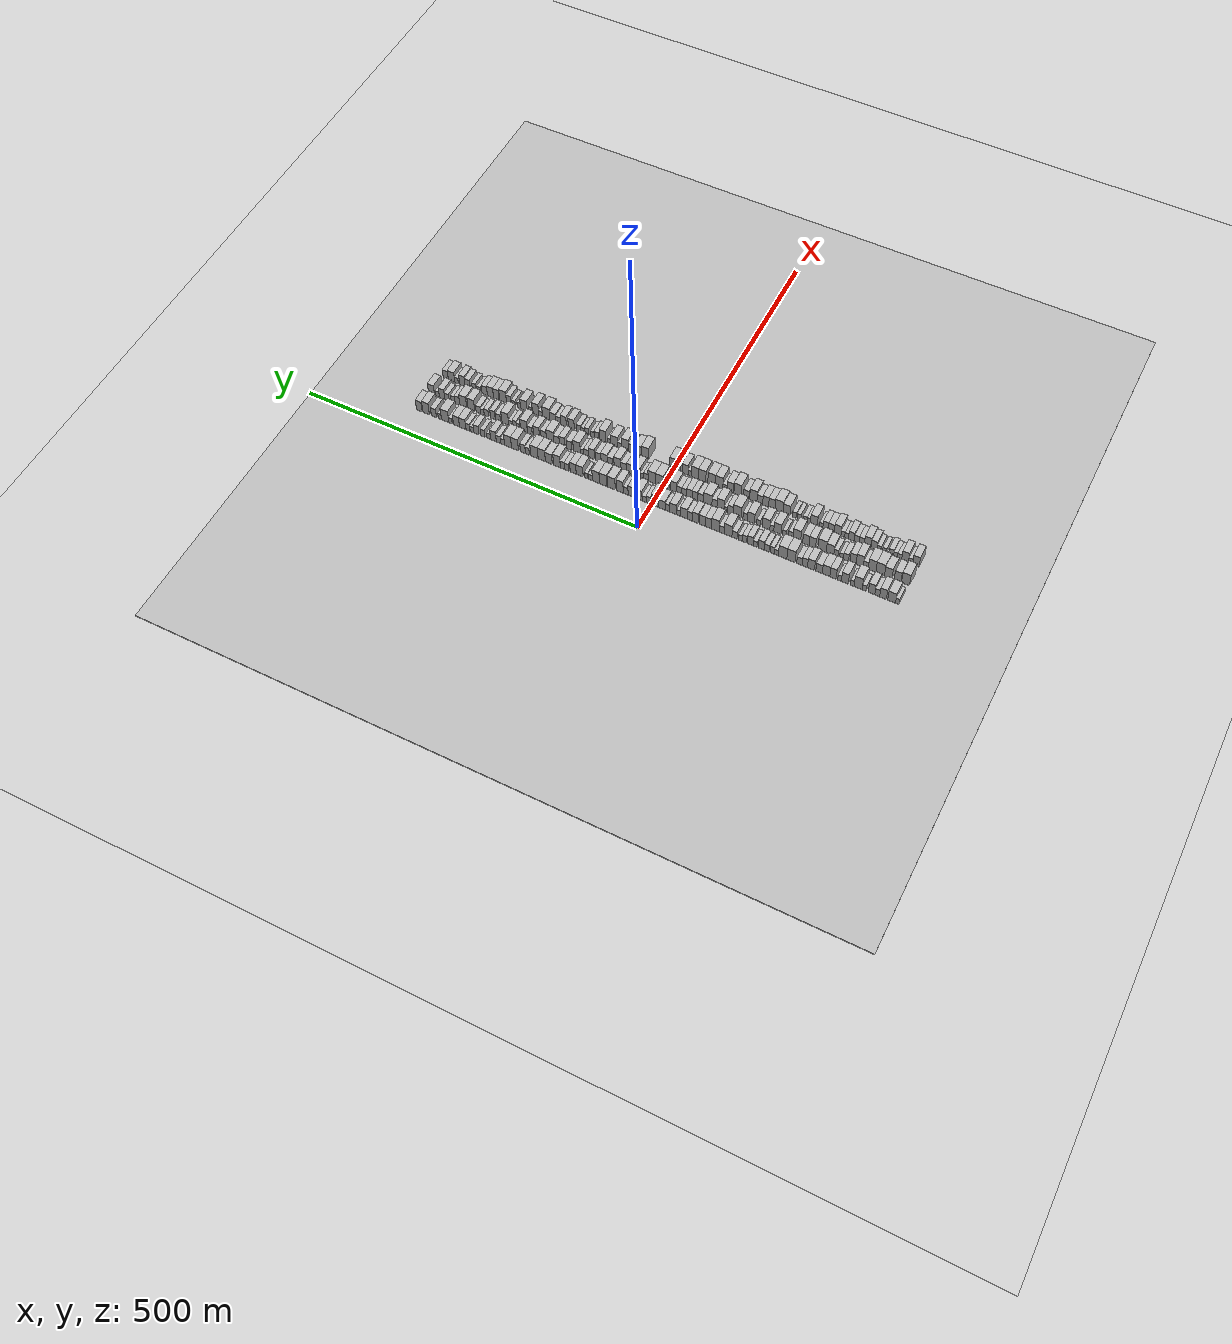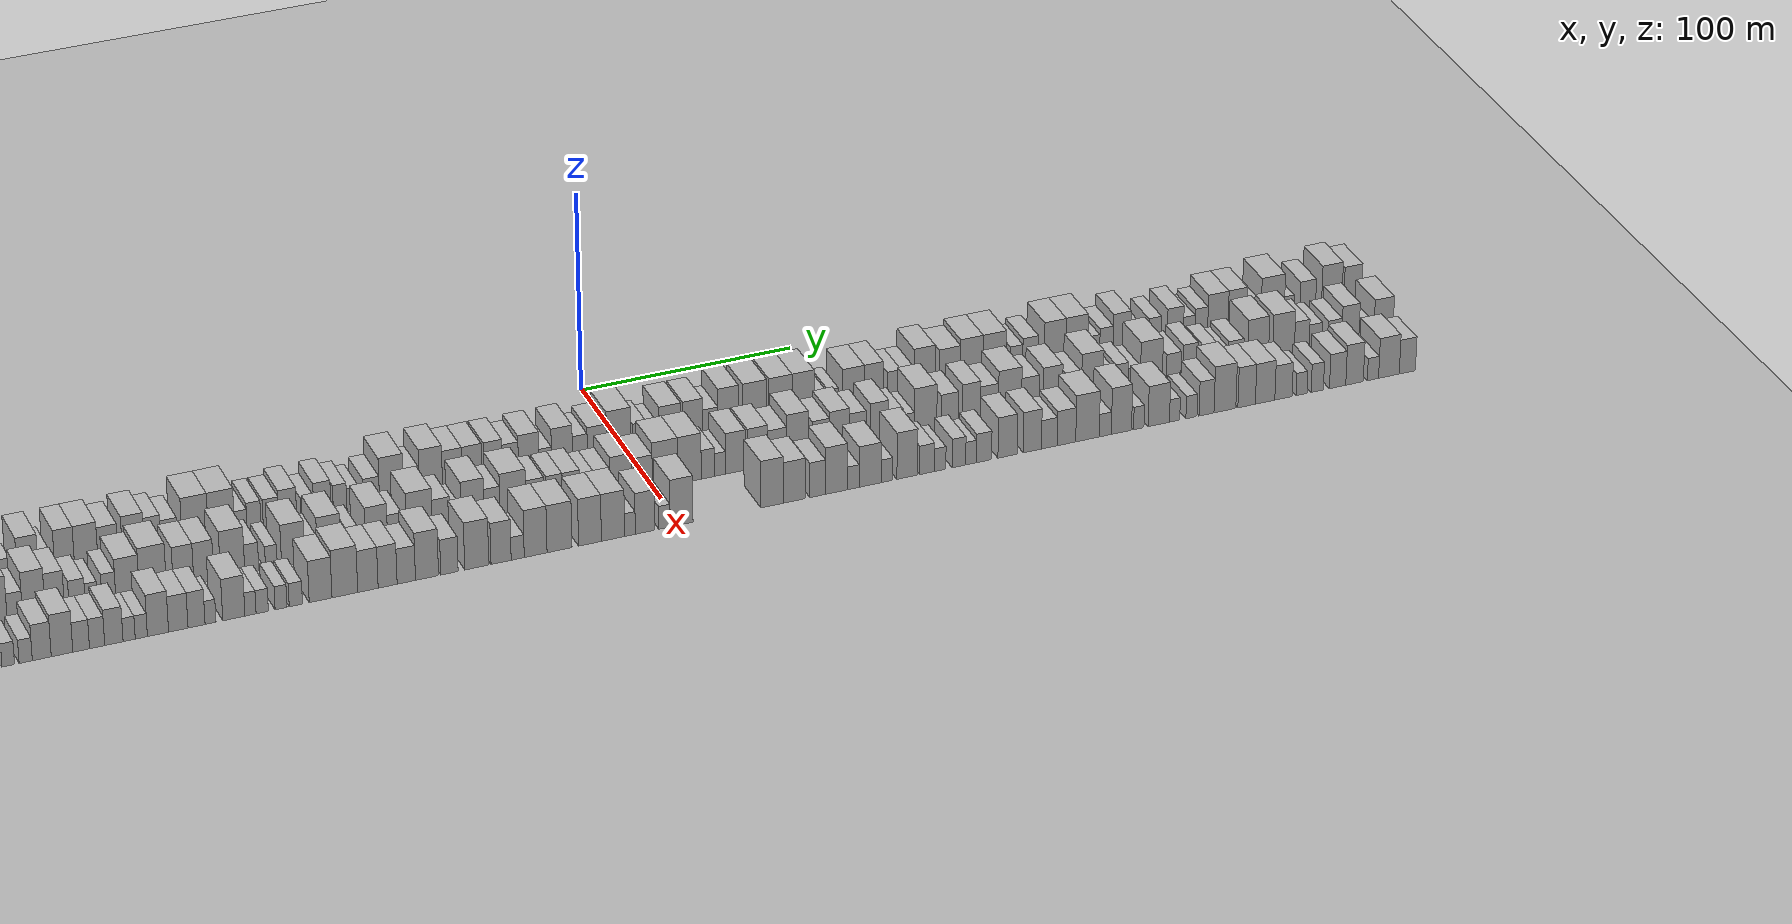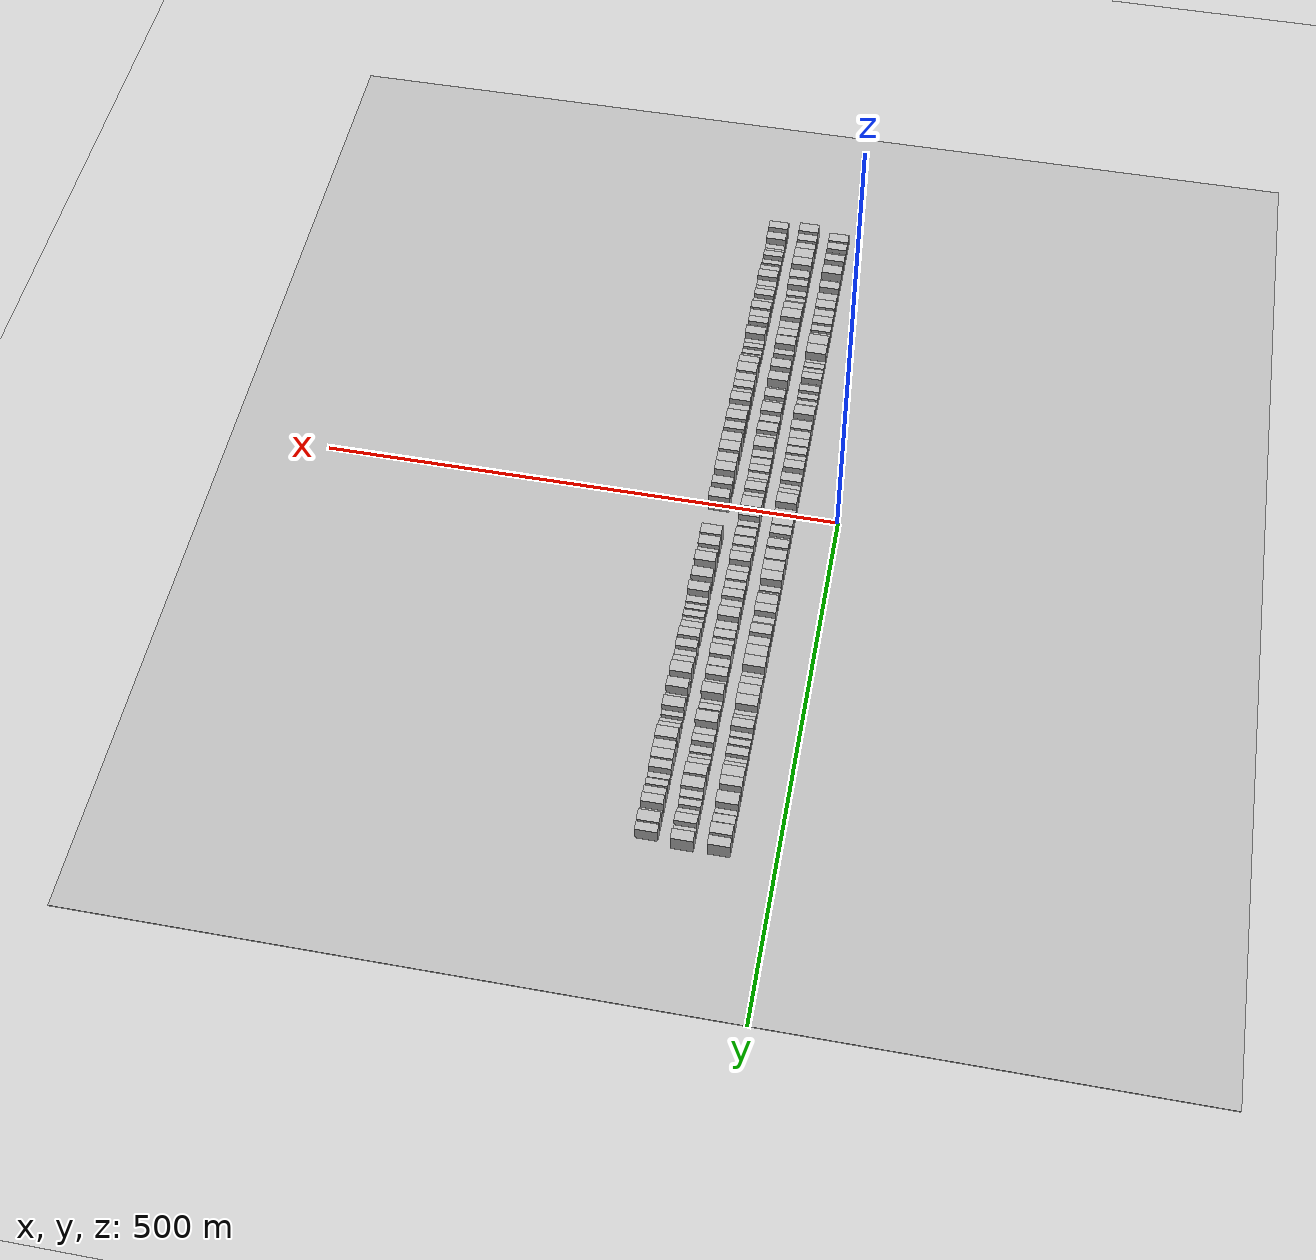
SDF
<?xml version="1.0" encoding="utf-8"?>

<sdf version="1.6">

   <world name="default">

      <gui fullscreen="0">

         <camera name="user_camera">

            <pose>-15 0 4.57585 0 0 0</pose>

            <view_controller>orbit</view_controller>

         </camera>

      </gui>

      <scene>

         <sky>

           <clouds>

             <speed>12</speed>

           </clouds>

         </sky>

         <ambient>0.4 0.4 0.4 1</ambient>

         <background>0.7 0.7 0.7 1</background>

         <shadows>1</shadows>

      </scene>

      <gravity>0 0 -9.8066</gravity>

      <magnetic_field>6e-06 2.3e-05 -4.2e-05</magnetic_field>

      <physics default="0" name="default_physics" type="ode">

         <ode>

            <solver>

               <type>quick</type>

               <iters>10</iters>

               <sor>1.0</sor>

               <use_dynamic_moi_rescaling>0</use_dynamic_moi_rescaling>

            </solver>

            <constraints>

               <cfm>0</cfm>

               <erp>0.2</erp>

               <contact_max_correcting_vel>100</contact_max_correcting_vel>

               <contact_surface_layer>0.001</contact_surface_layer>

            </constraints>

         </ode>

         <max_step_size>0.004</max_step_size>

         <real_time_factor>1</real_time_factor>

         <real_time_update_rate>250</real_time_update_rate>

      </physics>

      <light name="sun" type="directional">

         <cast_shadows>1</cast_shadows>

         <pose>0 0 10 0 0 0</pose>

         <diffuse>0.8 0.8 0.8 1</diffuse>

         <specular>0.2 0.2 0.2 1</specular>

         <attenuation>

            <range>1000</range>

            <constant>0.9</constant>

            <linear>0.01</linear>

            <quadratic>0.001</quadratic>

         </attenuation>

         <direction>-0.5 0.1 -0.9</direction>

      </light>

      <include>

         <name>ground_plane_1</name>

         <uri>model://HANNAS_ground_plane</uri>

         <pose>0 0 0  0 0 0</pose>

      </include>

      <include>

         <name>ground_plane_2</name>

         <uri>model://HANNAS_ground_plane</uri>

         <pose>100 0 0  0 0 0</pose>

      </include>

      <model name="building_1">

         <static>1</static>

         <pose frame="">50.0000 -344.5965 0 0.000000 0.000000 0.000000</pose>

         <link name="link">

            <pose frame="">0 0 6.00 0 0 0</pose>

            <collision name="collision">

               <geometry>

                  <box>

                     <size>20.0000 4.8070 12.0000</size>

                  </box>

               </geometry>

               <max_contacts>10</max_contacts>

               <surface>

                  <contact>

                     <ode/>

                  </contact>

                  <bounce/>

                  <friction>

                     <torsional>

                        <ode/>

                     </torsional>

                     <ode/>

                  </friction>

               </surface>

            </collision>

            <visual name="visual">

               <cast_shadows>0</cast_shadows>

               <geometry>

                  <box>

                     <size>20.0000 4.8070 12.0000</size>

                  </box>

               </geometry>

               <material>

                  <script>

                     <uri>model://HANNAS_wall/materials/scripts</uri>

                     <uri>model://HANNAS_wall/materials/textures</uri>

                     <name>vrc/HANNAS_wall</name>

                  </script>

               </material>

            </visual>

            <self_collide>0</self_collide>

            <enable_wind>0</enable_wind>

            <kinematic>0</kinematic>

         </link>

      </model>

      <model name="building_2">

         <static>1</static>

         <pose frame="">50.0000 -336.9802 0 0.000000 0.000000 0.000000</pose>

         <link name="link">

            <pose frame="">0 0 10.50 0 0 0</pose>

            <collision name="collision">

               <geometry>

                  <box>

                     <size>20.0000 10.4256 21.0000</size>

                  </box>

               </geometry>

               <max_contacts>10</max_contacts>

               <surface>

                  <contact>

                     <ode/>

                  </contact>

                  <bounce/>

                  <friction>

                     <torsional>

                        <ode/>

                     </torsional>

                     <ode/>

                  </friction>

               </surface>

            </collision>

            <visual name="visual">

               <cast_shadows>0</cast_shadows>

               <geometry>

                  <box>

                     <size>20.0000 10.4256 21.0000</size>

                  </box>

               </geometry>

               <material>

                  <script>

                     <uri>model://HANNAS_wall/materials/scripts</uri>

                     <uri>model://HANNAS_wall/materials/textures</uri>

                     <name>vrc/HANNAS_wall</name>

                  </script>

               </material>

            </visual>

            <self_collide>0</self_collide>

            <enable_wind>0</enable_wind>

            <kinematic>0</kinematic>

         </link>

      </model>

      <model name="building_3">

         <static>1</static>

         <pose frame="">50.0000 -325.2521 0 0.000000 0.000000 0.000000</pose>

         <link name="link">

            <pose frame="">0 0 10.50 0 0 0</pose>

            <collision name="collision">

               <geometry>

                  <box>

                     <size>20.0000 9.0307 21.0000</size>

                  </box>

               </geometry>

               <max_contacts>10</max_contacts>

               <surface>

                  <contact>

                     <ode/>

                  </contact>

                  <bounce/>

                  <friction>

                     <torsional>

                        <ode/>

                     </torsional>

                     <ode/>

                  </friction>

               </surface>

            </collision>

            <visual name="visual">

               <cast_shadows>0</cast_shadows>

               <geometry>

                  <box>

                     <size>20.0000 9.0307 21.0000</size>

                  </box>

               </geometry>

               <material>

                  <script>

                     <uri>model://HANNAS_wall/materials/scripts</uri>

                     <uri>model://HANNAS_wall/materials/textures</uri>

                     <name>vrc/HANNAS_wall</name>

                  </script>

               </material>

            </visual>

            <self_collide>0</self_collide>

            <enable_wind>0</enable_wind>

            <kinematic>0</kinematic>

         </link>

      </model>

      <model name="building_4">

         <static>1</static>

         <pose frame="">50.0000 -317.3914 0 0.000000 0.000000 0.000000</pose>

         <link name="link">

            <pose frame="">0 0 7.50 0 0 0</pose>

            <collision name="collision">

               <geometry>

                  <box>

                     <size>20.0000 6.6907 15.0000</size>

                  </box>

               </geometry>

               <max_contacts>10</max_contacts>

               <surface>

                  <contact>

                     <ode/>

                  </contact>

                  <bounce/>

                  <friction>

                     <torsional>

                        <ode/>

                     </torsional>

                     <ode/>

                  </friction>

               </surface>

            </collision>

            <visual name="visual">

               <cast_shadows>0</cast_shadows>

               <geometry>

                  <box>

                     <size>20.0000 6.6907 15.0000</size>

                  </box>

               </geometry>

               <material>

                  <script>

                     <uri>model://HANNAS_wall/materials/scripts</uri>

                     <uri>model://HANNAS_wall/materials/textures</uri>

                     <name>vrc/HANNAS_wall</name>

                  </script>

               </material>

            </visual>

            <self_collide>0</self_collide>

            <enable_wind>0</enable_wind>

            <kinematic>0</kinematic>

         </link>

      </model>

      <model name="building_5">

         <static>1</static>

         <pose frame="">50.0000 -309.6811 0 0.000000 0.000000 0.000000</pose>

         <link name="link">

            <pose frame="">0 0 10.50 0 0 0</pose>

            <collision name="collision">

               <geometry>

                  <box>

                     <size>20.0000 8.7298 21.0000</size>

                  </box>

               </geometry>

               <max_contacts>10</max_contacts>

               <surface>

                  <contact>

                     <ode/>

                  </contact>

                  <bounce/>

                  <friction>

                     <torsional>

                        <ode/>

                     </torsional>

                     <ode/>

                  </friction>

               </surface>

            </collision>

            <visual name="visual">

               <cast_shadows>0</cast_shadows>

               <geometry>

                  <box>

                     <size>20.0000 8.7298 21.0000</size>

                  </box>

               </geometry>

               <material>

                  <script>

                     <uri>model://HANNAS_wall/materials/scripts</uri>

                     <uri>model://HANNAS_wall/materials/textures</uri>

                     <name>vrc/HANNAS_wall</name>

                  </script>

               </material>

            </visual>

            <self_collide>0</self_collide>

            <enable_wind>0</enable_wind>

            <kinematic>0</kinematic>

         </link>

      </model>

      <model name="building_6">

         <static>1</static>

         <pose frame="">50.0000 -299.5352 0 0.000000 0.000000 0.000000</pose>

         <link name="link">

            <pose frame="">0 0 6.00 0 0 0</pose>

            <collision name="collision">

               <geometry>

                  <box>

                     <size>20.0000 5.5620 12.0000</size>

                  </box>

               </geometry>

               <max_contacts>10</max_contacts>

               <surface>

                  <contact>

                     <ode/>

                  </contact>

                  <bounce/>

                  <friction>

                     <torsional>

                        <ode/>

                     </torsional>

                     <ode/>

                  </friction>

               </surface>

            </collision>

            <visual name="visual">

               <cast_shadows>0</cast_shadows>

               <geometry>

                  <box>

                     <size>20.0000 5.5620 12.0000</size>

                  </box>

               </geometry>

               <material>

                  <script>

                     <uri>model://HANNAS_wall/materials/scripts</uri>

                     <uri>model://HANNAS_wall/materials/textures</uri>

                     <name>vrc/HANNAS_wall</name>

                  </script>

               </material>

            </visual>

            <self_collide>0</self_collide>

            <enable_wind>0</enable_wind>

            <kinematic>0</kinematic>

         </link>

      </model>

      <model name="building_7">

         <static>1</static>

         <pose frame="">50.0000 -291.2199 0 0.000000 0.000000 0.000000</pose>

         <link name="link">

            <pose frame="">0 0 12.00 0 0 0</pose>

            <collision name="collision">

               <geometry>

                  <box>

                     <size>20.0000 11.0687 24.0000</size>

                  </box>

               </geometry>

               <max_contacts>10</max_contacts>

               <surface>

                  <contact>

                     <ode/>

                  </contact>

                  <bounce/>

                  <friction>

                     <torsional>

                        <ode/>

                     </torsional>

                     <ode/>

                  </friction>

               </surface>

            </collision>

            <visual name="visual">

               <cast_shadows>0</cast_shadows>

               <geometry>

                  <box>

                     <size>20.0000 11.0687 24.0000</size>

                  </box>

               </geometry>

               <material>

                  <script>

                     <uri>model://HANNAS_wall/materials/scripts</uri>

                     <uri>model://HANNAS_wall/materials/textures</uri>

                     <name>vrc/HANNAS_wall</name>

                  </script>

               </material>

            </visual>

            <self_collide>0</self_collide>

            <enable_wind>0</enable_wind>

            <kinematic>0</kinematic>

         </link>

      </model>

      <model name="building_8">

         <static>1</static>

         <pose frame="">50.0000 -283.2138 0 0.000000 0.000000 0.000000</pose>

         <link name="link">

            <pose frame="">0 0 6.00 0 0 0</pose>

            <collision name="collision">

               <geometry>

                  <box>

                     <size>20.0000 4.9435 12.0000</size>

                  </box>

               </geometry>

               <max_contacts>10</max_contacts>

               <surface>

                  <contact>

                     <ode/>

                  </contact>

                  <bounce/>

                  <friction>

                     <torsional>

                        <ode/>

                     </torsional>

                     <ode/>

                  </friction>

               </surface>

            </collision>

            <visual name="visual">

               <cast_shadows>0</cast_shadows>

               <geometry>

                  <box>

                     <size>20.0000 4.9435 12.0000</size>

                  </box>

               </geometry>

               <material>

                  <script>

                     <uri>model://HANNAS_wall/materials/scripts</uri>

                     <uri>model://HANNAS_wall/materials/textures</uri>

                     <name>vrc/HANNAS_wall</name>

                  </script>

               </material>

            </visual>

            <self_collide>0</self_collide>

            <enable_wind>0</enable_wind>

            <kinematic>0</kinematic>

         </link>

      </model>

      <model name="building_9">

         <static>1</static>

         <pose frame="">50.0000 -273.0751 0 0.000000 0.000000 0.000000</pose>

         <link name="link">

            <pose frame="">0 0 10.50 0 0 0</pose>

            <collision name="collision">

               <geometry>

                  <box>

                     <size>20.0000 9.3339 21.0000</size>

                  </box>

               </geometry>

               <max_contacts>10</max_contacts>

               <surface>

                  <contact>

                     <ode/>

                  </contact>

                  <bounce/>

                  <friction>

                     <torsional>

                        <ode/>

                     </torsional>

                     <ode/>

                  </friction>

               </surface>

            </collision>

            <visual name="visual">

               <cast_shadows>0</cast_shadows>

               <geometry>

                  <box>

                     <size>20.0000 9.3339 21.0000</size>

                  </box>

               </geometry>

               <material>

                  <script>

                     <uri>model://HANNAS_wall/materials/scripts</uri>

                     <uri>model://HANNAS_wall/materials/textures</uri>

                     <name>vrc/HANNAS_wall</name>

                  </script>

               </material>

            </visual>

            <self_collide>0</self_collide>

            <enable_wind>0</enable_wind>

            <kinematic>0</kinematic>

         </link>

      </model>

      <model name="building_10">

         <static>1</static>

         <pose frame="">50.0000 -265.8114 0 0.000000 0.000000 0.000000</pose>

         <link name="link">

            <pose frame="">0 0 6.00 0 0 0</pose>

            <collision name="collision">

               <geometry>

                  <box>

                     <size>20.0000 5.1935 12.0000</size>

                  </box>

               </geometry>

               <max_contacts>10</max_contacts>

               <surface>

                  <contact>

                     <ode/>

                  </contact>

                  <bounce/>

                  <friction>

                     <torsional>

                        <ode/>

                     </torsional>

                     <ode/>

                  </friction>

               </surface>

            </collision>

            <visual name="visual">

               <cast_shadows>0</cast_shadows>

               <geometry>

                  <box>

                     <size>20.0000 5.1935 12.0000</size>

                  </box>

               </geometry>

               <material>

                  <script>

                     <uri>model://HANNAS_wall/materials/scripts</uri>

                     <uri>model://HANNAS_wall/materials/textures</uri>

                     <name>vrc/HANNAS_wall</name>

                  </script>

               </material>

            </visual>

            <self_collide>0</self_collide>

            <enable_wind>0</enable_wind>

            <kinematic>0</kinematic>

         </link>

      </model>

      <model name="building_11">

         <static>1</static>

         <pose frame="">50.0000 -256.8526 0 0.000000 0.000000 0.000000</pose>

         <link name="link">

            <pose frame="">0 0 10.50 0 0 0</pose>

            <collision name="collision">

               <geometry>

                  <box>

                     <size>20.0000 8.7240 21.0000</size>

                  </box>

               </geometry>

               <max_contacts>10</max_contacts>

               <surface>

                  <contact>

                     <ode/>

                  </contact>

                  <bounce/>

                  <friction>

                     <torsional>

                        <ode/>

                     </torsional>

                     <ode/>

                  </friction>

               </surface>

            </collision>

            <visual name="visual">

               <cast_shadows>0</cast_shadows>

               <geometry>

                  <box>

                     <size>20.0000 8.7240 21.0000</size>

                  </box>

               </geometry>

               <material>

                  <script>

                     <uri>model://HANNAS_wall/materials/scripts</uri>

                     <uri>model://HANNAS_wall/materials/textures</uri>

                     <name>vrc/HANNAS_wall</name>

                  </script>

               </material>

            </visual>

            <self_collide>0</self_collide>

            <enable_wind>0</enable_wind>

            <kinematic>0</kinematic>

         </link>

      </model>

      <model name="building_12">

         <static>1</static>

         <pose frame="">50.0000 -247.2860 0 0.000000 0.000000 0.000000</pose>

         <link name="link">

            <pose frame="">0 0 10.50 0 0 0</pose>

            <collision name="collision">

               <geometry>

                  <box>

                     <size>20.0000 10.4093 21.0000</size>

                  </box>

               </geometry>

               <max_contacts>10</max_contacts>

               <surface>

                  <contact>

                     <ode/>

                  </contact>

                  <bounce/>

                  <friction>

                     <torsional>

                        <ode/>

                     </torsional>

                     <ode/>

                  </friction>

               </surface>

            </collision>

            <visual name="visual">

               <cast_shadows>0</cast_shadows>

               <geometry>

                  <box>

                     <size>20.0000 10.4093 21.0000</size>

                  </box>

               </geometry>

               <material>

                  <script>

                     <uri>model://HANNAS_wall/materials/scripts</uri>

                     <uri>model://HANNAS_wall/materials/textures</uri>

                     <name>vrc/HANNAS_wall</name>

                  </script>

               </material>

            </visual>

            <self_collide>0</self_collide>

            <enable_wind>0</enable_wind>

            <kinematic>0</kinematic>

         </link>

      </model>

      <model name="building_13">

         <static>1</static>

         <pose frame="">50.0000 -237.5903 0 0.000000 0.000000 0.000000</pose>

         <link name="link">

            <pose frame="">0 0 9.00 0 0 0</pose>

            <collision name="collision">

               <geometry>

                  <box>

                     <size>20.0000 8.9820 18.0000</size>

                  </box>

               </geometry>

               <max_contacts>10</max_contacts>

               <surface>

                  <contact>

                     <ode/>

                  </contact>

                  <bounce/>

                  <friction>

                     <torsional>

                        <ode/>

                     </torsional>

                     <ode/>

                  </friction>

               </surface>

            </collision>

            <visual name="visual">

               <cast_shadows>0</cast_shadows>

               <geometry>

                  <box>

                     <size>20.0000 8.9820 18.0000</size>

                  </box>

               </geometry>

               <material>

                  <script>

                     <uri>model://HANNAS_wall/materials/scripts</uri>

                     <uri>model://HANNAS_wall/materials/textures</uri>

                     <name>vrc/HANNAS_wall</name>

                  </script>

               </material>

            </visual>

            <self_collide>0</self_collide>

            <enable_wind>0</enable_wind>

            <kinematic>0</kinematic>

         </link>

      </model>

      <model name="building_14">

         <static>1</static>

         <pose frame="">50.0000 -226.2633 0 0.000000 0.000000 0.000000</pose>

         <link name="link">

            <pose frame="">0 0 10.50 0 0 0</pose>

            <collision name="collision">

               <geometry>

                  <box>

                     <size>20.0000 9.6720 21.0000</size>

                  </box>

               </geometry>

               <max_contacts>10</max_contacts>

               <surface>

                  <contact>

                     <ode/>

                  </contact>

                  <bounce/>

                  <friction>

                     <torsional>

                        <ode/>

                     </torsional>

                     <ode/>

                  </friction>

               </surface>

            </collision>

            <visual name="visual">

               <cast_shadows>0</cast_shadows>

               <geometry>

                  <box>

                     <size>20.0000 9.6720 21.0000</size>

                  </box>

               </geometry>

               <material>

                  <script>

                     <uri>model://HANNAS_wall/materials/scripts</uri>

                     <uri>model://HANNAS_wall/materials/textures</uri>

                     <name>vrc/HANNAS_wall</name>

                  </script>

               </material>

            </visual>

            <self_collide>0</self_collide>

            <enable_wind>0</enable_wind>

            <kinematic>0</kinematic>

         </link>

      </model>

      <model name="building_15">

         <static>1</static>

         <pose frame="">50.0000 -217.6535 0 0.000000 0.000000 0.000000</pose>

         <link name="link">

            <pose frame="">0 0 9.00 0 0 0</pose>

            <collision name="collision">

               <geometry>

                  <box>

                     <size>20.0000 7.5478 18.0000</size>

                  </box>

               </geometry>

               <max_contacts>10</max_contacts>

               <surface>

                  <contact>

                     <ode/>

                  </contact>

                  <bounce/>

                  <friction>

                     <torsional>

                        <ode/>

                     </torsional>

                     <ode/>

                  </friction>

               </surface>

            </collision>

            <visual name="visual">

               <cast_shadows>0</cast_shadows>

               <geometry>

                  <box>

                     <size>20.0000 7.5478 18.0000</size>

                  </box>

               </geometry>

               <material>

                  <script>

                     <uri>model://HANNAS_wall/materials/scripts</uri>

                     <uri>model://HANNAS_wall/materials/textures</uri>

                     <name>vrc/HANNAS_wall</name>

                  </script>

               </material>

            </visual>

            <self_collide>0</self_collide>

            <enable_wind>0</enable_wind>

            <kinematic>0</kinematic>

         </link>

      </model>

      <model name="building_16">

         <static>1</static>

         <pose frame="">50.0000 -210.1589 0 0.000000 0.000000 0.000000</pose>

         <link name="link">

            <pose frame="">0 0 7.50 0 0 0</pose>

            <collision name="collision">

               <geometry>

                  <box>

                     <size>20.0000 7.4415 15.0000</size>

                  </box>

               </geometry>

               <max_contacts>10</max_contacts>

               <surface>

                  <contact>

                     <ode/>

                  </contact>

                  <bounce/>

                  <friction>

                     <torsional>

                        <ode/>

                     </torsional>

                     <ode/>

                  </friction>

               </surface>

            </collision>

            <visual name="visual">

               <cast_shadows>0</cast_shadows>

               <geometry>

                  <box>

                     <size>20.0000 7.4415 15.0000</size>

                  </box>

               </geometry>

               <material>

                  <script>

                     <uri>model://HANNAS_wall/materials/scripts</uri>

                     <uri>model://HANNAS_wall/materials/textures</uri>

                     <name>vrc/HANNAS_wall</name>

                  </script>

               </material>

            </visual>

            <self_collide>0</self_collide>

            <enable_wind>0</enable_wind>

            <kinematic>0</kinematic>

         </link>

      </model>

      <model name="building_17">

         <static>1</static>

         <pose frame="">50.0000 -198.5323 0 0.000000 0.000000 0.000000</pose>

         <link name="link">

            <pose frame="">0 0 12.00 0 0 0</pose>

            <collision name="collision">

               <geometry>

                  <box>

                     <size>20.0000 11.8116 24.0000</size>

                  </box>

               </geometry>

               <max_contacts>10</max_contacts>

               <surface>

                  <contact>

                     <ode/>

                  </contact>

                  <bounce/>

                  <friction>

                     <torsional>

                        <ode/>

                     </torsional>

                     <ode/>

                  </friction>

               </surface>

            </collision>

            <visual name="visual">

               <cast_shadows>0</cast_shadows>

               <geometry>

                  <box>

                     <size>20.0000 11.8116 24.0000</size>

                  </box>

               </geometry>

               <material>

                  <script>

                     <uri>model://HANNAS_wall/materials/scripts</uri>

                     <uri>model://HANNAS_wall/materials/textures</uri>

                     <name>vrc/HANNAS_wall</name>

                  </script>

               </material>

            </visual>

            <self_collide>0</self_collide>

            <enable_wind>0</enable_wind>

            <kinematic>0</kinematic>

         </link>

      </model>

      <model name="building_18">

         <static>1</static>

         <pose frame="">50.0000 -186.7275 0 0.000000 0.000000 0.000000</pose>

         <link name="link">

            <pose frame="">0 0 12.00 0 0 0</pose>

            <collision name="collision">

               <geometry>

                  <box>

                     <size>20.0000 11.7980 24.0000</size>

                  </box>

               </geometry>

               <max_contacts>10</max_contacts>

               <surface>

                  <contact>

                     <ode/>

                  </contact>

                  <bounce/>

                  <friction>

                     <torsional>

                        <ode/>

                     </torsional>

                     <ode/>

                  </friction>

               </surface>

            </collision>

            <visual name="visual">

               <cast_shadows>0</cast_shadows>

               <geometry>

                  <box>

                     <size>20.0000 11.7980 24.0000</size>

                  </box>

               </geometry>

               <material>

                  <script>

                     <uri>model://HANNAS_wall/materials/scripts</uri>

                     <uri>model://HANNAS_wall/materials/textures</uri>

                     <name>vrc/HANNAS_wall</name>

                  </script>

               </material>

            </visual>

            <self_collide>0</self_collide>

            <enable_wind>0</enable_wind>

            <kinematic>0</kinematic>

         </link>

      </model>

      <model name="building_19">

         <static>1</static>

         <pose frame="">50.0000 -178.0555 0 0.000000 0.000000 0.000000</pose>

         <link name="link">

            <pose frame="">0 0 6.00 0 0 0</pose>

            <collision name="collision">

               <geometry>

                  <box>

                     <size>20.0000 5.5461 12.0000</size>

                  </box>

               </geometry>

               <max_contacts>10</max_contacts>

               <surface>

                  <contact>

                     <ode/>

                  </contact>

                  <bounce/>

                  <friction>

                     <torsional>

                        <ode/>

                     </torsional>

                     <ode/>

                  </friction>

               </surface>

            </collision>

            <visual name="visual">

               <cast_shadows>0</cast_shadows>

               <geometry>

                  <box>

                     <size>20.0000 5.5461 12.0000</size>

                  </box>

               </geometry>

               <material>

                  <script>

                     <uri>model://HANNAS_wall/materials/scripts</uri>

                     <uri>model://HANNAS_wall/materials/textures</uri>

                     <name>vrc/HANNAS_wall</name>

                  </script>

               </material>

            </visual>

            <self_collide>0</self_collide>

            <enable_wind>0</enable_wind>

            <kinematic>0</kinematic>

         </link>

      </model>

      <model name="building_20">

         <static>1</static>

         <pose frame="">50.0000 -172.1351 0 0.000000 0.000000 0.000000</pose>

         <link name="link">

            <pose frame="">0 0 7.50 0 0 0</pose>

            <collision name="collision">

               <geometry>

                  <box>

                     <size>20.0000 6.2947 15.0000</size>

                  </box>

               </geometry>

               <max_contacts>10</max_contacts>

               <surface>

                  <contact>

                     <ode/>

                  </contact>

                  <bounce/>

                  <friction>

                     <torsional>

                        <ode/>

                     </torsional>

                     <ode/>

                  </friction>

               </surface>

            </collision>

            <visual name="visual">

               <cast_shadows>0</cast_shadows>

               <geometry>

                  <box>

                     <size>20.0000 6.2947 15.0000</size>

                  </box>

               </geometry>

               <material>

                  <script>

                     <uri>model://HANNAS_wall/materials/scripts</uri>

                     <uri>model://HANNAS_wall/materials/textures</uri>

                     <name>vrc/HANNAS_wall</name>

                  </script>

               </material>

            </visual>

            <self_collide>0</self_collide>

            <enable_wind>0</enable_wind>

            <kinematic>0</kinematic>

         </link>

      </model>

      <model name="building_21">

         <static>1</static>

         <pose frame="">50.0000 -164.4153 0 0.000000 0.000000 0.000000</pose>

         <link name="link">

            <pose frame="">0 0 7.50 0 0 0</pose>

            <collision name="collision">

               <geometry>

                  <box>

                     <size>20.0000 7.1448 15.0000</size>

                  </box>

               </geometry>

               <max_contacts>10</max_contacts>

               <surface>

                  <contact>

                     <ode/>

                  </contact>

                  <bounce/>

                  <friction>

                     <torsional>

                        <ode/>

                     </torsional>

                     <ode/>

                  </friction>

               </surface>

            </collision>

            <visual name="visual">

               <cast_shadows>0</cast_shadows>

               <geometry>

                  <box>

                     <size>20.0000 7.1448 15.0000</size>

                  </box>

               </geometry>

               <material>

                  <script>

                     <uri>model://HANNAS_wall/materials/scripts</uri>

                     <uri>model://HANNAS_wall/materials/textures</uri>

                     <name>vrc/HANNAS_wall</name>

                  </script>

               </material>

            </visual>

            <self_collide>0</self_collide>

            <enable_wind>0</enable_wind>

            <kinematic>0</kinematic>

         </link>

      </model>

      <model name="building_22">

         <static>1</static>

         <pose frame="">50.0000 -156.8310 0 0.000000 0.000000 0.000000</pose>

         <link name="link">

            <pose frame="">0 0 9.00 0 0 0</pose>

            <collision name="collision">

               <geometry>

                  <box>

                     <size>20.0000 8.0239 18.0000</size>

                  </box>

               </geometry>

               <max_contacts>10</max_contacts>

               <surface>

                  <contact>

                     <ode/>

                  </contact>

                  <bounce/>

                  <friction>

                     <torsional>

                        <ode/>

                     </torsional>

                     <ode/>

                  </friction>

               </surface>

            </collision>

            <visual name="visual">

               <cast_shadows>0</cast_shadows>

               <geometry>

                  <box>

                     <size>20.0000 8.0239 18.0000</size>

                  </box>

               </geometry>

               <material>

                  <script>

                     <uri>model://HANNAS_wall/materials/scripts</uri>

                     <uri>model://HANNAS_wall/materials/textures</uri>

                     <name>vrc/HANNAS_wall</name>

                  </script>

               </material>

            </visual>

            <self_collide>0</self_collide>

            <enable_wind>0</enable_wind>

            <kinematic>0</kinematic>

         </link>

      </model>

      <model name="building_23">

         <static>1</static>

         <pose frame="">50.0000 -147.9092 0 0.000000 0.000000 0.000000</pose>

         <link name="link">

            <pose frame="">0 0 6.00 0 0 0</pose>

            <collision name="collision">

               <geometry>

                  <box>

                     <size>20.0000 5.8197 12.0000</size>

                  </box>

               </geometry>

               <max_contacts>10</max_contacts>

               <surface>

                  <contact>

                     <ode/>

                  </contact>

                  <bounce/>

                  <friction>

                     <torsional>

                        <ode/>

                     </torsional>

                     <ode/>

                  </friction>

               </surface>

            </collision>

            <visual name="visual">

               <cast_shadows>0</cast_shadows>

               <geometry>

                  <box>

                     <size>20.0000 5.8197 12.0000</size>

                  </box>

               </geometry>

               <material>

                  <script>

                     <uri>model://HANNAS_wall/materials/scripts</uri>

                     <uri>model://HANNAS_wall/materials/textures</uri>

                     <name>vrc/HANNAS_wall</name>

                  </script>

               </material>

            </visual>

            <self_collide>0</self_collide>

            <enable_wind>0</enable_wind>

            <kinematic>0</kinematic>

         </link>

      </model>

      <model name="building_24">

         <static>1</static>

         <pose frame="">50.0000 -141.1100 0 0.000000 0.000000 0.000000</pose>

         <link name="link">

            <pose frame="">0 0 9.00 0 0 0</pose>

            <collision name="collision">

               <geometry>

                  <box>

                     <size>20.0000 7.7786 18.0000</size>

                  </box>

               </geometry>

               <max_contacts>10</max_contacts>

               <surface>

                  <contact>

                     <ode/>

                  </contact>

                  <bounce/>

                  <friction>

                     <torsional>

                        <ode/>

                     </torsional>

                     <ode/>

                  </friction>

               </surface>

            </collision>

            <visual name="visual">

               <cast_shadows>0</cast_shadows>

               <geometry>

                  <box>

                     <size>20.0000 7.7786 18.0000</size>

                  </box>

               </geometry>

               <material>

                  <script>

                     <uri>model://HANNAS_wall/materials/scripts</uri>

                     <uri>model://HANNAS_wall/materials/textures</uri>

                     <name>vrc/HANNAS_wall</name>

                  </script>

               </material>

            </visual>

            <self_collide>0</self_collide>

            <enable_wind>0</enable_wind>

            <kinematic>0</kinematic>

         </link>

      </model>

      <model name="building_25">

         <static>1</static>

         <pose frame="">50.0000 -133.1322 0 0.000000 0.000000 0.000000</pose>

         <link name="link">

            <pose frame="">0 0 7.50 0 0 0</pose>

            <collision name="collision">

               <geometry>

                  <box>

                     <size>20.0000 6.1768 15.0000</size>

                  </box>

               </geometry>

               <max_contacts>10</max_contacts>

               <surface>

                  <contact>

                     <ode/>

                  </contact>

                  <bounce/>

                  <friction>

                     <torsional>

                        <ode/>

                     </torsional>

                     <ode/>

                  </friction>

               </surface>

            </collision>

            <visual name="visual">

               <cast_shadows>0</cast_shadows>

               <geometry>

                  <box>

                     <size>20.0000 6.1768 15.0000</size>

                  </box>

               </geometry>

               <material>

                  <script>

                     <uri>model://HANNAS_wall/materials/scripts</uri>

                     <uri>model://HANNAS_wall/materials/textures</uri>

                     <name>vrc/HANNAS_wall</name>

                  </script>

               </material>

            </visual>

            <self_collide>0</self_collide>

            <enable_wind>0</enable_wind>

            <kinematic>0</kinematic>

         </link>

      </model>

      <model name="building_26">

         <static>1</static>

         <pose frame="">50.0000 -127.1928 0 0.000000 0.000000 0.000000</pose>

         <link name="link">

            <pose frame="">0 0 6.00 0 0 0</pose>

            <collision name="collision">

               <geometry>

                  <box>

                     <size>20.0000 5.7021 12.0000</size>

                  </box>

               </geometry>

               <max_contacts>10</max_contacts>

               <surface>

                  <contact>

                     <ode/>

                  </contact>

                  <bounce/>

                  <friction>

                     <torsional>

                        <ode/>

                     </torsional>

                     <ode/>

                  </friction>

               </surface>

            </collision>

            <visual name="visual">

               <cast_shadows>0</cast_shadows>

               <geometry>

                  <box>

                     <size>20.0000 5.7021 12.0000</size>

                  </box>

               </geometry>

               <material>

                  <script>

                     <uri>model://HANNAS_wall/materials/scripts</uri>

                     <uri>model://HANNAS_wall/materials/textures</uri>

                     <name>vrc/HANNAS_wall</name>

                  </script>

               </material>

            </visual>

            <self_collide>0</self_collide>

            <enable_wind>0</enable_wind>

            <kinematic>0</kinematic>

         </link>

      </model>

      <model name="building_27">

         <static>1</static>

         <pose frame="">50.0000 -118.7382 0 0.000000 0.000000 0.000000</pose>

         <link name="link">

            <pose frame="">0 0 7.50 0 0 0</pose>

            <collision name="collision">

               <geometry>

                  <box>

                     <size>20.0000 7.2071 15.0000</size>

                  </box>

               </geometry>

               <max_contacts>10</max_contacts>

               <surface>

                  <contact>

                     <ode/>

                  </contact>

                  <bounce/>

                  <friction>

                     <torsional>

                        <ode/>

                     </torsional>

                     <ode/>

                  </friction>

               </surface>

            </collision>

            <visual name="visual">

               <cast_shadows>0</cast_shadows>

               <geometry>

                  <box>

                     <size>20.0000 7.2071 15.0000</size>

                  </box>

               </geometry>

               <material>

                  <script>

                     <uri>model://HANNAS_wall/materials/scripts</uri>

                     <uri>model://HANNAS_wall/materials/textures</uri>

                     <name>vrc/HANNAS_wall</name>

                  </script>

               </material>

            </visual>

            <self_collide>0</self_collide>

            <enable_wind>0</enable_wind>

            <kinematic>0</kinematic>

         </link>

      </model>

      <model name="building_28">

         <static>1</static>

         <pose frame="">50.0000 -109.6479 0 0.000000 0.000000 0.000000</pose>

         <link name="link">

            <pose frame="">0 0 12.00 0 0 0</pose>

            <collision name="collision">

               <geometry>

                  <box>

                     <size>20.0000 10.9736 24.0000</size>

                  </box>

               </geometry>

               <max_contacts>10</max_contacts>

               <surface>

                  <contact>

                     <ode/>

                  </contact>

                  <bounce/>

                  <friction>

                     <torsional>

                        <ode/>

                     </torsional>

                     <ode/>

                  </friction>

               </surface>

            </collision>

            <visual name="visual">

               <cast_shadows>0</cast_shadows>

               <geometry>

                  <box>

                     <size>20.0000 10.9736 24.0000</size>

                  </box>

               </geometry>

               <material>

                  <script>

                     <uri>model://HANNAS_wall/materials/scripts</uri>

                     <uri>model://HANNAS_wall/materials/textures</uri>

                     <name>vrc/HANNAS_wall</name>

                  </script>

               </material>

            </visual>

            <self_collide>0</self_collide>

            <enable_wind>0</enable_wind>

            <kinematic>0</kinematic>

         </link>

      </model>

      <model name="building_29">

         <static>1</static>

         <pose frame="">50.0000 -100.4507 0 0.000000 0.000000 0.000000</pose>

         <link name="link">

            <pose frame="">0 0 7.50 0 0 0</pose>

            <collision name="collision">

               <geometry>

                  <box>

                     <size>20.0000 7.4209 15.0000</size>

                  </box>

               </geometry>

               <max_contacts>10</max_contacts>

               <surface>

                  <contact>

                     <ode/>

                  </contact>

                  <bounce/>

                  <friction>

                     <torsional>

                        <ode/>

                     </torsional>

                     <ode/>

                  </friction>

               </surface>

            </collision>

            <visual name="visual">

               <cast_shadows>0</cast_shadows>

               <geometry>

                  <box>

                     <size>20.0000 7.4209 15.0000</size>

                  </box>

               </geometry>

               <material>

                  <script>

                     <uri>model://HANNAS_wall/materials/scripts</uri>

                     <uri>model://HANNAS_wall/materials/textures</uri>

                     <name>vrc/HANNAS_wall</name>

                  </script>

               </material>

            </visual>

            <self_collide>0</self_collide>

            <enable_wind>0</enable_wind>

            <kinematic>0</kinematic>

         </link>

      </model>

      <model name="building_30">

         <static>1</static>

         <pose frame="">50.0000 -91.4822 0 0.000000 0.000000 0.000000</pose>

         <link name="link">

            <pose frame="">0 0 12.00 0 0 0</pose>

            <collision name="collision">

               <geometry>

                  <box>

                     <size>20.0000 10.5161 24.0000</size>

                  </box>

               </geometry>

               <max_contacts>10</max_contacts>

               <surface>

                  <contact>

                     <ode/>

                  </contact>

                  <bounce/>

                  <friction>

                     <torsional>

                        <ode/>

                     </torsional>

                     <ode/>

                  </friction>

               </surface>

            </collision>

            <visual name="visual">

               <cast_shadows>0</cast_shadows>

               <geometry>

                  <box>

                     <size>20.0000 10.5161 24.0000</size>

                  </box>

               </geometry>

               <material>

                  <script>

                     <uri>model://HANNAS_wall/materials/scripts</uri>

                     <uri>model://HANNAS_wall/materials/textures</uri>

                     <name>vrc/HANNAS_wall</name>

                  </script>

               </material>

            </visual>

            <self_collide>0</self_collide>

            <enable_wind>0</enable_wind>

            <kinematic>0</kinematic>

         </link>

      </model>

      <model name="building_31">

         <static>1</static>

         <pose frame="">50.0000 -81.6602 0 0.000000 0.000000 0.000000</pose>

         <link name="link">

            <pose frame="">0 0 10.50 0 0 0</pose>

            <collision name="collision">

               <geometry>

                  <box>

                     <size>20.0000 9.1278 21.0000</size>

                  </box>

               </geometry>

               <max_contacts>10</max_contacts>

               <surface>

                  <contact>

                     <ode/>

                  </contact>

                  <bounce/>

                  <friction>

                     <torsional>

                        <ode/>

                     </torsional>

                     <ode/>

                  </friction>

               </surface>

            </collision>

            <visual name="visual">

               <cast_shadows>0</cast_shadows>

               <geometry>

                  <box>

                     <size>20.0000 9.1278 21.0000</size>

                  </box>

               </geometry>

               <material>

                  <script>

                     <uri>model://HANNAS_wall/materials/scripts</uri>

                     <uri>model://HANNAS_wall/materials/textures</uri>

                     <name>vrc/HANNAS_wall</name>

                  </script>

               </material>

            </visual>

            <self_collide>0</self_collide>

            <enable_wind>0</enable_wind>

            <kinematic>0</kinematic>

         </link>

      </model>

      <model name="building_32">

         <static>1</static>

         <pose frame="">50.0000 -72.5824 0 0.000000 0.000000 0.000000</pose>

         <link name="link">

            <pose frame="">0 0 10.50 0 0 0</pose>

            <collision name="collision">

               <geometry>

                  <box>

                     <size>20.0000 9.0279 21.0000</size>

                  </box>

               </geometry>

               <max_contacts>10</max_contacts>

               <surface>

                  <contact>

                     <ode/>

                  </contact>

                  <bounce/>

                  <friction>

                     <torsional>

                        <ode/>

                     </torsional>

                     <ode/>

                  </friction>

               </surface>

            </collision>

            <visual name="visual">

               <cast_shadows>0</cast_shadows>

               <geometry>

                  <box>

                     <size>20.0000 9.0279 21.0000</size>

                  </box>

               </geometry>

               <material>

                  <script>

                     <uri>model://HANNAS_wall/materials/scripts</uri>

                     <uri>model://HANNAS_wall/materials/textures</uri>

                     <name>vrc/HANNAS_wall</name>

                  </script>

               </material>

            </visual>

            <self_collide>0</self_collide>

            <enable_wind>0</enable_wind>

            <kinematic>0</kinematic>

         </link>

      </model>

      <model name="building_33">

         <static>1</static>

         <pose frame="">50.0000 -62.8511 0 0.000000 0.000000 0.000000</pose>

         <link name="link">

            <pose frame="">0 0 10.50 0 0 0</pose>

            <collision name="collision">

               <geometry>

                  <box>

                     <size>20.0000 8.4345 21.0000</size>

                  </box>

               </geometry>

               <max_contacts>10</max_contacts>

               <surface>

                  <contact>

                     <ode/>

                  </contact>

                  <bounce/>

                  <friction>

                     <torsional>

                        <ode/>

                     </torsional>

                     <ode/>

                  </friction>

               </surface>

            </collision>

            <visual name="visual">

               <cast_shadows>0</cast_shadows>

               <geometry>

                  <box>

                     <size>20.0000 8.4345 21.0000</size>

                  </box>

               </geometry>

               <material>

                  <script>

                     <uri>model://HANNAS_wall/materials/scripts</uri>

                     <uri>model://HANNAS_wall/materials/textures</uri>

                     <name>vrc/HANNAS_wall</name>

                  </script>

               </material>

            </visual>

            <self_collide>0</self_collide>

            <enable_wind>0</enable_wind>

            <kinematic>0</kinematic>

         </link>

      </model>

      <model name="building_34">

         <static>1</static>

         <pose frame="">50.0000 -54.9011 0 0.000000 0.000000 0.000000</pose>

         <link name="link">

            <pose frame="">0 0 9.00 0 0 0</pose>

            <collision name="collision">

               <geometry>

                  <box>

                     <size>20.0000 7.4656 18.0000</size>

                  </box>

               </geometry>

               <max_contacts>10</max_contacts>

               <surface>

                  <contact>

                     <ode/>

                  </contact>

                  <bounce/>

                  <friction>

                     <torsional>

                        <ode/>

                     </torsional>

                     <ode/>

                  </friction>

               </surface>

            </collision>

            <visual name="visual">

               <cast_shadows>0</cast_shadows>

               <geometry>

                  <box>

                     <size>20.0000 7.4656 18.0000</size>

                  </box>

               </geometry>

               <material>

                  <script>

                     <uri>model://HANNAS_wall/materials/scripts</uri>

                     <uri>model://HANNAS_wall/materials/textures</uri>

                     <name>vrc/HANNAS_wall</name>

                  </script>

               </material>

            </visual>

            <self_collide>0</self_collide>

            <enable_wind>0</enable_wind>

            <kinematic>0</kinematic>

         </link>

      </model>

      <model name="building_35">

         <static>1</static>

         <pose frame="">50.0000 -46.3791 0 0.000000 0.000000 0.000000</pose>

         <link name="link">

            <pose frame="">0 0 10.50 0 0 0</pose>

            <collision name="collision">

               <geometry>

                  <box>

                     <size>20.0000 9.5783 21.0000</size>

                  </box>

               </geometry>

               <max_contacts>10</max_contacts>

               <surface>

                  <contact>

                     <ode/>

                  </contact>

                  <bounce/>

                  <friction>

                     <torsional>

                        <ode/>

                     </torsional>

                     <ode/>

                  </friction>

               </surface>

            </collision>

            <visual name="visual">

               <cast_shadows>0</cast_shadows>

               <geometry>

                  <box>

                     <size>20.0000 9.5783 21.0000</size>

                  </box>

               </geometry>

               <material>

                  <script>

                     <uri>model://HANNAS_wall/materials/scripts</uri>

                     <uri>model://HANNAS_wall/materials/textures</uri>

                     <name>vrc/HANNAS_wall</name>

                  </script>

               </material>

            </visual>

            <self_collide>0</self_collide>

            <enable_wind>0</enable_wind>

            <kinematic>0</kinematic>

         </link>

      </model>

      <model name="building_36">

         <static>1</static>

         <pose frame="">50.0000 -38.7108 0 0.000000 0.000000 0.000000</pose>

         <link name="link">

            <pose frame="">0 0 6.00 0 0 0</pose>

            <collision name="collision">

               <geometry>

                  <box>

                     <size>20.0000 5.7583 12.0000</size>

                  </box>

               </geometry>

               <max_contacts>10</max_contacts>

               <surface>

                  <contact>

                     <ode/>

                  </contact>

                  <bounce/>

                  <friction>

                     <torsional>

                        <ode/>

                     </torsional>

                     <ode/>

                  </friction>

               </surface>

            </collision>

            <visual name="visual">

               <cast_shadows>0</cast_shadows>

               <geometry>

                  <box>

                     <size>20.0000 5.7583 12.0000</size>

                  </box>

               </geometry>

               <material>

                  <script>

                     <uri>model://HANNAS_wall/materials/scripts</uri>

                     <uri>model://HANNAS_wall/materials/textures</uri>

                     <name>vrc/HANNAS_wall</name>

                  </script>

               </material>

            </visual>

            <self_collide>0</self_collide>

            <enable_wind>0</enable_wind>

            <kinematic>0</kinematic>

         </link>

      </model>

      <model name="building_37">

         <static>1</static>

         <pose frame="">50.0000 -30.9705 0 0.000000 0.000000 0.000000</pose>

         <link name="link">

            <pose frame="">0 0 10.50 0 0 0</pose>

            <collision name="collision">

               <geometry>

                  <box>

                     <size>20.0000 9.7223 21.0000</size>

                  </box>

               </geometry>

               <max_contacts>10</max_contacts>

               <surface>

                  <contact>

                     <ode/>

                  </contact>

                  <bounce/>

                  <friction>

                     <torsional>

                        <ode/>

                     </torsional>

                     <ode/>

                  </friction>

               </surface>

            </collision>

            <visual name="visual">

               <cast_shadows>0</cast_shadows>

               <geometry>

                  <box>

                     <size>20.0000 9.7223 21.0000</size>

                  </box>

               </geometry>

               <material>

                  <script>

                     <uri>model://HANNAS_wall/materials/scripts</uri>

                     <uri>model://HANNAS_wall/materials/textures</uri>

                     <name>vrc/HANNAS_wall</name>

                  </script>

               </material>

            </visual>

            <self_collide>0</self_collide>

            <enable_wind>0</enable_wind>

            <kinematic>0</kinematic>

         </link>

      </model>

      <model name="building_38">

         <static>1</static>

         <pose frame="">50.0000 -22.6465 0 0.000000 0.000000 0.000000</pose>

         <link name="link">

            <pose frame="">0 0 7.50 0 0 0</pose>

            <collision name="collision">

               <geometry>

                  <box>

                     <size>20.0000 6.9256 15.0000</size>

                  </box>

               </geometry>

               <max_contacts>10</max_contacts>

               <surface>

                  <contact>

                     <ode/>

                  </contact>

                  <bounce/>

                  <friction>

                     <torsional>

                        <ode/>

                     </torsional>

                     <ode/>

                  </friction>

               </surface>

            </collision>

            <visual name="visual">

               <cast_shadows>0</cast_shadows>

               <geometry>

                  <box>

                     <size>20.0000 6.9256 15.0000</size>

                  </box>

               </geometry>

               <material>

                  <script>

                     <uri>model://HANNAS_wall/materials/scripts</uri>

                     <uri>model://HANNAS_wall/materials/textures</uri>

                     <name>vrc/HANNAS_wall</name>

                  </script>

               </material>

            </visual>

            <self_collide>0</self_collide>

            <enable_wind>0</enable_wind>

            <kinematic>0</kinematic>

         </link>

      </model>

      <model name="building_39">

         <static>1</static>

         <pose frame="">50.0000 -14.6906 0 0.000000 0.000000 0.000000</pose>

         <link name="link">

            <pose frame="">0 0 9.00 0 0 0</pose>

            <collision name="collision">

               <geometry>

                  <box>

                     <size>20.0000 8.9863 18.0000</size>

                  </box>

               </geometry>

               <max_contacts>10</max_contacts>

               <surface>

                  <contact>

                     <ode/>

                  </contact>

                  <bounce/>

                  <friction>

                     <torsional>

                        <ode/>

                     </torsional>

                     <ode/>

                  </friction>

               </surface>

            </collision>

            <visual name="visual">

               <cast_shadows>0</cast_shadows>

               <geometry>

                  <box>

                     <size>20.0000 8.9863 18.0000</size>

                  </box>

               </geometry>

               <material>

                  <script>

                     <uri>model://HANNAS_wall/materials/scripts</uri>

                     <uri>model://HANNAS_wall/materials/textures</uri>

                     <name>vrc/HANNAS_wall</name>

                  </script>

               </material>

            </visual>

            <self_collide>0</self_collide>

            <enable_wind>0</enable_wind>

            <kinematic>0</kinematic>

         </link>

      </model>

      <model name="building_40">

         <static>1</static>

         <pose frame="">50.0000 -4.5184 0 0.000000 0.000000 0.000000</pose>

         <link name="link">

            <pose frame="">0 0 12.00 0 0 0</pose>

            <collision name="collision">

               <geometry>

                  <box>

                     <size>20.0000 11.3580 24.0000</size>

                  </box>

               </geometry>

               <max_contacts>10</max_contacts>

               <surface>

                  <contact>

                     <ode/>

                  </contact>

                  <bounce/>

                  <friction>

                     <torsional>

                        <ode/>

                     </torsional>

                     <ode/>

                  </friction>

               </surface>

            </collision>

            <visual name="visual">

               <cast_shadows>0</cast_shadows>

               <geometry>

                  <box>

                     <size>20.0000 11.3580 24.0000</size>

                  </box>

               </geometry>

               <material>

                  <script>

                     <uri>model://HANNAS_wall/materials/scripts</uri>

                     <uri>model://HANNAS_wall/materials/textures</uri>

                     <name>vrc/HANNAS_wall</name>

                  </script>

               </material>

            </visual>

            <self_collide>0</self_collide>

            <enable_wind>0</enable_wind>

            <kinematic>0</kinematic>

         </link>

      </model>

      <model name="building_41">

         <static>1</static>

         <pose frame="">50.0000 5.3556 0 0.000000 0.000000 0.000000</pose>

         <link name="link">

            <pose frame="">0 0 7.50 0 0 0</pose>

            <collision name="collision">

               <geometry>

                  <box>

                     <size>20.0000 6.3901 15.0000</size>

                  </box>

               </geometry>

               <max_contacts>10</max_contacts>

               <surface>

                  <contact>

                     <ode/>

                  </contact>

                  <bounce/>

                  <friction>

                     <torsional>

                        <ode/>

                     </torsional>

                     <ode/>

                  </friction>

               </surface>

            </collision>

            <visual name="visual">

               <cast_shadows>0</cast_shadows>

               <geometry>

                  <box>

                     <size>20.0000 6.3901 15.0000</size>

                  </box>

               </geometry>

               <material>

                  <script>

                     <uri>model://HANNAS_wall/materials/scripts</uri>

                     <uri>model://HANNAS_wall/materials/textures</uri>

                     <name>vrc/HANNAS_wall</name>

                  </script>

               </material>

            </visual>

            <self_collide>0</self_collide>

            <enable_wind>0</enable_wind>

            <kinematic>0</kinematic>

         </link>

      </model>

      <model name="building_42">

         <static>1</static>

         <pose frame="">50.0000 11.5126 0 0.000000 0.000000 0.000000</pose>

         <link name="link">

            <pose frame="">0 0 6.00 0 0 0</pose>

            <collision name="collision">

               <geometry>

                  <box>

                     <size>20.0000 5.9239 12.0000</size>

                  </box>

               </geometry>

               <max_contacts>10</max_contacts>

               <surface>

                  <contact>

                     <ode/>

                  </contact>

                  <bounce/>

                  <friction>

                     <torsional>

                        <ode/>

                     </torsional>

                     <ode/>

                  </friction>

               </surface>

            </collision>

            <visual name="visual">

               <cast_shadows>0</cast_shadows>

               <geometry>

                  <box>

                     <size>20.0000 5.9239 12.0000</size>

                  </box>

               </geometry>

               <material>

                  <script>

                     <uri>model://HANNAS_wall/materials/scripts</uri>

                     <uri>model://HANNAS_wall/materials/textures</uri>

                     <name>vrc/HANNAS_wall</name>

                  </script>

               </material>

            </visual>

            <self_collide>0</self_collide>

            <enable_wind>0</enable_wind>

            <kinematic>0</kinematic>

         </link>

      </model>

      <model name="building_43">

         <static>1</static>

         <pose frame="">50.0000 19.5705 0 0.000000 0.000000 0.000000</pose>

         <link name="link">

            <pose frame="">0 0 10.50 0 0 0</pose>

            <collision name="collision">

               <geometry>

                  <box>

                     <size>20.0000 10.1919 21.0000</size>

                  </box>

               </geometry>

               <max_contacts>10</max_contacts>

               <surface>

                  <contact>

                     <ode/>

                  </contact>

                  <bounce/>

                  <friction>

                     <torsional>

                        <ode/>

                     </torsional>

                     <ode/>

                  </friction>

               </surface>

            </collision>

            <visual name="visual">

               <cast_shadows>0</cast_shadows>

               <geometry>

                  <box>

                     <size>20.0000 10.1919 21.0000</size>

                  </box>

               </geometry>

               <material>

                  <script>

                     <uri>model://HANNAS_wall/materials/scripts</uri>

                     <uri>model://HANNAS_wall/materials/textures</uri>

                     <name>vrc/HANNAS_wall</name>

                  </script>

               </material>

            </visual>

            <self_collide>0</self_collide>

            <enable_wind>0</enable_wind>

            <kinematic>0</kinematic>

         </link>

      </model>

      <model name="building_44">

         <static>1</static>

         <pose frame="">50.0000 30.2833 0 0.000000 0.000000 0.000000</pose>

         <link name="link">

            <pose frame="">0 0 10.50 0 0 0</pose>

            <collision name="collision">

               <geometry>

                  <box>

                     <size>20.0000 9.2336 21.0000</size>

                  </box>

               </geometry>

               <max_contacts>10</max_contacts>

               <surface>

                  <contact>

                     <ode/>

                  </contact>

                  <bounce/>

                  <friction>

                     <torsional>

                        <ode/>

                     </torsional>

                     <ode/>

                  </friction>

               </surface>

            </collision>

            <visual name="visual">

               <cast_shadows>0</cast_shadows>

               <geometry>

                  <box>

                     <size>20.0000 9.2336 21.0000</size>

                  </box>

               </geometry>

               <material>

                  <script>

                     <uri>model://HANNAS_wall/materials/scripts</uri>

                     <uri>model://HANNAS_wall/materials/textures</uri>

                     <name>vrc/HANNAS_wall</name>

                  </script>

               </material>

            </visual>

            <self_collide>0</self_collide>

            <enable_wind>0</enable_wind>

            <kinematic>0</kinematic>

         </link>

      </model>

      <model name="building_45">

         <static>1</static>

         <pose frame="">50.0000 38.5328 0 0.000000 0.000000 0.000000</pose>

         <link name="link">

            <pose frame="">0 0 7.50 0 0 0</pose>

            <collision name="collision">

               <geometry>

                  <box>

                     <size>20.0000 7.2654 15.0000</size>

                  </box>

               </geometry>

               <max_contacts>10</max_contacts>

               <surface>

                  <contact>

                     <ode/>

                  </contact>

                  <bounce/>

                  <friction>

                     <torsional>

                        <ode/>

                     </torsional>

                     <ode/>

                  </friction>

               </surface>

            </collision>

            <visual name="visual">

               <cast_shadows>0</cast_shadows>

               <geometry>

                  <box>

                     <size>20.0000 7.2654 15.0000</size>

                  </box>

               </geometry>

               <material>

                  <script>

                     <uri>model://HANNAS_wall/materials/scripts</uri>

                     <uri>model://HANNAS_wall/materials/textures</uri>

                     <name>vrc/HANNAS_wall</name>

                  </script>

               </material>

            </visual>

            <self_collide>0</self_collide>

            <enable_wind>0</enable_wind>

            <kinematic>0</kinematic>

         </link>

      </model>

      <model name="building_46">

         <static>1</static>

         <pose frame="">50.0000 47.0347 0 0.000000 0.000000 0.000000</pose>

         <link name="link">

            <pose frame="">0 0 12.00 0 0 0</pose>

            <collision name="collision">

               <geometry>

                  <box>

                     <size>20.0000 9.7384 24.0000</size>

                  </box>

               </geometry>

               <max_contacts>10</max_contacts>

               <surface>

                  <contact>

                     <ode/>

                  </contact>

                  <bounce/>

                  <friction>

                     <torsional>

                        <ode/>

                     </torsional>

                     <ode/>

                  </friction>

               </surface>

            </collision>

            <visual name="visual">

               <cast_shadows>0</cast_shadows>

               <geometry>

                  <box>

                     <size>20.0000 9.7384 24.0000</size>

                  </box>

               </geometry>

               <material>

                  <script>

                     <uri>model://HANNAS_wall/materials/scripts</uri>

                     <uri>model://HANNAS_wall/materials/textures</uri>

                     <name>vrc/HANNAS_wall</name>

                  </script>

               </material>

            </visual>

            <self_collide>0</self_collide>

            <enable_wind>0</enable_wind>

            <kinematic>0</kinematic>

         </link>

      </model>

      <model name="building_47">

         <static>1</static>

         <pose frame="">50.0000 59.5788 0 0.000000 0.000000 0.000000</pose>

         <link name="link">

            <pose frame="">0 0 12.00 0 0 0</pose>

            <collision name="collision">

               <geometry>

                  <box>

                     <size>20.0000 11.3498 24.0000</size>

                  </box>

               </geometry>

               <max_contacts>10</max_contacts>

               <surface>

                  <contact>

                     <ode/>

                  </contact>

                  <bounce/>

                  <friction>

                     <torsional>

                        <ode/>

                     </torsional>

                     <ode/>

                  </friction>

               </surface>

            </collision>

            <visual name="visual">

               <cast_shadows>0</cast_shadows>

               <geometry>

                  <box>

                     <size>20.0000 11.3498 24.0000</size>

                  </box>

               </geometry>

               <material>

                  <script>

                     <uri>model://HANNAS_wall/materials/scripts</uri>

                     <uri>model://HANNAS_wall/materials/textures</uri>

                     <name>vrc/HANNAS_wall</name>

                  </script>

               </material>

            </visual>

            <self_collide>0</self_collide>

            <enable_wind>0</enable_wind>

            <kinematic>0</kinematic>

         </link>

      </model>

      <model name="building_48">

         <static>1</static>

         <pose frame="">50.0000 71.7756 0 0.000000 0.000000 0.000000</pose>

         <link name="link">

            <pose frame="">0 0 12.00 0 0 0</pose>

            <collision name="collision">

               <geometry>

                  <box>

                     <size>20.0000 11.0438 24.0000</size>

                  </box>

               </geometry>

               <max_contacts>10</max_contacts>

               <surface>

                  <contact>

                     <ode/>

                  </contact>

                  <bounce/>

                  <friction>

                     <torsional>

                        <ode/>

                     </torsional>

                     <ode/>

                  </friction>

               </surface>

            </collision>

            <visual name="visual">

               <cast_shadows>0</cast_shadows>

               <geometry>

                  <box>

                     <size>20.0000 11.0438 24.0000</size>

                  </box>

               </geometry>

               <material>

                  <script>

                     <uri>model://HANNAS_wall/materials/scripts</uri>

                     <uri>model://HANNAS_wall/materials/textures</uri>

                     <name>vrc/HANNAS_wall</name>

                  </script>

               </material>

            </visual>

            <self_collide>0</self_collide>

            <enable_wind>0</enable_wind>

            <kinematic>0</kinematic>

         </link>

      </model>

      <model name="building_49">

         <static>1</static>

         <pose frame="">50.0000 82.5181 0 0.000000 0.000000 0.000000</pose>

         <link name="link">

            <pose frame="">0 0 12.00 0 0 0</pose>

            <collision name="collision">

               <geometry>

                  <box>

                     <size>20.0000 10.4412 24.0000</size>

                  </box>

               </geometry>

               <max_contacts>10</max_contacts>

               <surface>

                  <contact>

                     <ode/>

                  </contact>

                  <bounce/>

                  <friction>

                     <torsional>

                        <ode/>

                     </torsional>

                     <ode/>

                  </friction>

               </surface>

            </collision>

            <visual name="visual">

               <cast_shadows>0</cast_shadows>

               <geometry>

                  <box>

                     <size>20.0000 10.4412 24.0000</size>

                  </box>

               </geometry>

               <material>

                  <script>

                     <uri>model://HANNAS_wall/materials/scripts</uri>

                     <uri>model://HANNAS_wall/materials/textures</uri>

                     <name>vrc/HANNAS_wall</name>

                  </script>

               </material>

            </visual>

            <self_collide>0</self_collide>

            <enable_wind>0</enable_wind>

            <kinematic>0</kinematic>

         </link>

      </model>

      <model name="building_50">

         <static>1</static>

         <pose frame="">50.0000 90.5977 0 0.000000 0.000000 0.000000</pose>

         <link name="link">

            <pose frame="">0 0 6.00 0 0 0</pose>

            <collision name="collision">

               <geometry>

                  <box>

                     <size>20.0000 5.7179 12.0000</size>

                  </box>

               </geometry>

               <max_contacts>10</max_contacts>

               <surface>

                  <contact>

                     <ode/>

                  </contact>

                  <bounce/>

                  <friction>

                     <torsional>

                        <ode/>

                     </torsional>

                     <ode/>

                  </friction>

               </surface>

            </collision>

            <visual name="visual">

               <cast_shadows>0</cast_shadows>

               <geometry>

                  <box>

                     <size>20.0000 5.7179 12.0000</size>

                  </box>

               </geometry>

               <material>

                  <script>

                     <uri>model://HANNAS_wall/materials/scripts</uri>

                     <uri>model://HANNAS_wall/materials/textures</uri>

                     <name>vrc/HANNAS_wall</name>

                  </script>

               </material>

            </visual>

            <self_collide>0</self_collide>

            <enable_wind>0</enable_wind>

            <kinematic>0</kinematic>

         </link>

      </model>

      <model name="building_51">

         <static>1</static>

         <pose frame="">50.0000 96.9436 0 0.000000 0.000000 0.000000</pose>

         <link name="link">

            <pose frame="">0 0 6.00 0 0 0</pose>

            <collision name="collision">

               <geometry>

                  <box>

                     <size>20.0000 4.9740 12.0000</size>

                  </box>

               </geometry>

               <max_contacts>10</max_contacts>

               <surface>

                  <contact>

                     <ode/>

                  </contact>

                  <bounce/>

                  <friction>

                     <torsional>

                        <ode/>

                     </torsional>

                     <ode/>

                  </friction>

               </surface>

            </collision>

            <visual name="visual">

               <cast_shadows>0</cast_shadows>

               <geometry>

                  <box>

                     <size>20.0000 4.9740 12.0000</size>

                  </box>

               </geometry>

               <material>

                  <script>

                     <uri>model://HANNAS_wall/materials/scripts</uri>

                     <uri>model://HANNAS_wall/materials/textures</uri>

                     <name>vrc/HANNAS_wall</name>

                  </script>

               </material>

            </visual>

            <self_collide>0</self_collide>

            <enable_wind>0</enable_wind>

            <kinematic>0</kinematic>

         </link>

      </model>

      <model name="building_52">

         <static>1</static>

         <pose frame="">50.0000 106.6325 0 0.000000 0.000000 0.000000</pose>

         <link name="link">

            <pose frame="">0 0 10.50 0 0 0</pose>

            <collision name="collision">

               <geometry>

                  <box>

                     <size>20.0000 10.4038 21.0000</size>

                  </box>

               </geometry>

               <max_contacts>10</max_contacts>

               <surface>

                  <contact>

                     <ode/>

                  </contact>

                  <bounce/>

                  <friction>

                     <torsional>

                        <ode/>

                     </torsional>

                     <ode/>

                  </friction>

               </surface>

            </collision>

            <visual name="visual">

               <cast_shadows>0</cast_shadows>

               <geometry>

                  <box>

                     <size>20.0000 10.4038 21.0000</size>

                  </box>

               </geometry>

               <material>

                  <script>

                     <uri>model://HANNAS_wall/materials/scripts</uri>

                     <uri>model://HANNAS_wall/materials/textures</uri>

                     <name>vrc/HANNAS_wall</name>

                  </script>

               </material>

            </visual>

            <self_collide>0</self_collide>

            <enable_wind>0</enable_wind>

            <kinematic>0</kinematic>

         </link>

      </model>

      <model name="building_53">

         <static>1</static>

         <pose frame="">50.0000 116.3029 0 0.000000 0.000000 0.000000</pose>

         <link name="link">

            <pose frame="">0 0 10.50 0 0 0</pose>

            <collision name="collision">

               <geometry>

                  <box>

                     <size>20.0000 8.9370 21.0000</size>

                  </box>

               </geometry>

               <max_contacts>10</max_contacts>

               <surface>

                  <contact>

                     <ode/>

                  </contact>

                  <bounce/>

                  <friction>

                     <torsional>

                        <ode/>

                     </torsional>

                     <ode/>

                  </friction>

               </surface>

            </collision>

            <visual name="visual">

               <cast_shadows>0</cast_shadows>

               <geometry>

                  <box>

                     <size>20.0000 8.9370 21.0000</size>

                  </box>

               </geometry>

               <material>

                  <script>

                     <uri>model://HANNAS_wall/materials/scripts</uri>

                     <uri>model://HANNAS_wall/materials/textures</uri>

                     <name>vrc/HANNAS_wall</name>

                  </script>

               </material>

            </visual>

            <self_collide>0</self_collide>

            <enable_wind>0</enable_wind>

            <kinematic>0</kinematic>

         </link>

      </model>

      <model name="building_54">

         <static>1</static>

         <pose frame="">50.0000 126.0324 0 0.000000 0.000000 0.000000</pose>

         <link name="link">

            <pose frame="">0 0 7.50 0 0 0</pose>

            <collision name="collision">

               <geometry>

                  <box>

                     <size>20.0000 6.5221 15.0000</size>

                  </box>

               </geometry>

               <max_contacts>10</max_contacts>

               <surface>

                  <contact>

                     <ode/>

                  </contact>

                  <bounce/>

                  <friction>

                     <torsional>

                        <ode/>

                     </torsional>

                     <ode/>

                  </friction>

               </surface>

            </collision>

            <visual name="visual">

               <cast_shadows>0</cast_shadows>

               <geometry>

                  <box>

                     <size>20.0000 6.5221 15.0000</size>

                  </box>

               </geometry>

               <material>

                  <script>

                     <uri>model://HANNAS_wall/materials/scripts</uri>

                     <uri>model://HANNAS_wall/materials/textures</uri>

                     <name>vrc/HANNAS_wall</name>

                  </script>

               </material>

            </visual>

            <self_collide>0</self_collide>

            <enable_wind>0</enable_wind>

            <kinematic>0</kinematic>

         </link>

      </model>

      <model name="building_55">

         <static>1</static>

         <pose frame="">50.0000 132.4087 0 0.000000 0.000000 0.000000</pose>

         <link name="link">

            <pose frame="">0 0 7.50 0 0 0</pose>

            <collision name="collision">

               <geometry>

                  <box>

                     <size>20.0000 6.2305 15.0000</size>

                  </box>

               </geometry>

               <max_contacts>10</max_contacts>

               <surface>

                  <contact>

                     <ode/>

                  </contact>

                  <bounce/>

                  <friction>

                     <torsional>

                        <ode/>

                     </torsional>

                     <ode/>

                  </friction>

               </surface>

            </collision>

            <visual name="visual">

               <cast_shadows>0</cast_shadows>

               <geometry>

                  <box>

                     <size>20.0000 6.2305 15.0000</size>

                  </box>

               </geometry>

               <material>

                  <script>

                     <uri>model://HANNAS_wall/materials/scripts</uri>

                     <uri>model://HANNAS_wall/materials/textures</uri>

                     <name>vrc/HANNAS_wall</name>

                  </script>

               </material>

            </visual>

            <self_collide>0</self_collide>

            <enable_wind>0</enable_wind>

            <kinematic>0</kinematic>

         </link>

      </model>

      <model name="building_56">

         <static>1</static>

         <pose frame="">50.0000 140.6190 0 0.000000 0.000000 0.000000</pose>

         <link name="link">

            <pose frame="">0 0 12.00 0 0 0</pose>

            <collision name="collision">

               <geometry>

                  <box>

                     <size>20.0000 10.1901 24.0000</size>

                  </box>

               </geometry>

               <max_contacts>10</max_contacts>

               <surface>

                  <contact>

                     <ode/>

                  </contact>

                  <bounce/>

                  <friction>

                     <torsional>

                        <ode/>

                     </torsional>

                     <ode/>

                  </friction>

               </surface>

            </collision>

            <visual name="visual">

               <cast_shadows>0</cast_shadows>

               <geometry>

                  <box>

                     <size>20.0000 10.1901 24.0000</size>

                  </box>

               </geometry>

               <material>

                  <script>

                     <uri>model://HANNAS_wall/materials/scripts</uri>

                     <uri>model://HANNAS_wall/materials/textures</uri>

                     <name>vrc/HANNAS_wall</name>

                  </script>

               </material>

            </visual>

            <self_collide>0</self_collide>

            <enable_wind>0</enable_wind>

            <kinematic>0</kinematic>

         </link>

      </model>

      <model name="building_57">

         <static>1</static>

         <pose frame="">50.0000 152.8733 0 0.000000 0.000000 0.000000</pose>

         <link name="link">

            <pose frame="">0 0 10.50 0 0 0</pose>

            <collision name="collision">

               <geometry>

                  <box>

                     <size>20.0000 10.3183 21.0000</size>

                  </box>

               </geometry>

               <max_contacts>10</max_contacts>

               <surface>

                  <contact>

                     <ode/>

                  </contact>

                  <bounce/>

                  <friction>

                     <torsional>

                        <ode/>

                     </torsional>

                     <ode/>

                  </friction>

               </surface>

            </collision>

            <visual name="visual">

               <cast_shadows>0</cast_shadows>

               <geometry>

                  <box>

                     <size>20.0000 10.3183 21.0000</size>

                  </box>

               </geometry>

               <material>

                  <script>

                     <uri>model://HANNAS_wall/materials/scripts</uri>

                     <uri>model://HANNAS_wall/materials/textures</uri>

                     <name>vrc/HANNAS_wall</name>

                  </script>

               </material>

            </visual>

            <self_collide>0</self_collide>

            <enable_wind>0</enable_wind>

            <kinematic>0</kinematic>

         </link>

      </model>

      <model name="building_58">

         <static>1</static>

         <pose frame="">50.0000 163.4792 0 0.000000 0.000000 0.000000</pose>

         <link name="link">

            <pose frame="">0 0 12.00 0 0 0</pose>

            <collision name="collision">

               <geometry>

                  <box>

                     <size>20.0000 10.8936 24.0000</size>

                  </box>

               </geometry>

               <max_contacts>10</max_contacts>

               <surface>

                  <contact>

                     <ode/>

                  </contact>

                  <bounce/>

                  <friction>

                     <torsional>

                        <ode/>

                     </torsional>

                     <ode/>

                  </friction>

               </surface>

            </collision>

            <visual name="visual">

               <cast_shadows>0</cast_shadows>

               <geometry>

                  <box>

                     <size>20.0000 10.8936 24.0000</size>

                  </box>

               </geometry>

               <material>

                  <script>

                     <uri>model://HANNAS_wall/materials/scripts</uri>

                     <uri>model://HANNAS_wall/materials/textures</uri>

                     <name>vrc/HANNAS_wall</name>

                  </script>

               </material>

            </visual>

            <self_collide>0</self_collide>

            <enable_wind>0</enable_wind>

            <kinematic>0</kinematic>

         </link>

      </model>

      <model name="building_59">

         <static>1</static>

         <pose frame="">50.0000 174.5568 0 0.000000 0.000000 0.000000</pose>

         <link name="link">

            <pose frame="">0 0 12.00 0 0 0</pose>

            <collision name="collision">

               <geometry>

                  <box>

                     <size>20.0000 11.2616 24.0000</size>

                  </box>

               </geometry>

               <max_contacts>10</max_contacts>

               <surface>

                  <contact>

                     <ode/>

                  </contact>

                  <bounce/>

                  <friction>

                     <torsional>

                        <ode/>

                     </torsional>

                     <ode/>

                  </friction>

               </surface>

            </collision>

            <visual name="visual">

               <cast_shadows>0</cast_shadows>

               <geometry>

                  <box>

                     <size>20.0000 11.2616 24.0000</size>

                  </box>

               </geometry>

               <material>

                  <script>

                     <uri>model://HANNAS_wall/materials/scripts</uri>

                     <uri>model://HANNAS_wall/materials/textures</uri>

                     <name>vrc/HANNAS_wall</name>

                  </script>

               </material>

            </visual>

            <self_collide>0</self_collide>

            <enable_wind>0</enable_wind>

            <kinematic>0</kinematic>

         </link>

      </model>

      <model name="building_60">

         <static>1</static>

         <pose frame="">50.0000 185.1954 0 0.000000 0.000000 0.000000</pose>

         <link name="link">

            <pose frame="">0 0 7.50 0 0 0</pose>

            <collision name="collision">

               <geometry>

                  <box>

                     <size>20.0000 6.0156 15.0000</size>

                  </box>

               </geometry>

               <max_contacts>10</max_contacts>

               <surface>

                  <contact>

                     <ode/>

                  </contact>

                  <bounce/>

                  <friction>

                     <torsional>

                        <ode/>

                     </torsional>

                     <ode/>

                  </friction>

               </surface>

            </collision>

            <visual name="visual">

               <cast_shadows>0</cast_shadows>

               <geometry>

                  <box>

                     <size>20.0000 6.0156 15.0000</size>

                  </box>

               </geometry>

               <material>

                  <script>

                     <uri>model://HANNAS_wall/materials/scripts</uri>

                     <uri>model://HANNAS_wall/materials/textures</uri>

                     <name>vrc/HANNAS_wall</name>

                  </script>

               </material>

            </visual>

            <self_collide>0</self_collide>

            <enable_wind>0</enable_wind>

            <kinematic>0</kinematic>

         </link>

      </model>

      <model name="building_61">

         <static>1</static>

         <pose frame="">50.0000 191.9791 0 0.000000 0.000000 0.000000</pose>

         <link name="link">

            <pose frame="">0 0 9.00 0 0 0</pose>

            <collision name="collision">

               <geometry>

                  <box>

                     <size>20.0000 7.5519 18.0000</size>

                  </box>

               </geometry>

               <max_contacts>10</max_contacts>

               <surface>

                  <contact>

                     <ode/>

                  </contact>

                  <bounce/>

                  <friction>

                     <torsional>

                        <ode/>

                     </torsional>

                     <ode/>

                  </friction>

               </surface>

            </collision>

            <visual name="visual">

               <cast_shadows>0</cast_shadows>

               <geometry>

                  <box>

                     <size>20.0000 7.5519 18.0000</size>

                  </box>

               </geometry>

               <material>

                  <script>

                     <uri>model://HANNAS_wall/materials/scripts</uri>

                     <uri>model://HANNAS_wall/materials/textures</uri>

                     <name>vrc/HANNAS_wall</name>

                  </script>

               </material>

            </visual>

            <self_collide>0</self_collide>

            <enable_wind>0</enable_wind>

            <kinematic>0</kinematic>

         </link>

      </model>

      <model name="building_62">

         <static>1</static>

         <pose frame="">50.0000 204.0300 0 0.000000 0.000000 0.000000</pose>

         <link name="link">

            <pose frame="">0 0 12.00 0 0 0</pose>

            <collision name="collision">

               <geometry>

                  <box>

                     <size>20.0000 10.5499 24.0000</size>

                  </box>

               </geometry>

               <max_contacts>10</max_contacts>

               <surface>

                  <contact>

                     <ode/>

                  </contact>

                  <bounce/>

                  <friction>

                     <torsional>

                        <ode/>

                     </torsional>

                     <ode/>

                  </friction>

               </surface>

            </collision>

            <visual name="visual">

               <cast_shadows>0</cast_shadows>

               <geometry>

                  <box>

                     <size>20.0000 10.5499 24.0000</size>

                  </box>

               </geometry>

               <material>

                  <script>

                     <uri>model://HANNAS_wall/materials/scripts</uri>

                     <uri>model://HANNAS_wall/materials/textures</uri>

                     <name>vrc/HANNAS_wall</name>

                  </script>

               </material>

            </visual>

            <self_collide>0</self_collide>

            <enable_wind>0</enable_wind>

            <kinematic>0</kinematic>

         </link>

      </model>

      <model name="building_63">

         <static>1</static>

         <pose frame="">50.0000 214.6708 0 0.000000 0.000000 0.000000</pose>

         <link name="link">

            <pose frame="">0 0 12.00 0 0 0</pose>

            <collision name="collision">

               <geometry>

                  <box>

                     <size>20.0000 10.7318 24.0000</size>

                  </box>

               </geometry>

               <max_contacts>10</max_contacts>

               <surface>

                  <contact>

                     <ode/>

                  </contact>

                  <bounce/>

                  <friction>

                     <torsional>

                        <ode/>

                     </torsional>

                     <ode/>

                  </friction>

               </surface>

            </collision>

            <visual name="visual">

               <cast_shadows>0</cast_shadows>

               <geometry>

                  <box>

                     <size>20.0000 10.7318 24.0000</size>

                  </box>

               </geometry>

               <material>

                  <script>

                     <uri>model://HANNAS_wall/materials/scripts</uri>

                     <uri>model://HANNAS_wall/materials/textures</uri>

                     <name>vrc/HANNAS_wall</name>

                  </script>

               </material>

            </visual>

            <self_collide>0</self_collide>

            <enable_wind>0</enable_wind>

            <kinematic>0</kinematic>

         </link>

      </model>

      <model name="building_64">

         <static>1</static>

         <pose frame="">50.0000 222.9557 0 0.000000 0.000000 0.000000</pose>

         <link name="link">

            <pose frame="">0 0 6.00 0 0 0</pose>

            <collision name="collision">

               <geometry>

                  <box>

                     <size>20.0000 5.8381 12.0000</size>

                  </box>

               </geometry>

               <max_contacts>10</max_contacts>

               <surface>

                  <contact>

                     <ode/>

                  </contact>

                  <bounce/>

                  <friction>

                     <torsional>

                        <ode/>

                     </torsional>

                     <ode/>

                  </friction>

               </surface>

            </collision>

            <visual name="visual">

               <cast_shadows>0</cast_shadows>

               <geometry>

                  <box>

                     <size>20.0000 5.8381 12.0000</size>

                  </box>

               </geometry>

               <material>

                  <script>

                     <uri>model://HANNAS_wall/materials/scripts</uri>

                     <uri>model://HANNAS_wall/materials/textures</uri>

                     <name>vrc/HANNAS_wall</name>

                  </script>

               </material>

            </visual>

            <self_collide>0</self_collide>

            <enable_wind>0</enable_wind>

            <kinematic>0</kinematic>

         </link>

      </model>

      <model name="building_65">

         <static>1</static>

         <pose frame="">50.0000 229.1912 0 0.000000 0.000000 0.000000</pose>

         <link name="link">

            <pose frame="">0 0 7.50 0 0 0</pose>

            <collision name="collision">

               <geometry>

                  <box>

                     <size>20.0000 6.6328 15.0000</size>

                  </box>

               </geometry>

               <max_contacts>10</max_contacts>

               <surface>

                  <contact>

                     <ode/>

                  </contact>

                  <bounce/>

                  <friction>

                     <torsional>

                        <ode/>

                     </torsional>

                     <ode/>

                  </friction>

               </surface>

            </collision>

            <visual name="visual">

               <cast_shadows>0</cast_shadows>

               <geometry>

                  <box>

                     <size>20.0000 6.6328 15.0000</size>

                  </box>

               </geometry>

               <material>

                  <script>

                     <uri>model://HANNAS_wall/materials/scripts</uri>

                     <uri>model://HANNAS_wall/materials/textures</uri>

                     <name>vrc/HANNAS_wall</name>

                  </script>

               </material>

            </visual>

            <self_collide>0</self_collide>

            <enable_wind>0</enable_wind>

            <kinematic>0</kinematic>

         </link>

      </model>

      <model name="building_66">

         <static>1</static>

         <pose frame="">50.0000 236.8308 0 0.000000 0.000000 0.000000</pose>

         <link name="link">

            <pose frame="">0 0 10.50 0 0 0</pose>

            <collision name="collision">

               <geometry>

                  <box>

                     <size>20.0000 8.6464 21.0000</size>

                  </box>

               </geometry>

               <max_contacts>10</max_contacts>

               <surface>

                  <contact>

                     <ode/>

                  </contact>

                  <bounce/>

                  <friction>

                     <torsional>

                        <ode/>

                     </torsional>

                     <ode/>

                  </friction>

               </surface>

            </collision>

            <visual name="visual">

               <cast_shadows>0</cast_shadows>

               <geometry>

                  <box>

                     <size>20.0000 8.6464 21.0000</size>

                  </box>

               </geometry>

               <material>

                  <script>

                     <uri>model://HANNAS_wall/materials/scripts</uri>

                     <uri>model://HANNAS_wall/materials/textures</uri>

                     <name>vrc/HANNAS_wall</name>

                  </script>

               </material>

            </visual>

            <self_collide>0</self_collide>

            <enable_wind>0</enable_wind>

            <kinematic>0</kinematic>

         </link>

      </model>

      <model name="building_67">

         <static>1</static>

         <pose frame="">50.0000 244.0152 0 0.000000 0.000000 0.000000</pose>

         <link name="link">

            <pose frame="">0 0 6.00 0 0 0</pose>

            <collision name="collision">

               <geometry>

                  <box>

                     <size>20.0000 5.7225 12.0000</size>

                  </box>

               </geometry>

               <max_contacts>10</max_contacts>

               <surface>

                  <contact>

                     <ode/>

                  </contact>

                  <bounce/>

                  <friction>

                     <torsional>

                        <ode/>

                     </torsional>

                     <ode/>

                  </friction>

               </surface>

            </collision>

            <visual name="visual">

               <cast_shadows>0</cast_shadows>

               <geometry>

                  <box>

                     <size>20.0000 5.7225 12.0000</size>

                  </box>

               </geometry>

               <material>

                  <script>

                     <uri>model://HANNAS_wall/materials/scripts</uri>

                     <uri>model://HANNAS_wall/materials/textures</uri>

                     <name>vrc/HANNAS_wall</name>

                  </script>

               </material>

            </visual>

            <self_collide>0</self_collide>

            <enable_wind>0</enable_wind>

            <kinematic>0</kinematic>

         </link>

      </model>

      <model name="building_68">

         <static>1</static>

         <pose frame="">50.0000 253.0156 0 0.000000 0.000000 0.000000</pose>

         <link name="link">

            <pose frame="">0 0 7.50 0 0 0</pose>

            <collision name="collision">

               <geometry>

                  <box>

                     <size>20.0000 6.2782 15.0000</size>

                  </box>

               </geometry>

               <max_contacts>10</max_contacts>

               <surface>

                  <contact>

                     <ode/>

                  </contact>

                  <bounce/>

                  <friction>

                     <torsional>

                        <ode/>

                     </torsional>

                     <ode/>

                  </friction>

               </surface>

            </collision>

            <visual name="visual">

               <cast_shadows>0</cast_shadows>

               <geometry>

                  <box>

                     <size>20.0000 6.2782 15.0000</size>

                  </box>

               </geometry>

               <material>

                  <script>

                     <uri>model://HANNAS_wall/materials/scripts</uri>

                     <uri>model://HANNAS_wall/materials/textures</uri>

                     <name>vrc/HANNAS_wall</name>

                  </script>

               </material>

            </visual>

            <self_collide>0</self_collide>

            <enable_wind>0</enable_wind>

            <kinematic>0</kinematic>

         </link>

      </model>

      <model name="building_69">

         <static>1</static>

         <pose frame="">50.0000 263.1421 0 0.000000 0.000000 0.000000</pose>

         <link name="link">

            <pose frame="">0 0 9.00 0 0 0</pose>

            <collision name="collision">

               <geometry>

                  <box>

                     <size>20.0000 7.9747 18.0000</size>

                  </box>

               </geometry>

               <max_contacts>10</max_contacts>

               <surface>

                  <contact>

                     <ode/>

                  </contact>

                  <bounce/>

                  <friction>

                     <torsional>

                        <ode/>

                     </torsional>

                     <ode/>

                  </friction>

               </surface>

            </collision>

            <visual name="visual">

               <cast_shadows>0</cast_shadows>

               <geometry>

                  <box>

                     <size>20.0000 7.9747 18.0000</size>

                  </box>

               </geometry>

               <material>

                  <script>

                     <uri>model://HANNAS_wall/materials/scripts</uri>

                     <uri>model://HANNAS_wall/materials/textures</uri>

                     <name>vrc/HANNAS_wall</name>

                  </script>

               </material>

            </visual>

            <self_collide>0</self_collide>

            <enable_wind>0</enable_wind>

            <kinematic>0</kinematic>

         </link>

      </model>

      <model name="building_70">

         <static>1</static>

         <pose frame="">50.0000 269.9573 0 0.000000 0.000000 0.000000</pose>

         <link name="link">

            <pose frame="">0 0 6.00 0 0 0</pose>

            <collision name="collision">

               <geometry>

                  <box>

                     <size>20.0000 5.6558 12.0000</size>

                  </box>

               </geometry>

               <max_contacts>10</max_contacts>

               <surface>

                  <contact>

                     <ode/>

                  </contact>

                  <bounce/>

                  <friction>

                     <torsional>

                        <ode/>

                     </torsional>

                     <ode/>

                  </friction>

               </surface>

            </collision>

            <visual name="visual">

               <cast_shadows>0</cast_shadows>

               <geometry>

                  <box>

                     <size>20.0000 5.6558 12.0000</size>

                  </box>

               </geometry>

               <material>

                  <script>

                     <uri>model://HANNAS_wall/materials/scripts</uri>

                     <uri>model://HANNAS_wall/materials/textures</uri>

                     <name>vrc/HANNAS_wall</name>

                  </script>

               </material>

            </visual>

            <self_collide>0</self_collide>

            <enable_wind>0</enable_wind>

            <kinematic>0</kinematic>

         </link>

      </model>

      <model name="building_71">

         <static>1</static>

         <pose frame="">50.0000 275.9751 0 0.000000 0.000000 0.000000</pose>

         <link name="link">

            <pose frame="">0 0 7.50 0 0 0</pose>

            <collision name="collision">

               <geometry>

                  <box>

                     <size>20.0000 6.3798 15.0000</size>

                  </box>

               </geometry>

               <max_contacts>10</max_contacts>

               <surface>

                  <contact>

                     <ode/>

                  </contact>

                  <bounce/>

                  <friction>

                     <torsional>

                        <ode/>

                     </torsional>

                     <ode/>

                  </friction>

               </surface>

            </collision>

            <visual name="visual">

               <cast_shadows>0</cast_shadows>

               <geometry>

                  <box>

                     <size>20.0000 6.3798 15.0000</size>

                  </box>

               </geometry>

               <material>

                  <script>

                     <uri>model://HANNAS_wall/materials/scripts</uri>

                     <uri>model://HANNAS_wall/materials/textures</uri>

                     <name>vrc/HANNAS_wall</name>

                  </script>

               </material>

            </visual>

            <self_collide>0</self_collide>

            <enable_wind>0</enable_wind>

            <kinematic>0</kinematic>

         </link>

      </model>

      <model name="building_72">

         <static>1</static>

         <pose frame="">50.0000 284.2249 0 0.000000 0.000000 0.000000</pose>

         <link name="link">

            <pose frame="">0 0 10.50 0 0 0</pose>

            <collision name="collision">

               <geometry>

                  <box>

                     <size>20.0000 10.1198 21.0000</size>

                  </box>

               </geometry>

               <max_contacts>10</max_contacts>

               <surface>

                  <contact>

                     <ode/>

                  </contact>

                  <bounce/>

                  <friction>

                     <torsional>

                        <ode/>

                     </torsional>

                     <ode/>

                  </friction>

               </surface>

            </collision>

            <visual name="visual">

               <cast_shadows>0</cast_shadows>

               <geometry>

                  <box>

                     <size>20.0000 10.1198 21.0000</size>

                  </box>

               </geometry>

               <material>

                  <script>

                     <uri>model://HANNAS_wall/materials/scripts</uri>

                     <uri>model://HANNAS_wall/materials/textures</uri>

                     <name>vrc/HANNAS_wall</name>

                  </script>

               </material>

            </visual>

            <self_collide>0</self_collide>

            <enable_wind>0</enable_wind>

            <kinematic>0</kinematic>

         </link>

      </model>

      <model name="building_73">

         <static>1</static>

         <pose frame="">50.0000 293.9123 0 0.000000 0.000000 0.000000</pose>

         <link name="link">

            <pose frame="">0 0 10.50 0 0 0</pose>

            <collision name="collision">

               <geometry>

                  <box>

                     <size>20.0000 9.2550 21.0000</size>

                  </box>

               </geometry>

               <max_contacts>10</max_contacts>

               <surface>

                  <contact>

                     <ode/>

                  </contact>

                  <bounce/>

                  <friction>

                     <torsional>

                        <ode/>

                     </torsional>

                     <ode/>

                  </friction>

               </surface>

            </collision>

            <visual name="visual">

               <cast_shadows>0</cast_shadows>

               <geometry>

                  <box>

                     <size>20.0000 9.2550 21.0000</size>

                  </box>

               </geometry>

               <material>

                  <script>

                     <uri>model://HANNAS_wall/materials/scripts</uri>

                     <uri>model://HANNAS_wall/materials/textures</uri>

                     <name>vrc/HANNAS_wall</name>

                  </script>

               </material>

            </visual>

            <self_collide>0</self_collide>

            <enable_wind>0</enable_wind>

            <kinematic>0</kinematic>

         </link>

      </model>

      <model name="building_74">

         <static>1</static>

         <pose frame="">50.0000 303.0808 0 0.000000 0.000000 0.000000</pose>

         <link name="link">

            <pose frame="">0 0 6.00 0 0 0</pose>

            <collision name="collision">

               <geometry>

                  <box>

                     <size>20.0000 5.0820 12.0000</size>

                  </box>

               </geometry>

               <max_contacts>10</max_contacts>

               <surface>

                  <contact>

                     <ode/>

                  </contact>

                  <bounce/>

                  <friction>

                     <torsional>

                        <ode/>

                     </torsional>

                     <ode/>

                  </friction>

               </surface>

            </collision>

            <visual name="visual">

               <cast_shadows>0</cast_shadows>

               <geometry>

                  <box>

                     <size>20.0000 5.0820 12.0000</size>

                  </box>

               </geometry>

               <material>

                  <script>

                     <uri>model://HANNAS_wall/materials/scripts</uri>

                     <uri>model://HANNAS_wall/materials/textures</uri>

                     <name>vrc/HANNAS_wall</name>

                  </script>

               </material>

            </visual>

            <self_collide>0</self_collide>

            <enable_wind>0</enable_wind>

            <kinematic>0</kinematic>

         </link>

      </model>

      <model name="building_75">

         <static>1</static>

         <pose frame="">50.0000 311.4420 0 0.000000 0.000000 0.000000</pose>

         <link name="link">

            <pose frame="">0 0 12.00 0 0 0</pose>

            <collision name="collision">

               <geometry>

                  <box>

                     <size>20.0000 11.6403 24.0000</size>

                  </box>

               </geometry>

               <max_contacts>10</max_contacts>

               <surface>

                  <contact>

                     <ode/>

                  </contact>

                  <bounce/>

                  <friction>

                     <torsional>

                        <ode/>

                     </torsional>

                     <ode/>

                  </friction>

               </surface>

            </collision>

            <visual name="visual">

               <cast_shadows>0</cast_shadows>

               <geometry>

                  <box>

                     <size>20.0000 11.6403 24.0000</size>

                  </box>

               </geometry>

               <material>

                  <script>

                     <uri>model://HANNAS_wall/materials/scripts</uri>

                     <uri>model://HANNAS_wall/materials/textures</uri>

                     <name>vrc/HANNAS_wall</name>

                  </script>

               </material>

            </visual>

            <self_collide>0</self_collide>

            <enable_wind>0</enable_wind>

            <kinematic>0</kinematic>

         </link>

      </model>

      <model name="building_76">

         <static>1</static>

         <pose frame="">50.0000 319.6657 0 0.000000 0.000000 0.000000</pose>

         <link name="link">

            <pose frame="">0 0 6.00 0 0 0</pose>

            <collision name="collision">

               <geometry>

                  <box>

                     <size>20.0000 4.8071 12.0000</size>

                  </box>

               </geometry>

               <max_contacts>10</max_contacts>

               <surface>

                  <contact>

                     <ode/>

                  </contact>

                  <bounce/>

                  <friction>

                     <torsional>

                        <ode/>

                     </torsional>

                     <ode/>

                  </friction>

               </surface>

            </collision>

            <visual name="visual">

               <cast_shadows>0</cast_shadows>

               <geometry>

                  <box>

                     <size>20.0000 4.8071 12.0000</size>

                  </box>

               </geometry>

               <material>

                  <script>

                     <uri>model://HANNAS_wall/materials/scripts</uri>

                     <uri>model://HANNAS_wall/materials/textures</uri>

                     <name>vrc/HANNAS_wall</name>

                  </script>

               </material>

            </visual>

            <self_collide>0</self_collide>

            <enable_wind>0</enable_wind>

            <kinematic>0</kinematic>

         </link>

      </model>

      <model name="building_77">

         <static>1</static>

         <pose frame="">50.0000 329.0180 0 0.000000 0.000000 0.000000</pose>

         <link name="link">

            <pose frame="">0 0 9.00 0 0 0</pose>

            <collision name="collision">

               <geometry>

                  <box>

                     <size>20.0000 7.8975 18.0000</size>

                  </box>

               </geometry>

               <max_contacts>10</max_contacts>

               <surface>

                  <contact>

                     <ode/>

                  </contact>

                  <bounce/>

                  <friction>

                     <torsional>

                        <ode/>

                     </torsional>

                     <ode/>

                  </friction>

               </surface>

            </collision>

            <visual name="visual">

               <cast_shadows>0</cast_shadows>

               <geometry>

                  <box>

                     <size>20.0000 7.8975 18.0000</size>

                  </box>

               </geometry>

               <material>

                  <script>

                     <uri>model://HANNAS_wall/materials/scripts</uri>

                     <uri>model://HANNAS_wall/materials/textures</uri>

                     <name>vrc/HANNAS_wall</name>

                  </script>

               </material>

            </visual>

            <self_collide>0</self_collide>

            <enable_wind>0</enable_wind>

            <kinematic>0</kinematic>

         </link>

      </model>

      <model name="building_78">

         <static>1</static>

         <pose frame="">50.0000 341.0778 0 0.000000 0.000000 0.000000</pose>

         <link name="link">

            <pose frame="">0 0 12.00 0 0 0</pose>

            <collision name="collision">

               <geometry>

                  <box>

                     <size>20.0000 10.2221 24.0000</size>

                  </box>

               </geometry>

               <max_contacts>10</max_contacts>

               <surface>

                  <contact>

                     <ode/>

                  </contact>

                  <bounce/>

                  <friction>

                     <torsional>

                        <ode/>

                     </torsional>

                     <ode/>

                  </friction>

               </surface>

            </collision>

            <visual name="visual">

               <cast_shadows>0</cast_shadows>

               <geometry>

                  <box>

                     <size>20.0000 10.2221 24.0000</size>

                  </box>

               </geometry>

               <material>

                  <script>

                     <uri>model://HANNAS_wall/materials/scripts</uri>

                     <uri>model://HANNAS_wall/materials/textures</uri>

                     <name>vrc/HANNAS_wall</name>

                  </script>

               </material>

            </visual>

            <self_collide>0</self_collide>

            <enable_wind>0</enable_wind>

            <kinematic>0</kinematic>

         </link>

      </model>

      <model name="building_79">

         <static>1</static>

         <pose frame="">50.0000 351.6595 0 0.000000 0.000000 0.000000</pose>

         <link name="link">

            <pose frame="">0 0 10.50 0 0 0</pose>

            <collision name="collision">

               <geometry>

                  <box>

                     <size>20.0000 8.9413 21.0000</size>

                  </box>

               </geometry>

               <max_contacts>10</max_contacts>

               <surface>

                  <contact>

                     <ode/>

                  </contact>

                  <bounce/>

                  <friction>

                     <torsional>

                        <ode/>

                     </torsional>

                     <ode/>

                  </friction>

               </surface>

            </collision>

            <visual name="visual">

               <cast_shadows>0</cast_shadows>

               <geometry>

                  <box>

                     <size>20.0000 8.9413 21.0000</size>

                  </box>

               </geometry>

               <material>

                  <script>

                     <uri>model://HANNAS_wall/materials/scripts</uri>

                     <uri>model://HANNAS_wall/materials/textures</uri>

                     <name>vrc/HANNAS_wall</name>

                  </script>

               </material>

            </visual>

            <self_collide>0</self_collide>

            <enable_wind>0</enable_wind>

            <kinematic>0</kinematic>

         </link>

      </model>

      <model name="building_80">

         <static>1</static>

         <pose frame="">82.0000 -342.5833 0 0.000000 0.000000 0.000000</pose>

         <link name="link">

            <pose frame="">0 0 12.00 0 0 0</pose>

            <collision name="collision">

               <geometry>

                  <box>

                     <size>20.0000 10.8334 24.0000</size>

                  </box>

               </geometry>

               <max_contacts>10</max_contacts>

               <surface>

                  <contact>

                     <ode/>

                  </contact>

                  <bounce/>

                  <friction>

                     <torsional>

                        <ode/>

                     </torsional>

                     <ode/>

                  </friction>

               </surface>

            </collision>

            <visual name="visual">

               <cast_shadows>0</cast_shadows>

               <geometry>

                  <box>

                     <size>20.0000 10.8334 24.0000</size>

                  </box>

               </geometry>

               <material>

                  <script>

                     <uri>model://HANNAS_wall/materials/scripts</uri>

                     <uri>model://HANNAS_wall/materials/textures</uri>

                     <name>vrc/HANNAS_wall</name>

                  </script>

               </material>

            </visual>

            <self_collide>0</self_collide>

            <enable_wind>0</enable_wind>

            <kinematic>0</kinematic>

         </link>

      </model>

      <model name="building_81">

         <static>1</static>

         <pose frame="">82.0000 -331.6404 0 0.000000 0.000000 0.000000</pose>

         <link name="link">

            <pose frame="">0 0 10.50 0 0 0</pose>

            <collision name="collision">

               <geometry>

                  <box>

                     <size>20.0000 9.0525 21.0000</size>

                  </box>

               </geometry>

               <max_contacts>10</max_contacts>

               <surface>

                  <contact>

                     <ode/>

                  </contact>

                  <bounce/>

                  <friction>

                     <torsional>

                        <ode/>

                     </torsional>

                     <ode/>

                  </friction>

               </surface>

            </collision>

            <visual name="visual">

               <cast_shadows>0</cast_shadows>

               <geometry>

                  <box>

                     <size>20.0000 9.0525 21.0000</size>

                  </box>

               </geometry>

               <material>

                  <script>

                     <uri>model://HANNAS_wall/materials/scripts</uri>

                     <uri>model://HANNAS_wall/materials/textures</uri>

                     <name>vrc/HANNAS_wall</name>

                  </script>

               </material>

            </visual>

            <self_collide>0</self_collide>

            <enable_wind>0</enable_wind>

            <kinematic>0</kinematic>

         </link>

      </model>

      <model name="building_82">

         <static>1</static>

         <pose frame="">82.0000 -319.0144 0 0.000000 0.000000 0.000000</pose>

         <link name="link">

            <pose frame="">0 0 10.50 0 0 0</pose>

            <collision name="collision">

               <geometry>

                  <box>

                     <size>20.0000 10.1995 21.0000</size>

                  </box>

               </geometry>

               <max_contacts>10</max_contacts>

               <surface>

                  <contact>

                     <ode/>

                  </contact>

                  <bounce/>

                  <friction>

                     <torsional>

                        <ode/>

                     </torsional>

                     <ode/>

                  </friction>

               </surface>

            </collision>

            <visual name="visual">

               <cast_shadows>0</cast_shadows>

               <geometry>

                  <box>

                     <size>20.0000 10.1995 21.0000</size>

                  </box>

               </geometry>

               <material>

                  <script>

                     <uri>model://HANNAS_wall/materials/scripts</uri>

                     <uri>model://HANNAS_wall/materials/textures</uri>

                     <name>vrc/HANNAS_wall</name>

                  </script>

               </material>

            </visual>

            <self_collide>0</self_collide>

            <enable_wind>0</enable_wind>

            <kinematic>0</kinematic>

         </link>

      </model>

      <model name="building_83">

         <static>1</static>

         <pose frame="">82.0000 -307.9951 0 0.000000 0.000000 0.000000</pose>

         <link name="link">

            <pose frame="">0 0 12.00 0 0 0</pose>

            <collision name="collision">

               <geometry>

                  <box>

                     <size>20.0000 11.8392 24.0000</size>

                  </box>

               </geometry>

               <max_contacts>10</max_contacts>

               <surface>

                  <contact>

                     <ode/>

                  </contact>

                  <bounce/>

                  <friction>

                     <torsional>

                        <ode/>

                     </torsional>

                     <ode/>

                  </friction>

               </surface>

            </collision>

            <visual name="visual">

               <cast_shadows>0</cast_shadows>

               <geometry>

                  <box>

                     <size>20.0000 11.8392 24.0000</size>

                  </box>

               </geometry>

               <material>

                  <script>

                     <uri>model://HANNAS_wall/materials/scripts</uri>

                     <uri>model://HANNAS_wall/materials/textures</uri>

                     <name>vrc/HANNAS_wall</name>

                  </script>

               </material>

            </visual>

            <self_collide>0</self_collide>

            <enable_wind>0</enable_wind>

            <kinematic>0</kinematic>

         </link>

      </model>

      <model name="building_84">

         <static>1</static>

         <pose frame="">82.0000 -296.7410 0 0.000000 0.000000 0.000000</pose>

         <link name="link">

            <pose frame="">0 0 12.00 0 0 0</pose>

            <collision name="collision">

               <geometry>

                  <box>

                     <size>20.0000 10.6689 24.0000</size>

                  </box>

               </geometry>

               <max_contacts>10</max_contacts>

               <surface>

                  <contact>

                     <ode/>

                  </contact>

                  <bounce/>

                  <friction>

                     <torsional>

                        <ode/>

                     </torsional>

                     <ode/>

                  </friction>

               </surface>

            </collision>

            <visual name="visual">

               <cast_shadows>0</cast_shadows>

               <geometry>

                  <box>

                     <size>20.0000 10.6689 24.0000</size>

                  </box>

               </geometry>

               <material>

                  <script>

                     <uri>model://HANNAS_wall/materials/scripts</uri>

                     <uri>model://HANNAS_wall/materials/textures</uri>

                     <name>vrc/HANNAS_wall</name>

                  </script>

               </material>

            </visual>

            <self_collide>0</self_collide>

            <enable_wind>0</enable_wind>

            <kinematic>0</kinematic>

         </link>

      </model>

      <model name="building_85">

         <static>1</static>

         <pose frame="">82.0000 -288.0418 0 0.000000 0.000000 0.000000</pose>

         <link name="link">

            <pose frame="">0 0 7.50 0 0 0</pose>

            <collision name="collision">

               <geometry>

                  <box>

                     <size>20.0000 6.7295 15.0000</size>

                  </box>

               </geometry>

               <max_contacts>10</max_contacts>

               <surface>

                  <contact>

                     <ode/>

                  </contact>

                  <bounce/>

                  <friction>

                     <torsional>

                        <ode/>

                     </torsional>

                     <ode/>

                  </friction>

               </surface>

            </collision>

            <visual name="visual">

               <cast_shadows>0</cast_shadows>

               <geometry>

                  <box>

                     <size>20.0000 6.7295 15.0000</size>

                  </box>

               </geometry>

               <material>

                  <script>

                     <uri>model://HANNAS_wall/materials/scripts</uri>

                     <uri>model://HANNAS_wall/materials/textures</uri>

                     <name>vrc/HANNAS_wall</name>

                  </script>

               </material>

            </visual>

            <self_collide>0</self_collide>

            <enable_wind>0</enable_wind>

            <kinematic>0</kinematic>

         </link>

      </model>

      <model name="building_86">

         <static>1</static>

         <pose frame="">82.0000 -279.7379 0 0.000000 0.000000 0.000000</pose>

         <link name="link">

            <pose frame="">0 0 12.00 0 0 0</pose>

            <collision name="collision">

               <geometry>

                  <box>

                     <size>20.0000 9.8783 24.0000</size>

                  </box>

               </geometry>

               <max_contacts>10</max_contacts>

               <surface>

                  <contact>

                     <ode/>

                  </contact>

                  <bounce/>

                  <friction>

                     <torsional>

                        <ode/>

                     </torsional>

                     <ode/>

                  </friction>

               </surface>

            </collision>

            <visual name="visual">

               <cast_shadows>0</cast_shadows>

               <geometry>

                  <box>

                     <size>20.0000 9.8783 24.0000</size>

                  </box>

               </geometry>

               <material>

                  <script>

                     <uri>model://HANNAS_wall/materials/scripts</uri>

                     <uri>model://HANNAS_wall/materials/textures</uri>

                     <name>vrc/HANNAS_wall</name>

                  </script>

               </material>

            </visual>

            <self_collide>0</self_collide>

            <enable_wind>0</enable_wind>

            <kinematic>0</kinematic>

         </link>

      </model>

      <model name="building_87">

         <static>1</static>

         <pose frame="">82.0000 -270.5643 0 0.000000 0.000000 0.000000</pose>

         <link name="link">

            <pose frame="">0 0 10.50 0 0 0</pose>

            <collision name="collision">

               <geometry>

                  <box>

                     <size>20.0000 8.4689 21.0000</size>

                  </box>

               </geometry>

               <max_contacts>10</max_contacts>

               <surface>

                  <contact>

                     <ode/>

                  </contact>

                  <bounce/>

                  <friction>

                     <torsional>

                        <ode/>

                     </torsional>

                     <ode/>

                  </friction>

               </surface>

            </collision>

            <visual name="visual">

               <cast_shadows>0</cast_shadows>

               <geometry>

                  <box>

                     <size>20.0000 8.4689 21.0000</size>

                  </box>

               </geometry>

               <material>

                  <script>

                     <uri>model://HANNAS_wall/materials/scripts</uri>

                     <uri>model://HANNAS_wall/materials/textures</uri>

                     <name>vrc/HANNAS_wall</name>

                  </script>

               </material>

            </visual>

            <self_collide>0</self_collide>

            <enable_wind>0</enable_wind>

            <kinematic>0</kinematic>

         </link>

      </model>

      <model name="building_88">

         <static>1</static>

         <pose frame="">82.0000 -260.7746 0 0.000000 0.000000 0.000000</pose>

         <link name="link">

            <pose frame="">0 0 7.50 0 0 0</pose>

            <collision name="collision">

               <geometry>

                  <box>

                     <size>20.0000 7.1106 15.0000</size>

                  </box>

               </geometry>

               <max_contacts>10</max_contacts>

               <surface>

                  <contact>

                     <ode/>

                  </contact>

                  <bounce/>

                  <friction>

                     <torsional>

                        <ode/>

                     </torsional>

                     <ode/>

                  </friction>

               </surface>

            </collision>

            <visual name="visual">

               <cast_shadows>0</cast_shadows>

               <geometry>

                  <box>

                     <size>20.0000 7.1106 15.0000</size>

                  </box>

               </geometry>

               <material>

                  <script>

                     <uri>model://HANNAS_wall/materials/scripts</uri>

                     <uri>model://HANNAS_wall/materials/textures</uri>

                     <name>vrc/HANNAS_wall</name>

                  </script>

               </material>

            </visual>

            <self_collide>0</self_collide>

            <enable_wind>0</enable_wind>

            <kinematic>0</kinematic>

         </link>

      </model>

      <model name="building_89">

         <static>1</static>

         <pose frame="">82.0000 -254.5340 0 0.000000 0.000000 0.000000</pose>

         <link name="link">

            <pose frame="">0 0 6.00 0 0 0</pose>

            <collision name="collision">

               <geometry>

                  <box>

                     <size>20.0000 5.3706 12.0000</size>

                  </box>

               </geometry>

               <max_contacts>10</max_contacts>

               <surface>

                  <contact>

                     <ode/>

                  </contact>

                  <bounce/>

                  <friction>

                     <torsional>

                        <ode/>

                     </torsional>

                     <ode/>

                  </friction>

               </surface>

            </collision>

            <visual name="visual">

               <cast_shadows>0</cast_shadows>

               <geometry>

                  <box>

                     <size>20.0000 5.3706 12.0000</size>

                  </box>

               </geometry>

               <material>

                  <script>

                     <uri>model://HANNAS_wall/materials/scripts</uri>

                     <uri>model://HANNAS_wall/materials/textures</uri>

                     <name>vrc/HANNAS_wall</name>

                  </script>

               </material>

            </visual>

            <self_collide>0</self_collide>

            <enable_wind>0</enable_wind>

            <kinematic>0</kinematic>

         </link>

      </model>

      <model name="building_90">

         <static>1</static>

         <pose frame="">82.0000 -246.8210 0 0.000000 0.000000 0.000000</pose>

         <link name="link">

            <pose frame="">0 0 7.50 0 0 0</pose>

            <collision name="collision">

               <geometry>

                  <box>

                     <size>20.0000 6.0552 15.0000</size>

                  </box>

               </geometry>

               <max_contacts>10</max_contacts>

               <surface>

                  <contact>

                     <ode/>

                  </contact>

                  <bounce/>

                  <friction>

                     <torsional>

                        <ode/>

                     </torsional>

                     <ode/>

                  </friction>

               </surface>

            </collision>

            <visual name="visual">

               <cast_shadows>0</cast_shadows>

               <geometry>

                  <box>

                     <size>20.0000 6.0552 15.0000</size>

                  </box>

               </geometry>

               <material>

                  <script>

                     <uri>model://HANNAS_wall/materials/scripts</uri>

                     <uri>model://HANNAS_wall/materials/textures</uri>

                     <name>vrc/HANNAS_wall</name>

                  </script>

               </material>

            </visual>

            <self_collide>0</self_collide>

            <enable_wind>0</enable_wind>

            <kinematic>0</kinematic>

         </link>

      </model>

      <model name="building_91">

         <static>1</static>

         <pose frame="">82.0000 -238.5926 0 0.000000 0.000000 0.000000</pose>

         <link name="link">

            <pose frame="">0 0 10.50 0 0 0</pose>

            <collision name="collision">

               <geometry>

                  <box>

                     <size>20.0000 10.4016 21.0000</size>

                  </box>

               </geometry>

               <max_contacts>10</max_contacts>

               <surface>

                  <contact>

                     <ode/>

                  </contact>

                  <bounce/>

                  <friction>

                     <torsional>

                        <ode/>

                     </torsional>

                     <ode/>

                  </friction>

               </surface>

            </collision>

            <visual name="visual">

               <cast_shadows>0</cast_shadows>

               <geometry>

                  <box>

                     <size>20.0000 10.4016 21.0000</size>

                  </box>

               </geometry>

               <material>

                  <script>

                     <uri>model://HANNAS_wall/materials/scripts</uri>

                     <uri>model://HANNAS_wall/materials/textures</uri>

                     <name>vrc/HANNAS_wall</name>

                  </script>

               </material>

            </visual>

            <self_collide>0</self_collide>

            <enable_wind>0</enable_wind>

            <kinematic>0</kinematic>

         </link>

      </model>

      <model name="building_92">

         <static>1</static>

         <pose frame="">82.0000 -227.3992 0 0.000000 0.000000 0.000000</pose>

         <link name="link">

            <pose frame="">0 0 12.00 0 0 0</pose>

            <collision name="collision">

               <geometry>

                  <box>

                     <size>20.0000 11.9852 24.0000</size>

                  </box>

               </geometry>

               <max_contacts>10</max_contacts>

               <surface>

                  <contact>

                     <ode/>

                  </contact>

                  <bounce/>

                  <friction>

                     <torsional>

                        <ode/>

                     </torsional>

                     <ode/>

                  </friction>

               </surface>

            </collision>

            <visual name="visual">

               <cast_shadows>0</cast_shadows>

               <geometry>

                  <box>

                     <size>20.0000 11.9852 24.0000</size>

                  </box>

               </geometry>

               <material>

                  <script>

                     <uri>model://HANNAS_wall/materials/scripts</uri>

                     <uri>model://HANNAS_wall/materials/textures</uri>

                     <name>vrc/HANNAS_wall</name>

                  </script>

               </material>

            </visual>

            <self_collide>0</self_collide>

            <enable_wind>0</enable_wind>

            <kinematic>0</kinematic>

         </link>

      </model>

      <model name="building_93">

         <static>1</static>

         <pose frame="">82.0000 -213.8375 0 0.000000 0.000000 0.000000</pose>

         <link name="link">

            <pose frame="">0 0 10.50 0 0 0</pose>

            <collision name="collision">

               <geometry>

                  <box>

                     <size>20.0000 9.1382 21.0000</size>

                  </box>

               </geometry>

               <max_contacts>10</max_contacts>

               <surface>

                  <contact>

                     <ode/>

                  </contact>

                  <bounce/>

                  <friction>

                     <torsional>

                        <ode/>

                     </torsional>

                     <ode/>

                  </friction>

               </surface>

            </collision>

            <visual name="visual">

               <cast_shadows>0</cast_shadows>

               <geometry>

                  <box>

                     <size>20.0000 9.1382 21.0000</size>

                  </box>

               </geometry>

               <material>

                  <script>

                     <uri>model://HANNAS_wall/materials/scripts</uri>

                     <uri>model://HANNAS_wall/materials/textures</uri>

                     <name>vrc/HANNAS_wall</name>

                  </script>

               </material>

            </visual>

            <self_collide>0</self_collide>

            <enable_wind>0</enable_wind>

            <kinematic>0</kinematic>

         </link>

      </model>

      <model name="building_94">

         <static>1</static>

         <pose frame="">82.0000 -204.8208 0 0.000000 0.000000 0.000000</pose>

         <link name="link">

            <pose frame="">0 0 10.50 0 0 0</pose>

            <collision name="collision">

               <geometry>

                  <box>

                     <size>20.0000 8.8951 21.0000</size>

                  </box>

               </geometry>

               <max_contacts>10</max_contacts>

               <surface>

                  <contact>

                     <ode/>

                  </contact>

                  <bounce/>

                  <friction>

                     <torsional>

                        <ode/>

                     </torsional>

                     <ode/>

                  </friction>

               </surface>

            </collision>

            <visual name="visual">

               <cast_shadows>0</cast_shadows>

               <geometry>

                  <box>

                     <size>20.0000 8.8951 21.0000</size>

                  </box>

               </geometry>

               <material>

                  <script>

                     <uri>model://HANNAS_wall/materials/scripts</uri>

                     <uri>model://HANNAS_wall/materials/textures</uri>

                     <name>vrc/HANNAS_wall</name>

                  </script>

               </material>

            </visual>

            <self_collide>0</self_collide>

            <enable_wind>0</enable_wind>

            <kinematic>0</kinematic>

         </link>

      </model>

      <model name="building_95">

         <static>1</static>

         <pose frame="">82.0000 -191.9780 0 0.000000 0.000000 0.000000</pose>

         <link name="link">

            <pose frame="">0 0 12.00 0 0 0</pose>

            <collision name="collision">

               <geometry>

                  <box>

                     <size>20.0000 10.7905 24.0000</size>

                  </box>

               </geometry>

               <max_contacts>10</max_contacts>

               <surface>

                  <contact>

                     <ode/>

                  </contact>

                  <bounce/>

                  <friction>

                     <torsional>

                        <ode/>

                     </torsional>

                     <ode/>

                  </friction>

               </surface>

            </collision>

            <visual name="visual">

               <cast_shadows>0</cast_shadows>

               <geometry>

                  <box>

                     <size>20.0000 10.7905 24.0000</size>

                  </box>

               </geometry>

               <material>

                  <script>

                     <uri>model://HANNAS_wall/materials/scripts</uri>

                     <uri>model://HANNAS_wall/materials/textures</uri>

                     <name>vrc/HANNAS_wall</name>

                  </script>

               </material>

            </visual>

            <self_collide>0</self_collide>

            <enable_wind>0</enable_wind>

            <kinematic>0</kinematic>

         </link>

      </model>

      <model name="building_96">

         <static>1</static>

         <pose frame="">82.0000 -183.4511 0 0.000000 0.000000 0.000000</pose>

         <link name="link">

            <pose frame="">0 0 7.50 0 0 0</pose>

            <collision name="collision">

               <geometry>

                  <box>

                     <size>20.0000 6.2634 15.0000</size>

                  </box>

               </geometry>

               <max_contacts>10</max_contacts>

               <surface>

                  <contact>

                     <ode/>

                  </contact>

                  <bounce/>

                  <friction>

                     <torsional>

                        <ode/>

                     </torsional>

                     <ode/>

                  </friction>

               </surface>

            </collision>

            <visual name="visual">

               <cast_shadows>0</cast_shadows>

               <geometry>

                  <box>

                     <size>20.0000 6.2634 15.0000</size>

                  </box>

               </geometry>

               <material>

                  <script>

                     <uri>model://HANNAS_wall/materials/scripts</uri>

                     <uri>model://HANNAS_wall/materials/textures</uri>

                     <name>vrc/HANNAS_wall</name>

                  </script>

               </material>

            </visual>

            <self_collide>0</self_collide>

            <enable_wind>0</enable_wind>

            <kinematic>0</kinematic>

         </link>

      </model>

      <model name="building_97">

         <static>1</static>

         <pose frame="">82.0000 -174.7247 0 0.000000 0.000000 0.000000</pose>

         <link name="link">

            <pose frame="">0 0 6.00 0 0 0</pose>

            <collision name="collision">

               <geometry>

                  <box>

                     <size>20.0000 5.1894 12.0000</size>

                  </box>

               </geometry>

               <max_contacts>10</max_contacts>

               <surface>

                  <contact>

                     <ode/>

                  </contact>

                  <bounce/>

                  <friction>

                     <torsional>

                        <ode/>

                     </torsional>

                     <ode/>

                  </friction>

               </surface>

            </collision>

            <visual name="visual">

               <cast_shadows>0</cast_shadows>

               <geometry>

                  <box>

                     <size>20.0000 5.1894 12.0000</size>

                  </box>

               </geometry>

               <material>

                  <script>

                     <uri>model://HANNAS_wall/materials/scripts</uri>

                     <uri>model://HANNAS_wall/materials/textures</uri>

                     <name>vrc/HANNAS_wall</name>

                  </script>

               </material>

            </visual>

            <self_collide>0</self_collide>

            <enable_wind>0</enable_wind>

            <kinematic>0</kinematic>

         </link>

      </model>

      <model name="building_98">

         <static>1</static>

         <pose frame="">82.0000 -164.8907 0 0.000000 0.000000 0.000000</pose>

         <link name="link">

            <pose frame="">0 0 10.50 0 0 0</pose>

            <collision name="collision">

               <geometry>

                  <box>

                     <size>20.0000 10.4786 21.0000</size>

                  </box>

               </geometry>

               <max_contacts>10</max_contacts>

               <surface>

                  <contact>

                     <ode/>

                  </contact>

                  <bounce/>

                  <friction>

                     <torsional>

                        <ode/>

                     </torsional>

                     <ode/>

                  </friction>

               </surface>

            </collision>

            <visual name="visual">

               <cast_shadows>0</cast_shadows>

               <geometry>

                  <box>

                     <size>20.0000 10.4786 21.0000</size>

                  </box>

               </geometry>

               <material>

                  <script>

                     <uri>model://HANNAS_wall/materials/scripts</uri>

                     <uri>model://HANNAS_wall/materials/textures</uri>

                     <name>vrc/HANNAS_wall</name>

                  </script>

               </material>

            </visual>

            <self_collide>0</self_collide>

            <enable_wind>0</enable_wind>

            <kinematic>0</kinematic>

         </link>

      </model>

      <model name="building_99">

         <static>1</static>

         <pose frame="">82.0000 -156.8364 0 0.000000 0.000000 0.000000</pose>

         <link name="link">

            <pose frame="">0 0 6.00 0 0 0</pose>

            <collision name="collision">

               <geometry>

                  <box>

                     <size>20.0000 5.6300 12.0000</size>

                  </box>

               </geometry>

               <max_contacts>10</max_contacts>

               <surface>

                  <contact>

                     <ode/>

                  </contact>

                  <bounce/>

                  <friction>

                     <torsional>

                        <ode/>

                     </torsional>

                     <ode/>

                  </friction>

               </surface>

            </collision>

            <visual name="visual">

               <cast_shadows>0</cast_shadows>

               <geometry>

                  <box>

                     <size>20.0000 5.6300 12.0000</size>

                  </box>

               </geometry>

               <material>

                  <script>

                     <uri>model://HANNAS_wall/materials/scripts</uri>

                     <uri>model://HANNAS_wall/materials/textures</uri>

                     <name>vrc/HANNAS_wall</name>

                  </script>

               </material>

            </visual>

            <self_collide>0</self_collide>

            <enable_wind>0</enable_wind>

            <kinematic>0</kinematic>

         </link>

      </model>

      <model name="building_100">

         <static>1</static>

         <pose frame="">82.0000 -148.7913 0 0.000000 0.000000 0.000000</pose>

         <link name="link">

            <pose frame="">0 0 10.50 0 0 0</pose>

            <collision name="collision">

               <geometry>

                  <box>

                     <size>20.0000 10.4603 21.0000</size>

                  </box>

               </geometry>

               <max_contacts>10</max_contacts>

               <surface>

                  <contact>

                     <ode/>

                  </contact>

                  <bounce/>

                  <friction>

                     <torsional>

                        <ode/>

                     </torsional>

                     <ode/>

                  </friction>

               </surface>

            </collision>

            <visual name="visual">

               <cast_shadows>0</cast_shadows>

               <geometry>

                  <box>

                     <size>20.0000 10.4603 21.0000</size>

                  </box>

               </geometry>

               <material>

                  <script>

                     <uri>model://HANNAS_wall/materials/scripts</uri>

                     <uri>model://HANNAS_wall/materials/textures</uri>

                     <name>vrc/HANNAS_wall</name>

                  </script>

               </material>

            </visual>

            <self_collide>0</self_collide>

            <enable_wind>0</enable_wind>

            <kinematic>0</kinematic>

         </link>

      </model>

      <model name="building_101">

         <static>1</static>

         <pose frame="">82.0000 -137.9452 0 0.000000 0.000000 0.000000</pose>

         <link name="link">

            <pose frame="">0 0 6.00 0 0 0</pose>

            <collision name="collision">

               <geometry>

                  <box>

                     <size>20.0000 5.2318 12.0000</size>

                  </box>

               </geometry>

               <max_contacts>10</max_contacts>

               <surface>

                  <contact>

                     <ode/>

                  </contact>

                  <bounce/>

                  <friction>

                     <torsional>

                        <ode/>

                     </torsional>

                     <ode/>

                  </friction>

               </surface>

            </collision>

            <visual name="visual">

               <cast_shadows>0</cast_shadows>

               <geometry>

                  <box>

                     <size>20.0000 5.2318 12.0000</size>

                  </box>

               </geometry>

               <material>

                  <script>

                     <uri>model://HANNAS_wall/materials/scripts</uri>

                     <uri>model://HANNAS_wall/materials/textures</uri>

                     <name>vrc/HANNAS_wall</name>

                  </script>

               </material>

            </visual>

            <self_collide>0</self_collide>

            <enable_wind>0</enable_wind>

            <kinematic>0</kinematic>

         </link>

      </model>

      <model name="building_102">

         <static>1</static>

         <pose frame="">82.0000 -127.3140 0 0.000000 0.000000 0.000000</pose>

         <link name="link">

            <pose frame="">0 0 10.50 0 0 0</pose>

            <collision name="collision">

               <geometry>

                  <box>

                     <size>20.0000 10.0307 21.0000</size>

                  </box>

               </geometry>

               <max_contacts>10</max_contacts>

               <surface>

                  <contact>

                     <ode/>

                  </contact>

                  <bounce/>

                  <friction>

                     <torsional>

                        <ode/>

                     </torsional>

                     <ode/>

                  </friction>

               </surface>

            </collision>

            <visual name="visual">

               <cast_shadows>0</cast_shadows>

               <geometry>

                  <box>

                     <size>20.0000 10.0307 21.0000</size>

                  </box>

               </geometry>

               <material>

                  <script>

                     <uri>model://HANNAS_wall/materials/scripts</uri>

                     <uri>model://HANNAS_wall/materials/textures</uri>

                     <name>vrc/HANNAS_wall</name>

                  </script>

               </material>

            </visual>

            <self_collide>0</self_collide>

            <enable_wind>0</enable_wind>

            <kinematic>0</kinematic>

         </link>

      </model>

      <model name="building_103">

         <static>1</static>

         <pose frame="">82.0000 -118.9859 0 0.000000 0.000000 0.000000</pose>

         <link name="link">

            <pose frame="">0 0 7.50 0 0 0</pose>

            <collision name="collision">

               <geometry>

                  <box>

                     <size>20.0000 6.6254 15.0000</size>

                  </box>

               </geometry>

               <max_contacts>10</max_contacts>

               <surface>

                  <contact>

                     <ode/>

                  </contact>

                  <bounce/>

                  <friction>

                     <torsional>

                        <ode/>

                     </torsional>

                     <ode/>

                  </friction>

               </surface>

            </collision>

            <visual name="visual">

               <cast_shadows>0</cast_shadows>

               <geometry>

                  <box>

                     <size>20.0000 6.6254 15.0000</size>

                  </box>

               </geometry>

               <material>

                  <script>

                     <uri>model://HANNAS_wall/materials/scripts</uri>

                     <uri>model://HANNAS_wall/materials/textures</uri>

                     <name>vrc/HANNAS_wall</name>

                  </script>

               </material>

            </visual>

            <self_collide>0</self_collide>

            <enable_wind>0</enable_wind>

            <kinematic>0</kinematic>

         </link>

      </model>

      <model name="building_104">

         <static>1</static>

         <pose frame="">82.0000 -107.8190 0 0.000000 0.000000 0.000000</pose>

         <link name="link">

            <pose frame="">0 0 12.00 0 0 0</pose>

            <collision name="collision">

               <geometry>

                  <box>

                     <size>20.0000 11.7084 24.0000</size>

                  </box>

               </geometry>

               <max_contacts>10</max_contacts>

               <surface>

                  <contact>

                     <ode/>

                  </contact>

                  <bounce/>

                  <friction>

                     <torsional>

                        <ode/>

                     </torsional>

                     <ode/>

                  </friction>

               </surface>

            </collision>

            <visual name="visual">

               <cast_shadows>0</cast_shadows>

               <geometry>

                  <box>

                     <size>20.0000 11.7084 24.0000</size>

                  </box>

               </geometry>

               <material>

                  <script>

                     <uri>model://HANNAS_wall/materials/scripts</uri>

                     <uri>model://HANNAS_wall/materials/textures</uri>

                     <name>vrc/HANNAS_wall</name>

                  </script>

               </material>

            </visual>

            <self_collide>0</self_collide>

            <enable_wind>0</enable_wind>

            <kinematic>0</kinematic>

         </link>

      </model>

      <model name="building_105">

         <static>1</static>

         <pose frame="">82.0000 -97.9359 0 0.000000 0.000000 0.000000</pose>

         <link name="link">

            <pose frame="">0 0 9.00 0 0 0</pose>

            <collision name="collision">

               <geometry>

                  <box>

                     <size>20.0000 8.0577 18.0000</size>

                  </box>

               </geometry>

               <max_contacts>10</max_contacts>

               <surface>

                  <contact>

                     <ode/>

                  </contact>

                  <bounce/>

                  <friction>

                     <torsional>

                        <ode/>

                     </torsional>

                     <ode/>

                  </friction>

               </surface>

            </collision>

            <visual name="visual">

               <cast_shadows>0</cast_shadows>

               <geometry>

                  <box>

                     <size>20.0000 8.0577 18.0000</size>

                  </box>

               </geometry>

               <material>

                  <script>

                     <uri>model://HANNAS_wall/materials/scripts</uri>

                     <uri>model://HANNAS_wall/materials/textures</uri>

                     <name>vrc/HANNAS_wall</name>

                  </script>

               </material>

            </visual>

            <self_collide>0</self_collide>

            <enable_wind>0</enable_wind>

            <kinematic>0</kinematic>

         </link>

      </model>

      <model name="building_106">

         <static>1</static>

         <pose frame="">82.0000 -91.3697 0 0.000000 0.000000 0.000000</pose>

         <link name="link">

            <pose frame="">0 0 6.00 0 0 0</pose>

            <collision name="collision">

               <geometry>

                  <box>

                     <size>20.0000 5.0747 12.0000</size>

                  </box>

               </geometry>

               <max_contacts>10</max_contacts>

               <surface>

                  <contact>

                     <ode/>

                  </contact>

                  <bounce/>

                  <friction>

                     <torsional>

                        <ode/>

                     </torsional>

                     <ode/>

                  </friction>

               </surface>

            </collision>

            <visual name="visual">

               <cast_shadows>0</cast_shadows>

               <geometry>

                  <box>

                     <size>20.0000 5.0747 12.0000</size>

                  </box>

               </geometry>

               <material>

                  <script>

                     <uri>model://HANNAS_wall/materials/scripts</uri>

                     <uri>model://HANNAS_wall/materials/textures</uri>

                     <name>vrc/HANNAS_wall</name>

                  </script>

               </material>

            </visual>

            <self_collide>0</self_collide>

            <enable_wind>0</enable_wind>

            <kinematic>0</kinematic>

         </link>

      </model>

      <model name="building_107">

         <static>1</static>

         <pose frame="">82.0000 -83.6005 0 0.000000 0.000000 0.000000</pose>

         <link name="link">

            <pose frame="">0 0 12.00 0 0 0</pose>

            <collision name="collision">

               <geometry>

                  <box>

                     <size>20.0000 10.4637 24.0000</size>

                  </box>

               </geometry>

               <max_contacts>10</max_contacts>

               <surface>

                  <contact>

                     <ode/>

                  </contact>

                  <bounce/>

                  <friction>

                     <torsional>

                        <ode/>

                     </torsional>

                     <ode/>

                  </friction>

               </surface>

            </collision>

            <visual name="visual">

               <cast_shadows>0</cast_shadows>

               <geometry>

                  <box>

                     <size>20.0000 10.4637 24.0000</size>

                  </box>

               </geometry>

               <material>

                  <script>

                     <uri>model://HANNAS_wall/materials/scripts</uri>

                     <uri>model://HANNAS_wall/materials/textures</uri>

                     <name>vrc/HANNAS_wall</name>

                  </script>

               </material>

            </visual>

            <self_collide>0</self_collide>

            <enable_wind>0</enable_wind>

            <kinematic>0</kinematic>

         </link>

      </model>

      <model name="building_108">

         <static>1</static>

         <pose frame="">82.0000 -74.7323 0 0.000000 0.000000 0.000000</pose>

         <link name="link">

            <pose frame="">0 0 9.00 0 0 0</pose>

            <collision name="collision">

               <geometry>

                  <box>

                     <size>20.0000 7.2727 18.0000</size>

                  </box>

               </geometry>

               <max_contacts>10</max_contacts>

               <surface>

                  <contact>

                     <ode/>

                  </contact>

                  <bounce/>

                  <friction>

                     <torsional>

                        <ode/>

                     </torsional>

                     <ode/>

                  </friction>

               </surface>

            </collision>

            <visual name="visual">

               <cast_shadows>0</cast_shadows>

               <geometry>

                  <box>

                     <size>20.0000 7.2727 18.0000</size>

                  </box>

               </geometry>

               <material>

                  <script>

                     <uri>model://HANNAS_wall/materials/scripts</uri>

                     <uri>model://HANNAS_wall/materials/textures</uri>

                     <name>vrc/HANNAS_wall</name>

                  </script>

               </material>

            </visual>

            <self_collide>0</self_collide>

            <enable_wind>0</enable_wind>

            <kinematic>0</kinematic>

         </link>

      </model>

      <model name="building_109">

         <static>1</static>

         <pose frame="">82.0000 -65.1502 0 0.000000 0.000000 0.000000</pose>

         <link name="link">

            <pose frame="">0 0 12.00 0 0 0</pose>

            <collision name="collision">

               <geometry>

                  <box>

                     <size>20.0000 11.8913 24.0000</size>

                  </box>

               </geometry>

               <max_contacts>10</max_contacts>

               <surface>

                  <contact>

                     <ode/>

                  </contact>

                  <bounce/>

                  <friction>

                     <torsional>

                        <ode/>

                     </torsional>

                     <ode/>

                  </friction>

               </surface>

            </collision>

            <visual name="visual">

               <cast_shadows>0</cast_shadows>

               <geometry>

                  <box>

                     <size>20.0000 11.8913 24.0000</size>

                  </box>

               </geometry>

               <material>

                  <script>

                     <uri>model://HANNAS_wall/materials/scripts</uri>

                     <uri>model://HANNAS_wall/materials/textures</uri>

                     <name>vrc/HANNAS_wall</name>

                  </script>

               </material>

            </visual>

            <self_collide>0</self_collide>

            <enable_wind>0</enable_wind>

            <kinematic>0</kinematic>

         </link>

      </model>

      <model name="building_110">

         <static>1</static>

         <pose frame="">82.0000 -55.0223 0 0.000000 0.000000 0.000000</pose>

         <link name="link">

            <pose frame="">0 0 9.00 0 0 0</pose>

            <collision name="collision">

               <geometry>

                  <box>

                     <size>20.0000 8.3645 18.0000</size>

                  </box>

               </geometry>

               <max_contacts>10</max_contacts>

               <surface>

                  <contact>

                     <ode/>

                  </contact>

                  <bounce/>

                  <friction>

                     <torsional>

                        <ode/>

                     </torsional>

                     <ode/>

                  </friction>

               </surface>

            </collision>

            <visual name="visual">

               <cast_shadows>0</cast_shadows>

               <geometry>

                  <box>

                     <size>20.0000 8.3645 18.0000</size>

                  </box>

               </geometry>

               <material>

                  <script>

                     <uri>model://HANNAS_wall/materials/scripts</uri>

                     <uri>model://HANNAS_wall/materials/textures</uri>

                     <name>vrc/HANNAS_wall</name>

                  </script>

               </material>

            </visual>

            <self_collide>0</self_collide>

            <enable_wind>0</enable_wind>

            <kinematic>0</kinematic>

         </link>

      </model>

      <model name="building_111">

         <static>1</static>

         <pose frame="">82.0000 -46.1151 0 0.000000 0.000000 0.000000</pose>

         <link name="link">

            <pose frame="">0 0 9.00 0 0 0</pose>

            <collision name="collision">

               <geometry>

                  <box>

                     <size>20.0000 7.4499 18.0000</size>

                  </box>

               </geometry>

               <max_contacts>10</max_contacts>

               <surface>

                  <contact>

                     <ode/>

                  </contact>

                  <bounce/>

                  <friction>

                     <torsional>

                        <ode/>

                     </torsional>

                     <ode/>

                  </friction>

               </surface>

            </collision>

            <visual name="visual">

               <cast_shadows>0</cast_shadows>

               <geometry>

                  <box>

                     <size>20.0000 7.4499 18.0000</size>

                  </box>

               </geometry>

               <material>

                  <script>

                     <uri>model://HANNAS_wall/materials/scripts</uri>

                     <uri>model://HANNAS_wall/materials/textures</uri>

                     <name>vrc/HANNAS_wall</name>

                  </script>

               </material>

            </visual>

            <self_collide>0</self_collide>

            <enable_wind>0</enable_wind>

            <kinematic>0</kinematic>

         </link>

      </model>

      <model name="building_112">

         <static>1</static>

         <pose frame="">82.0000 -38.3799 0 0.000000 0.000000 0.000000</pose>

         <link name="link">

            <pose frame="">0 0 9.00 0 0 0</pose>

            <collision name="collision">

               <geometry>

                  <box>

                     <size>20.0000 8.0205 18.0000</size>

                  </box>

               </geometry>

               <max_contacts>10</max_contacts>

               <surface>

                  <contact>

                     <ode/>

                  </contact>

                  <bounce/>

                  <friction>

                     <torsional>

                        <ode/>

                     </torsional>

                     <ode/>

                  </friction>

               </surface>

            </collision>

            <visual name="visual">

               <cast_shadows>0</cast_shadows>

               <geometry>

                  <box>

                     <size>20.0000 8.0205 18.0000</size>

                  </box>

               </geometry>

               <material>

                  <script>

                     <uri>model://HANNAS_wall/materials/scripts</uri>

                     <uri>model://HANNAS_wall/materials/textures</uri>

                     <name>vrc/HANNAS_wall</name>

                  </script>

               </material>

            </visual>

            <self_collide>0</self_collide>

            <enable_wind>0</enable_wind>

            <kinematic>0</kinematic>

         </link>

      </model>

      <model name="building_113">

         <static>1</static>

         <pose frame="">82.0000 -30.9888 0 0.000000 0.000000 0.000000</pose>

         <link name="link">

            <pose frame="">0 0 7.50 0 0 0</pose>

            <collision name="collision">

               <geometry>

                  <box>

                     <size>20.0000 6.7617 15.0000</size>

                  </box>

               </geometry>

               <max_contacts>10</max_contacts>

               <surface>

                  <contact>

                     <ode/>

                  </contact>

                  <bounce/>

                  <friction>

                     <torsional>

                        <ode/>

                     </torsional>

                     <ode/>

                  </friction>

               </surface>

            </collision>

            <visual name="visual">

               <cast_shadows>0</cast_shadows>

               <geometry>

                  <box>

                     <size>20.0000 6.7617 15.0000</size>

                  </box>

               </geometry>

               <material>

                  <script>

                     <uri>model://HANNAS_wall/materials/scripts</uri>

                     <uri>model://HANNAS_wall/materials/textures</uri>

                     <name>vrc/HANNAS_wall</name>

                  </script>

               </material>

            </visual>

            <self_collide>0</self_collide>

            <enable_wind>0</enable_wind>

            <kinematic>0</kinematic>

         </link>

      </model>

      <model name="building_114">

         <static>1</static>

         <pose frame="">82.0000 -23.9843 0 0.000000 0.000000 0.000000</pose>

         <link name="link">

            <pose frame="">0 0 7.50 0 0 0</pose>

            <collision name="collision">

               <geometry>

                  <box>

                     <size>20.0000 7.2473 15.0000</size>

                  </box>

               </geometry>

               <max_contacts>10</max_contacts>

               <surface>

                  <contact>

                     <ode/>

                  </contact>

                  <bounce/>

                  <friction>

                     <torsional>

                        <ode/>

                     </torsional>

                     <ode/>

                  </friction>

               </surface>

            </collision>

            <visual name="visual">

               <cast_shadows>0</cast_shadows>

               <geometry>

                  <box>

                     <size>20.0000 7.2473 15.0000</size>

                  </box>

               </geometry>

               <material>

                  <script>

                     <uri>model://HANNAS_wall/materials/scripts</uri>

                     <uri>model://HANNAS_wall/materials/textures</uri>

                     <name>vrc/HANNAS_wall</name>

                  </script>

               </material>

            </visual>

            <self_collide>0</self_collide>

            <enable_wind>0</enable_wind>

            <kinematic>0</kinematic>

         </link>

      </model>

      <model name="building_115">

         <static>1</static>

         <pose frame="">82.0000 -15.3834 0 0.000000 0.000000 0.000000</pose>

         <link name="link">

            <pose frame="">0 0 10.50 0 0 0</pose>

            <collision name="collision">

               <geometry>

                  <box>

                     <size>20.0000 9.9544 21.0000</size>

                  </box>

               </geometry>

               <max_contacts>10</max_contacts>

               <surface>

                  <contact>

                     <ode/>

                  </contact>

                  <bounce/>

                  <friction>

                     <torsional>

                        <ode/>

                     </torsional>

                     <ode/>

                  </friction>

               </surface>

            </collision>

            <visual name="visual">

               <cast_shadows>0</cast_shadows>

               <geometry>

                  <box>

                     <size>20.0000 9.9544 21.0000</size>

                  </box>

               </geometry>

               <material>

                  <script>

                     <uri>model://HANNAS_wall/materials/scripts</uri>

                     <uri>model://HANNAS_wall/materials/textures</uri>

                     <name>vrc/HANNAS_wall</name>

                  </script>

               </material>

            </visual>

            <self_collide>0</self_collide>

            <enable_wind>0</enable_wind>

            <kinematic>0</kinematic>

         </link>

      </model>

      <model name="building_116">

         <static>1</static>

         <pose frame="">82.0000 -5.1328 0 0.000000 0.000000 0.000000</pose>

         <link name="link">

            <pose frame="">0 0 9.00 0 0 0</pose>

            <collision name="collision">

               <geometry>

                  <box>

                     <size>20.0000 8.5469 18.0000</size>

                  </box>

               </geometry>

               <max_contacts>10</max_contacts>

               <surface>

                  <contact>

                     <ode/>

                  </contact>

                  <bounce/>

                  <friction>

                     <torsional>

                        <ode/>

                     </torsional>

                     <ode/>

                  </friction>

               </surface>

            </collision>

            <visual name="visual">

               <cast_shadows>0</cast_shadows>

               <geometry>

                  <box>

                     <size>20.0000 8.5469 18.0000</size>

                  </box>

               </geometry>

               <material>

                  <script>

                     <uri>model://HANNAS_wall/materials/scripts</uri>

                     <uri>model://HANNAS_wall/materials/textures</uri>

                     <name>vrc/HANNAS_wall</name>

                  </script>

               </material>

            </visual>

            <self_collide>0</self_collide>

            <enable_wind>0</enable_wind>

            <kinematic>0</kinematic>

         </link>

      </model>

      <model name="building_117">

         <static>1</static>

         <pose frame="">82.0000 5.0783 0 0.000000 0.000000 0.000000</pose>

         <link name="link">

            <pose frame="">0 0 12.00 0 0 0</pose>

            <collision name="collision">

               <geometry>

                  <box>

                     <size>20.0000 11.8753 24.0000</size>

                  </box>

               </geometry>

               <max_contacts>10</max_contacts>

               <surface>

                  <contact>

                     <ode/>

                  </contact>

                  <bounce/>

                  <friction>

                     <torsional>

                        <ode/>

                     </torsional>

                     <ode/>

                  </friction>

               </surface>

            </collision>

            <visual name="visual">

               <cast_shadows>0</cast_shadows>

               <geometry>

                  <box>

                     <size>20.0000 11.8753 24.0000</size>

                  </box>

               </geometry>

               <material>

                  <script>

                     <uri>model://HANNAS_wall/materials/scripts</uri>

                     <uri>model://HANNAS_wall/materials/textures</uri>

                     <name>vrc/HANNAS_wall</name>

                  </script>

               </material>

            </visual>

            <self_collide>0</self_collide>

            <enable_wind>0</enable_wind>

            <kinematic>0</kinematic>

         </link>

      </model>

      <model name="building_118">

         <static>1</static>

         <pose frame="">82.0000 16.4562 0 0.000000 0.000000 0.000000</pose>

         <link name="link">

            <pose frame="">0 0 12.00 0 0 0</pose>

            <collision name="collision">

               <geometry>

                  <box>

                     <size>20.0000 10.8805 24.0000</size>

                  </box>

               </geometry>

               <max_contacts>10</max_contacts>

               <surface>

                  <contact>

                     <ode/>

                  </contact>

                  <bounce/>

                  <friction>

                     <torsional>

                        <ode/>

                     </torsional>

                     <ode/>

                  </friction>

               </surface>

            </collision>

            <visual name="visual">

               <cast_shadows>0</cast_shadows>

               <geometry>

                  <box>

                     <size>20.0000 10.8805 24.0000</size>

                  </box>

               </geometry>

               <material>

                  <script>

                     <uri>model://HANNAS_wall/materials/scripts</uri>

                     <uri>model://HANNAS_wall/materials/textures</uri>

                     <name>vrc/HANNAS_wall</name>

                  </script>

               </material>

            </visual>

            <self_collide>0</self_collide>

            <enable_wind>0</enable_wind>

            <kinematic>0</kinematic>

         </link>

      </model>

      <model name="building_119">

         <static>1</static>

         <pose frame="">82.0000 25.0287 0 0.000000 0.000000 0.000000</pose>

         <link name="link">

            <pose frame="">0 0 7.50 0 0 0</pose>

            <collision name="collision">

               <geometry>

                  <box>

                     <size>20.0000 6.2645 15.0000</size>

                  </box>

               </geometry>

               <max_contacts>10</max_contacts>

               <surface>

                  <contact>

                     <ode/>

                  </contact>

                  <bounce/>

                  <friction>

                     <torsional>

                        <ode/>

                     </torsional>

                     <ode/>

                  </friction>

               </surface>

            </collision>

            <visual name="visual">

               <cast_shadows>0</cast_shadows>

               <geometry>

                  <box>

                     <size>20.0000 6.2645 15.0000</size>

                  </box>

               </geometry>

               <material>

                  <script>

                     <uri>model://HANNAS_wall/materials/scripts</uri>

                     <uri>model://HANNAS_wall/materials/textures</uri>

                     <name>vrc/HANNAS_wall</name>

                  </script>

               </material>

            </visual>

            <self_collide>0</self_collide>

            <enable_wind>0</enable_wind>

            <kinematic>0</kinematic>

         </link>

      </model>

      <model name="building_120">

         <static>1</static>

         <pose frame="">82.0000 30.7223 0 0.000000 0.000000 0.000000</pose>

         <link name="link">

            <pose frame="">0 0 6.00 0 0 0</pose>

            <collision name="collision">

               <geometry>

                  <box>

                     <size>20.0000 5.1226 12.0000</size>

                  </box>

               </geometry>

               <max_contacts>10</max_contacts>

               <surface>

                  <contact>

                     <ode/>

                  </contact>

                  <bounce/>

                  <friction>

                     <torsional>

                        <ode/>

                     </torsional>

                     <ode/>

                  </friction>

               </surface>

            </collision>

            <visual name="visual">

               <cast_shadows>0</cast_shadows>

               <geometry>

                  <box>

                     <size>20.0000 5.1226 12.0000</size>

                  </box>

               </geometry>

               <material>

                  <script>

                     <uri>model://HANNAS_wall/materials/scripts</uri>

                     <uri>model://HANNAS_wall/materials/textures</uri>

                     <name>vrc/HANNAS_wall</name>

                  </script>

               </material>

            </visual>

            <self_collide>0</self_collide>

            <enable_wind>0</enable_wind>

            <kinematic>0</kinematic>

         </link>

      </model>

      <model name="building_121">

         <static>1</static>

         <pose frame="">82.0000 37.9292 0 0.000000 0.000000 0.000000</pose>

         <link name="link">

            <pose frame="">0 0 10.50 0 0 0</pose>

            <collision name="collision">

               <geometry>

                  <box>

                     <size>20.0000 9.2912 21.0000</size>

                  </box>

               </geometry>

               <max_contacts>10</max_contacts>

               <surface>

                  <contact>

                     <ode/>

                  </contact>

                  <bounce/>

                  <friction>

                     <torsional>

                        <ode/>

                     </torsional>

                     <ode/>

                  </friction>

               </surface>

            </collision>

            <visual name="visual">

               <cast_shadows>0</cast_shadows>

               <geometry>

                  <box>

                     <size>20.0000 9.2912 21.0000</size>

                  </box>

               </geometry>

               <material>

                  <script>

                     <uri>model://HANNAS_wall/materials/scripts</uri>

                     <uri>model://HANNAS_wall/materials/textures</uri>

                     <name>vrc/HANNAS_wall</name>

                  </script>

               </material>

            </visual>

            <self_collide>0</self_collide>

            <enable_wind>0</enable_wind>

            <kinematic>0</kinematic>

         </link>

      </model>

      <model name="building_122">

         <static>1</static>

         <pose frame="">82.0000 48.3367 0 0.000000 0.000000 0.000000</pose>

         <link name="link">

            <pose frame="">0 0 10.50 0 0 0</pose>

            <collision name="collision">

               <geometry>

                  <box>

                     <size>20.0000 9.5238 21.0000</size>

                  </box>

               </geometry>

               <max_contacts>10</max_contacts>

               <surface>

                  <contact>

                     <ode/>

                  </contact>

                  <bounce/>

                  <friction>

                     <torsional>

                        <ode/>

                     </torsional>

                     <ode/>

                  </friction>

               </surface>

            </collision>

            <visual name="visual">

               <cast_shadows>0</cast_shadows>

               <geometry>

                  <box>

                     <size>20.0000 9.5238 21.0000</size>

                  </box>

               </geometry>

               <material>

                  <script>

                     <uri>model://HANNAS_wall/materials/scripts</uri>

                     <uri>model://HANNAS_wall/materials/textures</uri>

                     <name>vrc/HANNAS_wall</name>

                  </script>

               </material>

            </visual>

            <self_collide>0</self_collide>

            <enable_wind>0</enable_wind>

            <kinematic>0</kinematic>

         </link>

      </model>

      <model name="building_123">

         <static>1</static>

         <pose frame="">82.0000 57.5635 0 0.000000 0.000000 0.000000</pose>

         <link name="link">

            <pose frame="">0 0 9.00 0 0 0</pose>

            <collision name="collision">

               <geometry>

                  <box>

                     <size>20.0000 8.9298 18.0000</size>

                  </box>

               </geometry>

               <max_contacts>10</max_contacts>

               <surface>

                  <contact>

                     <ode/>

                  </contact>

                  <bounce/>

                  <friction>

                     <torsional>

                        <ode/>

                     </torsional>

                     <ode/>

                  </friction>

               </surface>

            </collision>

            <visual name="visual">

               <cast_shadows>0</cast_shadows>

               <geometry>

                  <box>

                     <size>20.0000 8.9298 18.0000</size>

                  </box>

               </geometry>

               <material>

                  <script>

                     <uri>model://HANNAS_wall/materials/scripts</uri>

                     <uri>model://HANNAS_wall/materials/textures</uri>

                     <name>vrc/HANNAS_wall</name>

                  </script>

               </material>

            </visual>

            <self_collide>0</self_collide>

            <enable_wind>0</enable_wind>

            <kinematic>0</kinematic>

         </link>

      </model>

      <model name="building_124">

         <static>1</static>

         <pose frame="">82.0000 67.0926 0 0.000000 0.000000 0.000000</pose>

         <link name="link">

            <pose frame="">0 0 12.00 0 0 0</pose>

            <collision name="collision">

               <geometry>

                  <box>

                     <size>20.0000 10.1286 24.0000</size>

                  </box>

               </geometry>

               <max_contacts>10</max_contacts>

               <surface>

                  <contact>

                     <ode/>

                  </contact>

                  <bounce/>

                  <friction>

                     <torsional>

                        <ode/>

                     </torsional>

                     <ode/>

                  </friction>

               </surface>

            </collision>

            <visual name="visual">

               <cast_shadows>0</cast_shadows>

               <geometry>

                  <box>

                     <size>20.0000 10.1286 24.0000</size>

                  </box>

               </geometry>

               <material>

                  <script>

                     <uri>model://HANNAS_wall/materials/scripts</uri>

                     <uri>model://HANNAS_wall/materials/textures</uri>

                     <name>vrc/HANNAS_wall</name>

                  </script>

               </material>

            </visual>

            <self_collide>0</self_collide>

            <enable_wind>0</enable_wind>

            <kinematic>0</kinematic>

         </link>

      </model>

      <model name="building_125">

         <static>1</static>

         <pose frame="">82.0000 78.1693 0 0.000000 0.000000 0.000000</pose>

         <link name="link">

            <pose frame="">0 0 9.00 0 0 0</pose>

            <collision name="collision">

               <geometry>

                  <box>

                     <size>20.0000 8.0248 18.0000</size>

                  </box>

               </geometry>

               <max_contacts>10</max_contacts>

               <surface>

                  <contact>

                     <ode/>

                  </contact>

                  <bounce/>

                  <friction>

                     <torsional>

                        <ode/>

                     </torsional>

                     <ode/>

                  </friction>

               </surface>

            </collision>

            <visual name="visual">

               <cast_shadows>0</cast_shadows>

               <geometry>

                  <box>

                     <size>20.0000 8.0248 18.0000</size>

                  </box>

               </geometry>

               <material>

                  <script>

                     <uri>model://HANNAS_wall/materials/scripts</uri>

                     <uri>model://HANNAS_wall/materials/textures</uri>

                     <name>vrc/HANNAS_wall</name>

                  </script>

               </material>

            </visual>

            <self_collide>0</self_collide>

            <enable_wind>0</enable_wind>

            <kinematic>0</kinematic>

         </link>

      </model>

      <model name="building_126">

         <static>1</static>

         <pose frame="">82.0000 86.8775 0 0.000000 0.000000 0.000000</pose>

         <link name="link">

            <pose frame="">0 0 10.50 0 0 0</pose>

            <collision name="collision">

               <geometry>

                  <box>

                     <size>20.0000 9.3914 21.0000</size>

                  </box>

               </geometry>

               <max_contacts>10</max_contacts>

               <surface>

                  <contact>

                     <ode/>

                  </contact>

                  <bounce/>

                  <friction>

                     <torsional>

                        <ode/>

                     </torsional>

                     <ode/>

                  </friction>

               </surface>

            </collision>

            <visual name="visual">

               <cast_shadows>0</cast_shadows>

               <geometry>

                  <box>

                     <size>20.0000 9.3914 21.0000</size>

                  </box>

               </geometry>

               <material>

                  <script>

                     <uri>model://HANNAS_wall/materials/scripts</uri>

                     <uri>model://HANNAS_wall/materials/textures</uri>

                     <name>vrc/HANNAS_wall</name>

                  </script>

               </material>

            </visual>

            <self_collide>0</self_collide>

            <enable_wind>0</enable_wind>

            <kinematic>0</kinematic>

         </link>

      </model>

      <model name="building_127">

         <static>1</static>

         <pose frame="">82.0000 95.5494 0 0.000000 0.000000 0.000000</pose>

         <link name="link">

            <pose frame="">0 0 9.00 0 0 0</pose>

            <collision name="collision">

               <geometry>

                  <box>

                     <size>20.0000 7.9524 18.0000</size>

                  </box>

               </geometry>

               <max_contacts>10</max_contacts>

               <surface>

                  <contact>

                     <ode/>

                  </contact>

                  <bounce/>

                  <friction>

                     <torsional>

                        <ode/>

                     </torsional>

                     <ode/>

                  </friction>

               </surface>

            </collision>

            <visual name="visual">

               <cast_shadows>0</cast_shadows>

               <geometry>

                  <box>

                     <size>20.0000 7.9524 18.0000</size>

                  </box>

               </geometry>

               <material>

                  <script>

                     <uri>model://HANNAS_wall/materials/scripts</uri>

                     <uri>model://HANNAS_wall/materials/textures</uri>

                     <name>vrc/HANNAS_wall</name>

                  </script>

               </material>

            </visual>

            <self_collide>0</self_collide>

            <enable_wind>0</enable_wind>

            <kinematic>0</kinematic>

         </link>

      </model>

      <model name="building_128">

         <static>1</static>

         <pose frame="">82.0000 105.9074 0 0.000000 0.000000 0.000000</pose>

         <link name="link">

            <pose frame="">0 0 10.50 0 0 0</pose>

            <collision name="collision">

               <geometry>

                  <box>

                     <size>20.0000 8.7637 21.0000</size>

                  </box>

               </geometry>

               <max_contacts>10</max_contacts>

               <surface>

                  <contact>

                     <ode/>

                  </contact>

                  <bounce/>

                  <friction>

                     <torsional>

                        <ode/>

                     </torsional>

                     <ode/>

                  </friction>

               </surface>

            </collision>

            <visual name="visual">

               <cast_shadows>0</cast_shadows>

               <geometry>

                  <box>

                     <size>20.0000 8.7637 21.0000</size>

                  </box>

               </geometry>

               <material>

                  <script>

                     <uri>model://HANNAS_wall/materials/scripts</uri>

                     <uri>model://HANNAS_wall/materials/textures</uri>

                     <name>vrc/HANNAS_wall</name>

                  </script>

               </material>

            </visual>

            <self_collide>0</self_collide>

            <enable_wind>0</enable_wind>

            <kinematic>0</kinematic>

         </link>

      </model>

      <model name="building_129">

         <static>1</static>

         <pose frame="">82.0000 113.7479 0 0.000000 0.000000 0.000000</pose>

         <link name="link">

            <pose frame="">0 0 7.50 0 0 0</pose>

            <collision name="collision">

               <geometry>

                  <box>

                     <size>20.0000 6.9171 15.0000</size>

                  </box>

               </geometry>

               <max_contacts>10</max_contacts>

               <surface>

                  <contact>

                     <ode/>

                  </contact>

                  <bounce/>

                  <friction>

                     <torsional>

                        <ode/>

                     </torsional>

                     <ode/>

                  </friction>

               </surface>

            </collision>

            <visual name="visual">

               <cast_shadows>0</cast_shadows>

               <geometry>

                  <box>

                     <size>20.0000 6.9171 15.0000</size>

                  </box>

               </geometry>

               <material>

                  <script>

                     <uri>model://HANNAS_wall/materials/scripts</uri>

                     <uri>model://HANNAS_wall/materials/textures</uri>

                     <name>vrc/HANNAS_wall</name>

                  </script>

               </material>

            </visual>

            <self_collide>0</self_collide>

            <enable_wind>0</enable_wind>

            <kinematic>0</kinematic>

         </link>

      </model>

      <model name="building_130">

         <static>1</static>

         <pose frame="">82.0000 119.8962 0 0.000000 0.000000 0.000000</pose>

         <link name="link">

            <pose frame="">0 0 6.00 0 0 0</pose>

            <collision name="collision">

               <geometry>

                  <box>

                     <size>20.0000 5.3795 12.0000</size>

                  </box>

               </geometry>

               <max_contacts>10</max_contacts>

               <surface>

                  <contact>

                     <ode/>

                  </contact>

                  <bounce/>

                  <friction>

                     <torsional>

                        <ode/>

                     </torsional>

                     <ode/>

                  </friction>

               </surface>

            </collision>

            <visual name="visual">

               <cast_shadows>0</cast_shadows>

               <geometry>

                  <box>

                     <size>20.0000 5.3795 12.0000</size>

                  </box>

               </geometry>

               <material>

                  <script>

                     <uri>model://HANNAS_wall/materials/scripts</uri>

                     <uri>model://HANNAS_wall/materials/textures</uri>

                     <name>vrc/HANNAS_wall</name>

                  </script>

               </material>

            </visual>

            <self_collide>0</self_collide>

            <enable_wind>0</enable_wind>

            <kinematic>0</kinematic>

         </link>

      </model>

      <model name="building_131">

         <static>1</static>

         <pose frame="">82.0000 127.9002 0 0.000000 0.000000 0.000000</pose>

         <link name="link">

            <pose frame="">0 0 12.00 0 0 0</pose>

            <collision name="collision">

               <geometry>

                  <box>

                     <size>20.0000 10.6285 24.0000</size>

                  </box>

               </geometry>

               <max_contacts>10</max_contacts>

               <surface>

                  <contact>

                     <ode/>

                  </contact>

                  <bounce/>

                  <friction>

                     <torsional>

                        <ode/>

                     </torsional>

                     <ode/>

                  </friction>

               </surface>

            </collision>

            <visual name="visual">

               <cast_shadows>0</cast_shadows>

               <geometry>

                  <box>

                     <size>20.0000 10.6285 24.0000</size>

                  </box>

               </geometry>

               <material>

                  <script>

                     <uri>model://HANNAS_wall/materials/scripts</uri>

                     <uri>model://HANNAS_wall/materials/textures</uri>

                     <name>vrc/HANNAS_wall</name>

                  </script>

               </material>

            </visual>

            <self_collide>0</self_collide>

            <enable_wind>0</enable_wind>

            <kinematic>0</kinematic>

         </link>

      </model>

      <model name="building_132">

         <static>1</static>

         <pose frame="">82.0000 139.3819 0 0.000000 0.000000 0.000000</pose>

         <link name="link">

            <pose frame="">0 0 9.00 0 0 0</pose>

            <collision name="collision">

               <geometry>

                  <box>

                     <size>20.0000 8.3347 18.0000</size>

                  </box>

               </geometry>

               <max_contacts>10</max_contacts>

               <surface>

                  <contact>

                     <ode/>

                  </contact>

                  <bounce/>

                  <friction>

                     <torsional>

                        <ode/>

                     </torsional>

                     <ode/>

                  </friction>

               </surface>

            </collision>

            <visual name="visual">

               <cast_shadows>0</cast_shadows>

               <geometry>

                  <box>

                     <size>20.0000 8.3347 18.0000</size>

                  </box>

               </geometry>

               <material>

                  <script>

                     <uri>model://HANNAS_wall/materials/scripts</uri>

                     <uri>model://HANNAS_wall/materials/textures</uri>

                     <name>vrc/HANNAS_wall</name>

                  </script>

               </material>

            </visual>

            <self_collide>0</self_collide>

            <enable_wind>0</enable_wind>

            <kinematic>0</kinematic>

         </link>

      </model>

      <model name="building_133">

         <static>1</static>

         <pose frame="">82.0000 149.8650 0 0.000000 0.000000 0.000000</pose>

         <link name="link">

            <pose frame="">0 0 10.50 0 0 0</pose>

            <collision name="collision">

               <geometry>

                  <box>

                     <size>20.0000 8.6315 21.0000</size>

                  </box>

               </geometry>

               <max_contacts>10</max_contacts>

               <surface>

                  <contact>

                     <ode/>

                  </contact>

                  <bounce/>

                  <friction>

                     <torsional>

                        <ode/>

                     </torsional>

                     <ode/>

                  </friction>

               </surface>

            </collision>

            <visual name="visual">

               <cast_shadows>0</cast_shadows>

               <geometry>

                  <box>

                     <size>20.0000 8.6315 21.0000</size>

                  </box>

               </geometry>

               <material>

                  <script>

                     <uri>model://HANNAS_wall/materials/scripts</uri>

                     <uri>model://HANNAS_wall/materials/textures</uri>

                     <name>vrc/HANNAS_wall</name>

                  </script>

               </material>

            </visual>

            <self_collide>0</self_collide>

            <enable_wind>0</enable_wind>

            <kinematic>0</kinematic>

         </link>

      </model>

      <model name="building_134">

         <static>1</static>

         <pose frame="">82.0000 158.4882 0 0.000000 0.000000 0.000000</pose>

         <link name="link">

            <pose frame="">0 0 9.00 0 0 0</pose>

            <collision name="collision">

               <geometry>

                  <box>

                     <size>20.0000 8.6150 18.0000</size>

                  </box>

               </geometry>

               <max_contacts>10</max_contacts>

               <surface>

                  <contact>

                     <ode/>

                  </contact>

                  <bounce/>

                  <friction>

                     <torsional>

                        <ode/>

                     </torsional>

                     <ode/>

                  </friction>

               </surface>

            </collision>

            <visual name="visual">

               <cast_shadows>0</cast_shadows>

               <geometry>

                  <box>

                     <size>20.0000 8.6150 18.0000</size>

                  </box>

               </geometry>

               <material>

                  <script>

                     <uri>model://HANNAS_wall/materials/scripts</uri>

                     <uri>model://HANNAS_wall/materials/textures</uri>

                     <name>vrc/HANNAS_wall</name>

                  </script>

               </material>

            </visual>

            <self_collide>0</self_collide>

            <enable_wind>0</enable_wind>

            <kinematic>0</kinematic>

         </link>

      </model>

      <model name="building_135">

         <static>1</static>

         <pose frame="">82.0000 168.3484 0 0.000000 0.000000 0.000000</pose>

         <link name="link">

            <pose frame="">0 0 12.00 0 0 0</pose>

            <collision name="collision">

               <geometry>

                  <box>

                     <size>20.0000 11.1055 24.0000</size>

                  </box>

               </geometry>

               <max_contacts>10</max_contacts>

               <surface>

                  <contact>

                     <ode/>

                  </contact>

                  <bounce/>

                  <friction>

                     <torsional>

                        <ode/>

                     </torsional>

                     <ode/>

                  </friction>

               </surface>

            </collision>

            <visual name="visual">

               <cast_shadows>0</cast_shadows>

               <geometry>

                  <box>

                     <size>20.0000 11.1055 24.0000</size>

                  </box>

               </geometry>

               <material>

                  <script>

                     <uri>model://HANNAS_wall/materials/scripts</uri>

                     <uri>model://HANNAS_wall/materials/textures</uri>

                     <name>vrc/HANNAS_wall</name>

                  </script>

               </material>

            </visual>

            <self_collide>0</self_collide>

            <enable_wind>0</enable_wind>

            <kinematic>0</kinematic>

         </link>

      </model>

      <model name="building_136">

         <static>1</static>

         <pose frame="">82.0000 178.1670 0 0.000000 0.000000 0.000000</pose>

         <link name="link">

            <pose frame="">0 0 9.00 0 0 0</pose>

            <collision name="collision">

               <geometry>

                  <box>

                     <size>20.0000 8.5316 18.0000</size>

                  </box>

               </geometry>

               <max_contacts>10</max_contacts>

               <surface>

                  <contact>

                     <ode/>

                  </contact>

                  <bounce/>

                  <friction>

                     <torsional>

                        <ode/>

                     </torsional>

                     <ode/>

                  </friction>

               </surface>

            </collision>

            <visual name="visual">

               <cast_shadows>0</cast_shadows>

               <geometry>

                  <box>

                     <size>20.0000 8.5316 18.0000</size>

                  </box>

               </geometry>

               <material>

                  <script>

                     <uri>model://HANNAS_wall/materials/scripts</uri>

                     <uri>model://HANNAS_wall/materials/textures</uri>

                     <name>vrc/HANNAS_wall</name>

                  </script>

               </material>

            </visual>

            <self_collide>0</self_collide>

            <enable_wind>0</enable_wind>

            <kinematic>0</kinematic>

         </link>

      </model>

      <model name="building_137">

         <static>1</static>

         <pose frame="">82.0000 189.0420 0 0.000000 0.000000 0.000000</pose>

         <link name="link">

            <pose frame="">0 0 10.50 0 0 0</pose>

            <collision name="collision">

               <geometry>

                  <box>

                     <size>20.0000 9.2185 21.0000</size>

                  </box>

               </geometry>

               <max_contacts>10</max_contacts>

               <surface>

                  <contact>

                     <ode/>

                  </contact>

                  <bounce/>

                  <friction>

                     <torsional>

                        <ode/>

                     </torsional>

                     <ode/>

                  </friction>

               </surface>

            </collision>

            <visual name="visual">

               <cast_shadows>0</cast_shadows>

               <geometry>

                  <box>

                     <size>20.0000 9.2185 21.0000</size>

                  </box>

               </geometry>

               <material>

                  <script>

                     <uri>model://HANNAS_wall/materials/scripts</uri>

                     <uri>model://HANNAS_wall/materials/textures</uri>

                     <name>vrc/HANNAS_wall</name>

                  </script>

               </material>

            </visual>

            <self_collide>0</self_collide>

            <enable_wind>0</enable_wind>

            <kinematic>0</kinematic>

         </link>

      </model>

      <model name="building_138">

         <static>1</static>

         <pose frame="">82.0000 199.2561 0 0.000000 0.000000 0.000000</pose>

         <link name="link">

            <pose frame="">0 0 7.50 0 0 0</pose>

            <collision name="collision">

               <geometry>

                  <box>

                     <size>20.0000 7.2095 15.0000</size>

                  </box>

               </geometry>

               <max_contacts>10</max_contacts>

               <surface>

                  <contact>

                     <ode/>

                  </contact>

                  <bounce/>

                  <friction>

                     <torsional>

                        <ode/>

                     </torsional>

                     <ode/>

                  </friction>

               </surface>

            </collision>

            <visual name="visual">

               <cast_shadows>0</cast_shadows>

               <geometry>

                  <box>

                     <size>20.0000 7.2095 15.0000</size>

                  </box>

               </geometry>

               <material>

                  <script>

                     <uri>model://HANNAS_wall/materials/scripts</uri>

                     <uri>model://HANNAS_wall/materials/textures</uri>

                     <name>vrc/HANNAS_wall</name>

                  </script>

               </material>

            </visual>

            <self_collide>0</self_collide>

            <enable_wind>0</enable_wind>

            <kinematic>0</kinematic>

         </link>

      </model>

      <model name="building_139">

         <static>1</static>

         <pose frame="">82.0000 208.1352 0 0.000000 0.000000 0.000000</pose>

         <link name="link">

            <pose frame="">0 0 12.00 0 0 0</pose>

            <collision name="collision">

               <geometry>

                  <box>

                     <size>20.0000 10.5487 24.0000</size>

                  </box>

               </geometry>

               <max_contacts>10</max_contacts>

               <surface>

                  <contact>

                     <ode/>

                  </contact>

                  <bounce/>

                  <friction>

                     <torsional>

                        <ode/>

                     </torsional>

                     <ode/>

                  </friction>

               </surface>

            </collision>

            <visual name="visual">

               <cast_shadows>0</cast_shadows>

               <geometry>

                  <box>

                     <size>20.0000 10.5487 24.0000</size>

                  </box>

               </geometry>

               <material>

                  <script>

                     <uri>model://HANNAS_wall/materials/scripts</uri>

                     <uri>model://HANNAS_wall/materials/textures</uri>

                     <name>vrc/HANNAS_wall</name>

                  </script>

               </material>

            </visual>

            <self_collide>0</self_collide>

            <enable_wind>0</enable_wind>

            <kinematic>0</kinematic>

         </link>

      </model>

      <model name="building_140">

         <static>1</static>

         <pose frame="">82.0000 216.9980 0 0.000000 0.000000 0.000000</pose>

         <link name="link">

            <pose frame="">0 0 6.00 0 0 0</pose>

            <collision name="collision">

               <geometry>

                  <box>

                     <size>20.0000 5.1771 12.0000</size>

                  </box>

               </geometry>

               <max_contacts>10</max_contacts>

               <surface>

                  <contact>

                     <ode/>

                  </contact>

                  <bounce/>

                  <friction>

                     <torsional>

                        <ode/>

                     </torsional>

                     <ode/>

                  </friction>

               </surface>

            </collision>

            <visual name="visual">

               <cast_shadows>0</cast_shadows>

               <geometry>

                  <box>

                     <size>20.0000 5.1771 12.0000</size>

                  </box>

               </geometry>

               <material>

                  <script>

                     <uri>model://HANNAS_wall/materials/scripts</uri>

                     <uri>model://HANNAS_wall/materials/textures</uri>

                     <name>vrc/HANNAS_wall</name>

                  </script>

               </material>

            </visual>

            <self_collide>0</self_collide>

            <enable_wind>0</enable_wind>

            <kinematic>0</kinematic>

         </link>

      </model>

      <model name="building_141">

         <static>1</static>

         <pose frame="">82.0000 222.6497 0 0.000000 0.000000 0.000000</pose>

         <link name="link">

            <pose frame="">0 0 7.50 0 0 0</pose>

            <collision name="collision">

               <geometry>

                  <box>

                     <size>20.0000 6.1262 15.0000</size>

                  </box>

               </geometry>

               <max_contacts>10</max_contacts>

               <surface>

                  <contact>

                     <ode/>

                  </contact>

                  <bounce/>

                  <friction>

                     <torsional>

                        <ode/>

                     </torsional>

                     <ode/>

                  </friction>

               </surface>

            </collision>

            <visual name="visual">

               <cast_shadows>0</cast_shadows>

               <geometry>

                  <box>

                     <size>20.0000 6.1262 15.0000</size>

                  </box>

               </geometry>

               <material>

                  <script>

                     <uri>model://HANNAS_wall/materials/scripts</uri>

                     <uri>model://HANNAS_wall/materials/textures</uri>

                     <name>vrc/HANNAS_wall</name>

                  </script>

               </material>

            </visual>

            <self_collide>0</self_collide>

            <enable_wind>0</enable_wind>

            <kinematic>0</kinematic>

         </link>

      </model>

      <model name="building_142">

         <static>1</static>

         <pose frame="">82.0000 228.6128 0 0.000000 0.000000 0.000000</pose>

         <link name="link">

            <pose frame="">0 0 6.00 0 0 0</pose>

            <collision name="collision">

               <geometry>

                  <box>

                     <size>20.0000 5.7999 12.0000</size>

                  </box>

               </geometry>

               <max_contacts>10</max_contacts>

               <surface>

                  <contact>

                     <ode/>

                  </contact>

                  <bounce/>

                  <friction>

                     <torsional>

                        <ode/>

                     </torsional>

                     <ode/>

                  </friction>

               </surface>

            </collision>

            <visual name="visual">

               <cast_shadows>0</cast_shadows>

               <geometry>

                  <box>

                     <size>20.0000 5.7999 12.0000</size>

                  </box>

               </geometry>

               <material>

                  <script>

                     <uri>model://HANNAS_wall/materials/scripts</uri>

                     <uri>model://HANNAS_wall/materials/textures</uri>

                     <name>vrc/HANNAS_wall</name>

                  </script>

               </material>

            </visual>

            <self_collide>0</self_collide>

            <enable_wind>0</enable_wind>

            <kinematic>0</kinematic>

         </link>

      </model>

      <model name="building_143">

         <static>1</static>

         <pose frame="">82.0000 236.9013 0 0.000000 0.000000 0.000000</pose>

         <link name="link">

            <pose frame="">0 0 12.00 0 0 0</pose>

            <collision name="collision">

               <geometry>

                  <box>

                     <size>20.0000 10.7771 24.0000</size>

                  </box>

               </geometry>

               <max_contacts>10</max_contacts>

               <surface>

                  <contact>

                     <ode/>

                  </contact>

                  <bounce/>

                  <friction>

                     <torsional>

                        <ode/>

                     </torsional>

                     <ode/>

                  </friction>

               </surface>

            </collision>

            <visual name="visual">

               <cast_shadows>0</cast_shadows>

               <geometry>

                  <box>

                     <size>20.0000 10.7771 24.0000</size>

                  </box>

               </geometry>

               <material>

                  <script>

                     <uri>model://HANNAS_wall/materials/scripts</uri>

                     <uri>model://HANNAS_wall/materials/textures</uri>

                     <name>vrc/HANNAS_wall</name>

                  </script>

               </material>

            </visual>

            <self_collide>0</self_collide>

            <enable_wind>0</enable_wind>

            <kinematic>0</kinematic>

         </link>

      </model>

      <model name="building_144">

         <static>1</static>

         <pose frame="">82.0000 247.8365 0 0.000000 0.000000 0.000000</pose>

         <link name="link">

            <pose frame="">0 0 7.50 0 0 0</pose>

            <collision name="collision">

               <geometry>

                  <box>

                     <size>20.0000 7.0933 15.0000</size>

                  </box>

               </geometry>

               <max_contacts>10</max_contacts>

               <surface>

                  <contact>

                     <ode/>

                  </contact>

                  <bounce/>

                  <friction>

                     <torsional>

                        <ode/>

                     </torsional>

                     <ode/>

                  </friction>

               </surface>

            </collision>

            <visual name="visual">

               <cast_shadows>0</cast_shadows>

               <geometry>

                  <box>

                     <size>20.0000 7.0933 15.0000</size>

                  </box>

               </geometry>

               <material>

                  <script>

                     <uri>model://HANNAS_wall/materials/scripts</uri>

                     <uri>model://HANNAS_wall/materials/textures</uri>

                     <name>vrc/HANNAS_wall</name>

                  </script>

               </material>

            </visual>

            <self_collide>0</self_collide>

            <enable_wind>0</enable_wind>

            <kinematic>0</kinematic>

         </link>

      </model>

      <model name="building_145">

         <static>1</static>

         <pose frame="">82.0000 256.0147 0 0.000000 0.000000 0.000000</pose>

         <link name="link">

            <pose frame="">0 0 9.00 0 0 0</pose>

            <collision name="collision">

               <geometry>

                  <box>

                     <size>20.0000 7.2631 18.0000</size>

                  </box>

               </geometry>

               <max_contacts>10</max_contacts>

               <surface>

                  <contact>

                     <ode/>

                  </contact>

                  <bounce/>

                  <friction>

                     <torsional>

                        <ode/>

                     </torsional>

                     <ode/>

                  </friction>

               </surface>

            </collision>

            <visual name="visual">

               <cast_shadows>0</cast_shadows>

               <geometry>

                  <box>

                     <size>20.0000 7.2631 18.0000</size>

                  </box>

               </geometry>

               <material>

                  <script>

                     <uri>model://HANNAS_wall/materials/scripts</uri>

                     <uri>model://HANNAS_wall/materials/textures</uri>

                     <name>vrc/HANNAS_wall</name>

                  </script>

               </material>

            </visual>

            <self_collide>0</self_collide>

            <enable_wind>0</enable_wind>

            <kinematic>0</kinematic>

         </link>

      </model>

      <model name="building_146">

         <static>1</static>

         <pose frame="">82.0000 266.0531 0 0.000000 0.000000 0.000000</pose>

         <link name="link">

            <pose frame="">0 0 7.50 0 0 0</pose>

            <collision name="collision">

               <geometry>

                  <box>

                     <size>20.0000 6.8137 15.0000</size>

                  </box>

               </geometry>

               <max_contacts>10</max_contacts>

               <surface>

                  <contact>

                     <ode/>

                  </contact>

                  <bounce/>

                  <friction>

                     <torsional>

                        <ode/>

                     </torsional>

                     <ode/>

                  </friction>

               </surface>

            </collision>

            <visual name="visual">

               <cast_shadows>0</cast_shadows>

               <geometry>

                  <box>

                     <size>20.0000 6.8137 15.0000</size>

                  </box>

               </geometry>

               <material>

                  <script>

                     <uri>model://HANNAS_wall/materials/scripts</uri>

                     <uri>model://HANNAS_wall/materials/textures</uri>

                     <name>vrc/HANNAS_wall</name>

                  </script>

               </material>

            </visual>

            <self_collide>0</self_collide>

            <enable_wind>0</enable_wind>

            <kinematic>0</kinematic>

         </link>

      </model>

      <model name="building_147">

         <static>1</static>

         <pose frame="">82.0000 272.0291 0 0.000000 0.000000 0.000000</pose>

         <link name="link">

            <pose frame="">0 0 6.00 0 0 0</pose>

            <collision name="collision">

               <geometry>

                  <box>

                     <size>20.0000 5.1385 12.0000</size>

                  </box>

               </geometry>

               <max_contacts>10</max_contacts>

               <surface>

                  <contact>

                     <ode/>

                  </contact>

                  <bounce/>

                  <friction>

                     <torsional>

                        <ode/>

                     </torsional>

                     <ode/>

                  </friction>

               </surface>

            </collision>

            <visual name="visual">

               <cast_shadows>0</cast_shadows>

               <geometry>

                  <box>

                     <size>20.0000 5.1385 12.0000</size>

                  </box>

               </geometry>

               <material>

                  <script>

                     <uri>model://HANNAS_wall/materials/scripts</uri>

                     <uri>model://HANNAS_wall/materials/textures</uri>

                     <name>vrc/HANNAS_wall</name>

                  </script>

               </material>

            </visual>

            <self_collide>0</self_collide>

            <enable_wind>0</enable_wind>

            <kinematic>0</kinematic>

         </link>

      </model>

      <model name="building_148">

         <static>1</static>

         <pose frame="">82.0000 278.3401 0 0.000000 0.000000 0.000000</pose>

         <link name="link">

            <pose frame="">0 0 7.50 0 0 0</pose>

            <collision name="collision">

               <geometry>

                  <box>

                     <size>20.0000 7.4835 15.0000</size>

                  </box>

               </geometry>

               <max_contacts>10</max_contacts>

               <surface>

                  <contact>

                     <ode/>

                  </contact>

                  <bounce/>

                  <friction>

                     <torsional>

                        <ode/>

                     </torsional>

                     <ode/>

                  </friction>

               </surface>

            </collision>

            <visual name="visual">

               <cast_shadows>0</cast_shadows>

               <geometry>

                  <box>

                     <size>20.0000 7.4835 15.0000</size>

                  </box>

               </geometry>

               <material>

                  <script>

                     <uri>model://HANNAS_wall/materials/scripts</uri>

                     <uri>model://HANNAS_wall/materials/textures</uri>

                     <name>vrc/HANNAS_wall</name>

                  </script>

               </material>

            </visual>

            <self_collide>0</self_collide>

            <enable_wind>0</enable_wind>

            <kinematic>0</kinematic>

         </link>

      </model>

      <model name="building_149">

         <static>1</static>

         <pose frame="">82.0000 289.2809 0 0.000000 0.000000 0.000000</pose>

         <link name="link">

            <pose frame="">0 0 12.00 0 0 0</pose>

            <collision name="collision">

               <geometry>

                  <box>

                     <size>20.0000 10.3980 24.0000</size>

                  </box>

               </geometry>

               <max_contacts>10</max_contacts>

               <surface>

                  <contact>

                     <ode/>

                  </contact>

                  <bounce/>

                  <friction>

                     <torsional>

                        <ode/>

                     </torsional>

                     <ode/>

                  </friction>

               </surface>

            </collision>

            <visual name="visual">

               <cast_shadows>0</cast_shadows>

               <geometry>

                  <box>

                     <size>20.0000 10.3980 24.0000</size>

                  </box>

               </geometry>

               <material>

                  <script>

                     <uri>model://HANNAS_wall/materials/scripts</uri>

                     <uri>model://HANNAS_wall/materials/textures</uri>

                     <name>vrc/HANNAS_wall</name>

                  </script>

               </material>

            </visual>

            <self_collide>0</self_collide>

            <enable_wind>0</enable_wind>

            <kinematic>0</kinematic>

         </link>

      </model>

      <model name="building_150">

         <static>1</static>

         <pose frame="">82.0000 301.8825 0 0.000000 0.000000 0.000000</pose>

         <link name="link">

            <pose frame="">0 0 12.00 0 0 0</pose>

            <collision name="collision">

               <geometry>

                  <box>

                     <size>20.0000 10.8053 24.0000</size>

                  </box>

               </geometry>

               <max_contacts>10</max_contacts>

               <surface>

                  <contact>

                     <ode/>

                  </contact>

                  <bounce/>

                  <friction>

                     <torsional>

                        <ode/>

                     </torsional>

                     <ode/>

                  </friction>

               </surface>

            </collision>

            <visual name="visual">

               <cast_shadows>0</cast_shadows>

               <geometry>

                  <box>

                     <size>20.0000 10.8053 24.0000</size>

                  </box>

               </geometry>

               <material>

                  <script>

                     <uri>model://HANNAS_wall/materials/scripts</uri>

                     <uri>model://HANNAS_wall/materials/textures</uri>

                     <name>vrc/HANNAS_wall</name>

                  </script>

               </material>

            </visual>

            <self_collide>0</self_collide>

            <enable_wind>0</enable_wind>

            <kinematic>0</kinematic>

         </link>

      </model>

      <model name="building_151">

         <static>1</static>

         <pose frame="">82.0000 310.9233 0 0.000000 0.000000 0.000000</pose>

         <link name="link">

            <pose frame="">0 0 9.00 0 0 0</pose>

            <collision name="collision">

               <geometry>

                  <box>

                     <size>20.0000 7.2763 18.0000</size>

                  </box>

               </geometry>

               <max_contacts>10</max_contacts>

               <surface>

                  <contact>

                     <ode/>

                  </contact>

                  <bounce/>

                  <friction>

                     <torsional>

                        <ode/>

                     </torsional>

                     <ode/>

                  </friction>

               </surface>

            </collision>

            <visual name="visual">

               <cast_shadows>0</cast_shadows>

               <geometry>

                  <box>

                     <size>20.0000 7.2763 18.0000</size>

                  </box>

               </geometry>

               <material>

                  <script>

                     <uri>model://HANNAS_wall/materials/scripts</uri>

                     <uri>model://HANNAS_wall/materials/textures</uri>

                     <name>vrc/HANNAS_wall</name>

                  </script>

               </material>

            </visual>

            <self_collide>0</self_collide>

            <enable_wind>0</enable_wind>

            <kinematic>0</kinematic>

         </link>

      </model>

      <model name="building_152">

         <static>1</static>

         <pose frame="">82.0000 317.7840 0 0.000000 0.000000 0.000000</pose>

         <link name="link">

            <pose frame="">0 0 7.50 0 0 0</pose>

            <collision name="collision">

               <geometry>

                  <box>

                     <size>20.0000 6.4449 15.0000</size>

                  </box>

               </geometry>

               <max_contacts>10</max_contacts>

               <surface>

                  <contact>

                     <ode/>

                  </contact>

                  <bounce/>

                  <friction>

                     <torsional>

                        <ode/>

                     </torsional>

                     <ode/>

                  </friction>

               </surface>

            </collision>

            <visual name="visual">

               <cast_shadows>0</cast_shadows>

               <geometry>

                  <box>

                     <size>20.0000 6.4449 15.0000</size>

                  </box>

               </geometry>

               <material>

                  <script>

                     <uri>model://HANNAS_wall/materials/scripts</uri>

                     <uri>model://HANNAS_wall/materials/textures</uri>

                     <name>vrc/HANNAS_wall</name>

                  </script>

               </material>

            </visual>

            <self_collide>0</self_collide>

            <enable_wind>0</enable_wind>

            <kinematic>0</kinematic>

         </link>

      </model>

      <model name="building_153">

         <static>1</static>

         <pose frame="">82.0000 327.4127 0 0.000000 0.000000 0.000000</pose>

         <link name="link">

            <pose frame="">0 0 7.50 0 0 0</pose>

            <collision name="collision">

               <geometry>

                  <box>

                     <size>20.0000 6.8125 15.0000</size>

                  </box>

               </geometry>

               <max_contacts>10</max_contacts>

               <surface>

                  <contact>

                     <ode/>

                  </contact>

                  <bounce/>

                  <friction>

                     <torsional>

                        <ode/>

                     </torsional>

                     <ode/>

                  </friction>

               </surface>

            </collision>

            <visual name="visual">

               <cast_shadows>0</cast_shadows>

               <geometry>

                  <box>

                     <size>20.0000 6.8125 15.0000</size>

                  </box>

               </geometry>

               <material>

                  <script>

                     <uri>model://HANNAS_wall/materials/scripts</uri>

                     <uri>model://HANNAS_wall/materials/textures</uri>

                     <name>vrc/HANNAS_wall</name>

                  </script>

               </material>

            </visual>

            <self_collide>0</self_collide>

            <enable_wind>0</enable_wind>

            <kinematic>0</kinematic>

         </link>

      </model>

      <model name="building_154">

         <static>1</static>

         <pose frame="">82.0000 335.1139 0 0.000000 0.000000 0.000000</pose>

         <link name="link">

            <pose frame="">0 0 10.50 0 0 0</pose>

            <collision name="collision">

               <geometry>

                  <box>

                     <size>20.0000 8.5899 21.0000</size>

                  </box>

               </geometry>

               <max_contacts>10</max_contacts>

               <surface>

                  <contact>

                     <ode/>

                  </contact>

                  <bounce/>

                  <friction>

                     <torsional>

                        <ode/>

                     </torsional>

                     <ode/>

                  </friction>

               </surface>

            </collision>

            <visual name="visual">

               <cast_shadows>0</cast_shadows>

               <geometry>

                  <box>

                     <size>20.0000 8.5899 21.0000</size>

                  </box>

               </geometry>

               <material>

                  <script>

                     <uri>model://HANNAS_wall/materials/scripts</uri>

                     <uri>model://HANNAS_wall/materials/textures</uri>

                     <name>vrc/HANNAS_wall</name>

                  </script>

               </material>

            </visual>

            <self_collide>0</self_collide>

            <enable_wind>0</enable_wind>

            <kinematic>0</kinematic>

         </link>

      </model>

      <model name="building_155">

         <static>1</static>

         <pose frame="">82.0000 342.1255 0 0.000000 0.000000 0.000000</pose>

         <link name="link">

            <pose frame="">0 0 6.00 0 0 0</pose>

            <collision name="collision">

               <geometry>

                  <box>

                     <size>20.0000 5.4333 12.0000</size>

                  </box>

               </geometry>

               <max_contacts>10</max_contacts>

               <surface>

                  <contact>

                     <ode/>

                  </contact>

                  <bounce/>

                  <friction>

                     <torsional>

                        <ode/>

                     </torsional>

                     <ode/>

                  </friction>

               </surface>

            </collision>

            <visual name="visual">

               <cast_shadows>0</cast_shadows>

               <geometry>

                  <box>

                     <size>20.0000 5.4333 12.0000</size>

                  </box>

               </geometry>

               <material>

                  <script>

                     <uri>model://HANNAS_wall/materials/scripts</uri>

                     <uri>model://HANNAS_wall/materials/textures</uri>

                     <name>vrc/HANNAS_wall</name>

                  </script>

               </material>

            </visual>

            <self_collide>0</self_collide>

            <enable_wind>0</enable_wind>

            <kinematic>0</kinematic>

         </link>

      </model>

      <model name="building_156">

         <static>1</static>

         <pose frame="">82.0000 351.6545 0 0.000000 0.000000 0.000000</pose>

         <link name="link">

            <pose frame="">0 0 10.50 0 0 0</pose>

            <collision name="collision">

               <geometry>

                  <box>

                     <size>20.0000 9.6248 21.0000</size>

                  </box>

               </geometry>

               <max_contacts>10</max_contacts>

               <surface>

                  <contact>

                     <ode/>

                  </contact>

                  <bounce/>

                  <friction>

                     <torsional>

                        <ode/>

                     </torsional>

                     <ode/>

                  </friction>

               </surface>

            </collision>

            <visual name="visual">

               <cast_shadows>0</cast_shadows>

               <geometry>

                  <box>

                     <size>20.0000 9.6248 21.0000</size>

                  </box>

               </geometry>

               <material>

                  <script>

                     <uri>model://HANNAS_wall/materials/scripts</uri>

                     <uri>model://HANNAS_wall/materials/textures</uri>

                     <name>vrc/HANNAS_wall</name>

                  </script>

               </material>

            </visual>

            <self_collide>0</self_collide>

            <enable_wind>0</enable_wind>

            <kinematic>0</kinematic>

         </link>

      </model>

      <model name="building_157">

         <static>1</static>

         <pose frame="">114.0000 -343.4896 0 0.000000 0.000000 0.000000</pose>

         <link name="link">

            <pose frame="">0 0 10.50 0 0 0</pose>

            <collision name="collision">

               <geometry>

                  <box>

                     <size>20.0000 9.0207 21.0000</size>

                  </box>

               </geometry>

               <max_contacts>10</max_contacts>

               <surface>

                  <contact>

                     <ode/>

                  </contact>

                  <bounce/>

                  <friction>

                     <torsional>

                        <ode/>

                     </torsional>

                     <ode/>

                  </friction>

               </surface>

            </collision>

            <visual name="visual">

               <cast_shadows>0</cast_shadows>

               <geometry>

                  <box>

                     <size>20.0000 9.0207 21.0000</size>

                  </box>

               </geometry>

               <material>

                  <script>

                     <uri>model://HANNAS_wall/materials/scripts</uri>

                     <uri>model://HANNAS_wall/materials/textures</uri>

                     <name>vrc/HANNAS_wall</name>

                  </script>

               </material>

            </visual>

            <self_collide>0</self_collide>

            <enable_wind>0</enable_wind>

            <kinematic>0</kinematic>

         </link>

      </model>

      <model name="building_158">

         <static>1</static>

         <pose frame="">114.0000 -336.0896 0 0.000000 0.000000 0.000000</pose>

         <link name="link">

            <pose frame="">0 0 6.00 0 0 0</pose>

            <collision name="collision">

               <geometry>

                  <box>

                     <size>20.0000 5.7794 12.0000</size>

                  </box>

               </geometry>

               <max_contacts>10</max_contacts>

               <surface>

                  <contact>

                     <ode/>

                  </contact>

                  <bounce/>

                  <friction>

                     <torsional>

                        <ode/>

                     </torsional>

                     <ode/>

                  </friction>

               </surface>

            </collision>

            <visual name="visual">

               <cast_shadows>0</cast_shadows>

               <geometry>

                  <box>

                     <size>20.0000 5.7794 12.0000</size>

                  </box>

               </geometry>

               <material>

                  <script>

                     <uri>model://HANNAS_wall/materials/scripts</uri>

                     <uri>model://HANNAS_wall/materials/textures</uri>

                     <name>vrc/HANNAS_wall</name>

                  </script>

               </material>

            </visual>

            <self_collide>0</self_collide>

            <enable_wind>0</enable_wind>

            <kinematic>0</kinematic>

         </link>

      </model>

      <model name="building_159">

         <static>1</static>

         <pose frame="">114.0000 -328.6041 0 0.000000 0.000000 0.000000</pose>

         <link name="link">

            <pose frame="">0 0 10.50 0 0 0</pose>

            <collision name="collision">

               <geometry>

                  <box>

                     <size>20.0000 9.1916 21.0000</size>

                  </box>

               </geometry>

               <max_contacts>10</max_contacts>

               <surface>

                  <contact>

                     <ode/>

                  </contact>

                  <bounce/>

                  <friction>

                     <torsional>

                        <ode/>

                     </torsional>

                     <ode/>

                  </friction>

               </surface>

            </collision>

            <visual name="visual">

               <cast_shadows>0</cast_shadows>

               <geometry>

                  <box>

                     <size>20.0000 9.1916 21.0000</size>

                  </box>

               </geometry>

               <material>

                  <script>

                     <uri>model://HANNAS_wall/materials/scripts</uri>

                     <uri>model://HANNAS_wall/materials/textures</uri>

                     <name>vrc/HANNAS_wall</name>

                  </script>

               </material>

            </visual>

            <self_collide>0</self_collide>

            <enable_wind>0</enable_wind>

            <kinematic>0</kinematic>

         </link>

      </model>

      <model name="building_160">

         <static>1</static>

         <pose frame="">114.0000 -321.1253 0 0.000000 0.000000 0.000000</pose>

         <link name="link">

            <pose frame="">0 0 6.00 0 0 0</pose>

            <collision name="collision">

               <geometry>

                  <box>

                     <size>20.0000 5.7660 12.0000</size>

                  </box>

               </geometry>

               <max_contacts>10</max_contacts>

               <surface>

                  <contact>

                     <ode/>

                  </contact>

                  <bounce/>

                  <friction>

                     <torsional>

                        <ode/>

                     </torsional>

                     <ode/>

                  </friction>

               </surface>

            </collision>

            <visual name="visual">

               <cast_shadows>0</cast_shadows>

               <geometry>

                  <box>

                     <size>20.0000 5.7660 12.0000</size>

                  </box>

               </geometry>

               <material>

                  <script>

                     <uri>model://HANNAS_wall/materials/scripts</uri>

                     <uri>model://HANNAS_wall/materials/textures</uri>

                     <name>vrc/HANNAS_wall</name>

                  </script>

               </material>

            </visual>

            <self_collide>0</self_collide>

            <enable_wind>0</enable_wind>

            <kinematic>0</kinematic>

         </link>

      </model>

      <model name="building_161">

         <static>1</static>

         <pose frame="">114.0000 -315.5777 0 0.000000 0.000000 0.000000</pose>

         <link name="link">

            <pose frame="">0 0 6.00 0 0 0</pose>

            <collision name="collision">

               <geometry>

                  <box>

                     <size>20.0000 5.3294 12.0000</size>

                  </box>

               </geometry>

               <max_contacts>10</max_contacts>

               <surface>

                  <contact>

                     <ode/>

                  </contact>

                  <bounce/>

                  <friction>

                     <torsional>

                        <ode/>

                     </torsional>

                     <ode/>

                  </friction>

               </surface>

            </collision>

            <visual name="visual">

               <cast_shadows>0</cast_shadows>

               <geometry>

                  <box>

                     <size>20.0000 5.3294 12.0000</size>

                  </box>

               </geometry>

               <material>

                  <script>

                     <uri>model://HANNAS_wall/materials/scripts</uri>

                     <uri>model://HANNAS_wall/materials/textures</uri>

                     <name>vrc/HANNAS_wall</name>

                  </script>

               </material>

            </visual>

            <self_collide>0</self_collide>

            <enable_wind>0</enable_wind>

            <kinematic>0</kinematic>

         </link>

      </model>

      <model name="building_162">

         <static>1</static>

         <pose frame="">114.0000 -309.4420 0 0.000000 0.000000 0.000000</pose>

         <link name="link">

            <pose frame="">0 0 7.50 0 0 0</pose>

            <collision name="collision">

               <geometry>

                  <box>

                     <size>20.0000 6.9420 15.0000</size>

                  </box>

               </geometry>

               <max_contacts>10</max_contacts>

               <surface>

                  <contact>

                     <ode/>

                  </contact>

                  <bounce/>

                  <friction>

                     <torsional>

                        <ode/>

                     </torsional>

                     <ode/>

                  </friction>

               </surface>

            </collision>

            <visual name="visual">

               <cast_shadows>0</cast_shadows>

               <geometry>

                  <box>

                     <size>20.0000 6.9420 15.0000</size>

                  </box>

               </geometry>

               <material>

                  <script>

                     <uri>model://HANNAS_wall/materials/scripts</uri>

                     <uri>model://HANNAS_wall/materials/textures</uri>

                     <name>vrc/HANNAS_wall</name>

                  </script>

               </material>

            </visual>

            <self_collide>0</self_collide>

            <enable_wind>0</enable_wind>

            <kinematic>0</kinematic>

         </link>

      </model>

      <model name="building_163">

         <static>1</static>

         <pose frame="">114.0000 -300.2762 0 0.000000 0.000000 0.000000</pose>

         <link name="link">

            <pose frame="">0 0 6.00 0 0 0</pose>

            <collision name="collision">

               <geometry>

                  <box>

                     <size>20.0000 5.3896 12.0000</size>

                  </box>

               </geometry>

               <max_contacts>10</max_contacts>

               <surface>

                  <contact>

                     <ode/>

                  </contact>

                  <bounce/>

                  <friction>

                     <torsional>

                        <ode/>

                     </torsional>

                     <ode/>

                  </friction>

               </surface>

            </collision>

            <visual name="visual">

               <cast_shadows>0</cast_shadows>

               <geometry>

                  <box>

                     <size>20.0000 5.3896 12.0000</size>

                  </box>

               </geometry>

               <material>

                  <script>

                     <uri>model://HANNAS_wall/materials/scripts</uri>

                     <uri>model://HANNAS_wall/materials/textures</uri>

                     <name>vrc/HANNAS_wall</name>

                  </script>

               </material>

            </visual>

            <self_collide>0</self_collide>

            <enable_wind>0</enable_wind>

            <kinematic>0</kinematic>

         </link>

      </model>

      <model name="building_164">

         <static>1</static>

         <pose frame="">114.0000 -292.7198 0 0.000000 0.000000 0.000000</pose>

         <link name="link">

            <pose frame="">0 0 6.00 0 0 0</pose>

            <collision name="collision">

               <geometry>

                  <box>

                     <size>20.0000 5.7230 12.0000</size>

                  </box>

               </geometry>

               <max_contacts>10</max_contacts>

               <surface>

                  <contact>

                     <ode/>

                  </contact>

                  <bounce/>

                  <friction>

                     <torsional>

                        <ode/>

                     </torsional>

                     <ode/>

                  </friction>

               </surface>

            </collision>

            <visual name="visual">

               <cast_shadows>0</cast_shadows>

               <geometry>

                  <box>

                     <size>20.0000 5.7230 12.0000</size>

                  </box>

               </geometry>

               <material>

                  <script>

                     <uri>model://HANNAS_wall/materials/scripts</uri>

                     <uri>model://HANNAS_wall/materials/textures</uri>

                     <name>vrc/HANNAS_wall</name>

                  </script>

               </material>

            </visual>

            <self_collide>0</self_collide>

            <enable_wind>0</enable_wind>

            <kinematic>0</kinematic>

         </link>

      </model>

      <model name="building_165">

         <static>1</static>

         <pose frame="">114.0000 -285.7574 0 0.000000 0.000000 0.000000</pose>

         <link name="link">

            <pose frame="">0 0 9.00 0 0 0</pose>

            <collision name="collision">

               <geometry>

                  <box>

                     <size>20.0000 8.2019 18.0000</size>

                  </box>

               </geometry>

               <max_contacts>10</max_contacts>

               <surface>

                  <contact>

                     <ode/>

                  </contact>

                  <bounce/>

                  <friction>

                     <torsional>

                        <ode/>

                     </torsional>

                     <ode/>

                  </friction>

               </surface>

            </collision>

            <visual name="visual">

               <cast_shadows>0</cast_shadows>

               <geometry>

                  <box>

                     <size>20.0000 8.2019 18.0000</size>

                  </box>

               </geometry>

               <material>

                  <script>

                     <uri>model://HANNAS_wall/materials/scripts</uri>

                     <uri>model://HANNAS_wall/materials/textures</uri>

                     <name>vrc/HANNAS_wall</name>

                  </script>

               </material>

            </visual>

            <self_collide>0</self_collide>

            <enable_wind>0</enable_wind>

            <kinematic>0</kinematic>

         </link>

      </model>

      <model name="building_166">

         <static>1</static>

         <pose frame="">114.0000 -276.9743 0 0.000000 0.000000 0.000000</pose>

         <link name="link">

            <pose frame="">0 0 10.50 0 0 0</pose>

            <collision name="collision">

               <geometry>

                  <box>

                     <size>20.0000 9.3641 21.0000</size>

                  </box>

               </geometry>

               <max_contacts>10</max_contacts>

               <surface>

                  <contact>

                     <ode/>

                  </contact>

                  <bounce/>

                  <friction>

                     <torsional>

                        <ode/>

                     </torsional>

                     <ode/>

                  </friction>

               </surface>

            </collision>

            <visual name="visual">

               <cast_shadows>0</cast_shadows>

               <geometry>

                  <box>

                     <size>20.0000 9.3641 21.0000</size>

                  </box>

               </geometry>

               <material>

                  <script>

                     <uri>model://HANNAS_wall/materials/scripts</uri>

                     <uri>model://HANNAS_wall/materials/textures</uri>

                     <name>vrc/HANNAS_wall</name>

                  </script>

               </material>

            </visual>

            <self_collide>0</self_collide>

            <enable_wind>0</enable_wind>

            <kinematic>0</kinematic>

         </link>

      </model>

      <model name="building_167">

         <static>1</static>

         <pose frame="">114.0000 -268.6585 0 0.000000 0.000000 0.000000</pose>

         <link name="link">

            <pose frame="">0 0 7.50 0 0 0</pose>

            <collision name="collision">

               <geometry>

                  <box>

                     <size>20.0000 7.2676 15.0000</size>

                  </box>

               </geometry>

               <max_contacts>10</max_contacts>

               <surface>

                  <contact>

                     <ode/>

                  </contact>

                  <bounce/>

                  <friction>

                     <torsional>

                        <ode/>

                     </torsional>

                     <ode/>

                  </friction>

               </surface>

            </collision>

            <visual name="visual">

               <cast_shadows>0</cast_shadows>

               <geometry>

                  <box>

                     <size>20.0000 7.2676 15.0000</size>

                  </box>

               </geometry>

               <material>

                  <script>

                     <uri>model://HANNAS_wall/materials/scripts</uri>

                     <uri>model://HANNAS_wall/materials/textures</uri>

                     <name>vrc/HANNAS_wall</name>

                  </script>

               </material>

            </visual>

            <self_collide>0</self_collide>

            <enable_wind>0</enable_wind>

            <kinematic>0</kinematic>

         </link>

      </model>

      <model name="building_168">

         <static>1</static>

         <pose frame="">114.0000 -261.7057 0 0.000000 0.000000 0.000000</pose>

         <link name="link">

            <pose frame="">0 0 7.50 0 0 0</pose>

            <collision name="collision">

               <geometry>

                  <box>

                     <size>20.0000 6.6378 15.0000</size>

                  </box>

               </geometry>

               <max_contacts>10</max_contacts>

               <surface>

                  <contact>

                     <ode/>

                  </contact>

                  <bounce/>

                  <friction>

                     <torsional>

                        <ode/>

                     </torsional>

                     <ode/>

                  </friction>

               </surface>

            </collision>

            <visual name="visual">

               <cast_shadows>0</cast_shadows>

               <geometry>

                  <box>

                     <size>20.0000 6.6378 15.0000</size>

                  </box>

               </geometry>

               <material>

                  <script>

                     <uri>model://HANNAS_wall/materials/scripts</uri>

                     <uri>model://HANNAS_wall/materials/textures</uri>

                     <name>vrc/HANNAS_wall</name>

                  </script>

               </material>

            </visual>

            <self_collide>0</self_collide>

            <enable_wind>0</enable_wind>

            <kinematic>0</kinematic>

         </link>

      </model>

      <model name="building_169">

         <static>1</static>

         <pose frame="">114.0000 -254.3785 0 0.000000 0.000000 0.000000</pose>

         <link name="link">

            <pose frame="">0 0 9.00 0 0 0</pose>

            <collision name="collision">

               <geometry>

                  <box>

                     <size>20.0000 8.0166 18.0000</size>

                  </box>

               </geometry>

               <max_contacts>10</max_contacts>

               <surface>

                  <contact>

                     <ode/>

                  </contact>

                  <bounce/>

                  <friction>

                     <torsional>

                        <ode/>

                     </torsional>

                     <ode/>

                  </friction>

               </surface>

            </collision>

            <visual name="visual">

               <cast_shadows>0</cast_shadows>

               <geometry>

                  <box>

                     <size>20.0000 8.0166 18.0000</size>

                  </box>

               </geometry>

               <material>

                  <script>

                     <uri>model://HANNAS_wall/materials/scripts</uri>

                     <uri>model://HANNAS_wall/materials/textures</uri>

                     <name>vrc/HANNAS_wall</name>

                  </script>

               </material>

            </visual>

            <self_collide>0</self_collide>

            <enable_wind>0</enable_wind>

            <kinematic>0</kinematic>

         </link>

      </model>

      <model name="building_170">

         <static>1</static>

         <pose frame="">114.0000 -247.7168 0 0.000000 0.000000 0.000000</pose>

         <link name="link">

            <pose frame="">0 0 6.00 0 0 0</pose>

            <collision name="collision">

               <geometry>

                  <box>

                     <size>20.0000 5.3068 12.0000</size>

                  </box>

               </geometry>

               <max_contacts>10</max_contacts>

               <surface>

                  <contact>

                     <ode/>

                  </contact>

                  <bounce/>

                  <friction>

                     <torsional>

                        <ode/>

                     </torsional>

                     <ode/>

                  </friction>

               </surface>

            </collision>

            <visual name="visual">

               <cast_shadows>0</cast_shadows>

               <geometry>

                  <box>

                     <size>20.0000 5.3068 12.0000</size>

                  </box>

               </geometry>

               <material>

                  <script>

                     <uri>model://HANNAS_wall/materials/scripts</uri>

                     <uri>model://HANNAS_wall/materials/textures</uri>

                     <name>vrc/HANNAS_wall</name>

                  </script>

               </material>

            </visual>

            <self_collide>0</self_collide>

            <enable_wind>0</enable_wind>

            <kinematic>0</kinematic>

         </link>

      </model>

      <model name="building_171">

         <static>1</static>

         <pose frame="">114.0000 -242.3974 0 0.000000 0.000000 0.000000</pose>

         <link name="link">

            <pose frame="">0 0 6.00 0 0 0</pose>

            <collision name="collision">

               <geometry>

                  <box>

                     <size>20.0000 5.3320 12.0000</size>

                  </box>

               </geometry>

               <max_contacts>10</max_contacts>

               <surface>

                  <contact>

                     <ode/>

                  </contact>

                  <bounce/>

                  <friction>

                     <torsional>

                        <ode/>

                     </torsional>

                     <ode/>

                  </friction>

               </surface>

            </collision>

            <visual name="visual">

               <cast_shadows>0</cast_shadows>

               <geometry>

                  <box>

                     <size>20.0000 5.3320 12.0000</size>

                  </box>

               </geometry>

               <material>

                  <script>

                     <uri>model://HANNAS_wall/materials/scripts</uri>

                     <uri>model://HANNAS_wall/materials/textures</uri>

                     <name>vrc/HANNAS_wall</name>

                  </script>

               </material>

            </visual>

            <self_collide>0</self_collide>

            <enable_wind>0</enable_wind>

            <kinematic>0</kinematic>

         </link>

      </model>

      <model name="building_172">

         <static>1</static>

         <pose frame="">114.0000 -235.0854 0 0.000000 0.000000 0.000000</pose>

         <link name="link">

            <pose frame="">0 0 10.50 0 0 0</pose>

            <collision name="collision">

               <geometry>

                  <box>

                     <size>20.0000 9.2921 21.0000</size>

                  </box>

               </geometry>

               <max_contacts>10</max_contacts>

               <surface>

                  <contact>

                     <ode/>

                  </contact>

                  <bounce/>

                  <friction>

                     <torsional>

                        <ode/>

                     </torsional>

                     <ode/>

                  </friction>

               </surface>

            </collision>

            <visual name="visual">

               <cast_shadows>0</cast_shadows>

               <geometry>

                  <box>

                     <size>20.0000 9.2921 21.0000</size>

                  </box>

               </geometry>

               <material>

                  <script>

                     <uri>model://HANNAS_wall/materials/scripts</uri>

                     <uri>model://HANNAS_wall/materials/textures</uri>

                     <name>vrc/HANNAS_wall</name>

                  </script>

               </material>

            </visual>

            <self_collide>0</self_collide>

            <enable_wind>0</enable_wind>

            <kinematic>0</kinematic>

         </link>

      </model>

      <model name="building_173">

         <static>1</static>

         <pose frame="">114.0000 -226.1638 0 0.000000 0.000000 0.000000</pose>

         <link name="link">

            <pose frame="">0 0 9.00 0 0 0</pose>

            <collision name="collision">

               <geometry>

                  <box>

                     <size>20.0000 8.5511 18.0000</size>

                  </box>

               </geometry>

               <max_contacts>10</max_contacts>

               <surface>

                  <contact>

                     <ode/>

                  </contact>

                  <bounce/>

                  <friction>

                     <torsional>

                        <ode/>

                     </torsional>

                     <ode/>

                  </friction>

               </surface>

            </collision>

            <visual name="visual">

               <cast_shadows>0</cast_shadows>

               <geometry>

                  <box>

                     <size>20.0000 8.5511 18.0000</size>

                  </box>

               </geometry>

               <material>

                  <script>

                     <uri>model://HANNAS_wall/materials/scripts</uri>

                     <uri>model://HANNAS_wall/materials/textures</uri>

                     <name>vrc/HANNAS_wall</name>

                  </script>

               </material>

            </visual>

            <self_collide>0</self_collide>

            <enable_wind>0</enable_wind>

            <kinematic>0</kinematic>

         </link>

      </model>

      <model name="building_174">

         <static>1</static>

         <pose frame="">114.0000 -218.1457 0 0.000000 0.000000 0.000000</pose>

         <link name="link">

            <pose frame="">0 0 9.00 0 0 0</pose>

            <collision name="collision">

               <geometry>

                  <box>

                     <size>20.0000 7.4851 18.0000</size>

                  </box>

               </geometry>

               <max_contacts>10</max_contacts>

               <surface>

                  <contact>

                     <ode/>

                  </contact>

                  <bounce/>

                  <friction>

                     <torsional>

                        <ode/>

                     </torsional>

                     <ode/>

                  </friction>

               </surface>

            </collision>

            <visual name="visual">

               <cast_shadows>0</cast_shadows>

               <geometry>

                  <box>

                     <size>20.0000 7.4851 18.0000</size>

                  </box>

               </geometry>

               <material>

                  <script>

                     <uri>model://HANNAS_wall/materials/scripts</uri>

                     <uri>model://HANNAS_wall/materials/textures</uri>

                     <name>vrc/HANNAS_wall</name>

                  </script>

               </material>

            </visual>

            <self_collide>0</self_collide>

            <enable_wind>0</enable_wind>

            <kinematic>0</kinematic>

         </link>

      </model>

      <model name="building_175">

         <static>1</static>

         <pose frame="">114.0000 -211.9959 0 0.000000 0.000000 0.000000</pose>

         <link name="link">

            <pose frame="">0 0 6.00 0 0 0</pose>

            <collision name="collision">

               <geometry>

                  <box>

                     <size>20.0000 4.8145 12.0000</size>

                  </box>

               </geometry>

               <max_contacts>10</max_contacts>

               <surface>

                  <contact>

                     <ode/>

                  </contact>

                  <bounce/>

                  <friction>

                     <torsional>

                        <ode/>

                     </torsional>

                     <ode/>

                  </friction>

               </surface>

            </collision>

            <visual name="visual">

               <cast_shadows>0</cast_shadows>

               <geometry>

                  <box>

                     <size>20.0000 4.8145 12.0000</size>

                  </box>

               </geometry>

               <material>

                  <script>

                     <uri>model://HANNAS_wall/materials/scripts</uri>

                     <uri>model://HANNAS_wall/materials/textures</uri>

                     <name>vrc/HANNAS_wall</name>

                  </script>

               </material>

            </visual>

            <self_collide>0</self_collide>

            <enable_wind>0</enable_wind>

            <kinematic>0</kinematic>

         </link>

      </model>

      <model name="building_176">

         <static>1</static>

         <pose frame="">114.0000 -201.6880 0 0.000000 0.000000 0.000000</pose>

         <link name="link">

            <pose frame="">0 0 10.50 0 0 0</pose>

            <collision name="collision">

               <geometry>

                  <box>

                     <size>20.0000 9.8012 21.0000</size>

                  </box>

               </geometry>

               <max_contacts>10</max_contacts>

               <surface>

                  <contact>

                     <ode/>

                  </contact>

                  <bounce/>

                  <friction>

                     <torsional>

                        <ode/>

                     </torsional>

                     <ode/>

                  </friction>

               </surface>

            </collision>

            <visual name="visual">

               <cast_shadows>0</cast_shadows>

               <geometry>

                  <box>

                     <size>20.0000 9.8012 21.0000</size>

                  </box>

               </geometry>

               <material>

                  <script>

                     <uri>model://HANNAS_wall/materials/scripts</uri>

                     <uri>model://HANNAS_wall/materials/textures</uri>

                     <name>vrc/HANNAS_wall</name>

                  </script>

               </material>

            </visual>

            <self_collide>0</self_collide>

            <enable_wind>0</enable_wind>

            <kinematic>0</kinematic>

         </link>

      </model>

      <model name="building_177">

         <static>1</static>

         <pose frame="">114.0000 -194.3316 0 0.000000 0.000000 0.000000</pose>

         <link name="link">

            <pose frame="">0 0 6.00 0 0 0</pose>

            <collision name="collision">

               <geometry>

                  <box>

                     <size>20.0000 4.9117 12.0000</size>

                  </box>

               </geometry>

               <max_contacts>10</max_contacts>

               <surface>

                  <contact>

                     <ode/>

                  </contact>

                  <bounce/>

                  <friction>

                     <torsional>

                        <ode/>

                     </torsional>

                     <ode/>

                  </friction>

               </surface>

            </collision>

            <visual name="visual">

               <cast_shadows>0</cast_shadows>

               <geometry>

                  <box>

                     <size>20.0000 4.9117 12.0000</size>

                  </box>

               </geometry>

               <material>

                  <script>

                     <uri>model://HANNAS_wall/materials/scripts</uri>

                     <uri>model://HANNAS_wall/materials/textures</uri>

                     <name>vrc/HANNAS_wall</name>

                  </script>

               </material>

            </visual>

            <self_collide>0</self_collide>

            <enable_wind>0</enable_wind>

            <kinematic>0</kinematic>

         </link>

      </model>

      <model name="building_178">

         <static>1</static>

         <pose frame="">114.0000 -189.1570 0 0.000000 0.000000 0.000000</pose>

         <link name="link">

            <pose frame="">0 0 6.00 0 0 0</pose>

            <collision name="collision">

               <geometry>

                  <box>

                     <size>20.0000 5.4375 12.0000</size>

                  </box>

               </geometry>

               <max_contacts>10</max_contacts>

               <surface>

                  <contact>

                     <ode/>

                  </contact>

                  <bounce/>

                  <friction>

                     <torsional>

                        <ode/>

                     </torsional>

                     <ode/>

                  </friction>

               </surface>

            </collision>

            <visual name="visual">

               <cast_shadows>0</cast_shadows>

               <geometry>

                  <box>

                     <size>20.0000 5.4375 12.0000</size>

                  </box>

               </geometry>

               <material>

                  <script>

                     <uri>model://HANNAS_wall/materials/scripts</uri>

                     <uri>model://HANNAS_wall/materials/textures</uri>

                     <name>vrc/HANNAS_wall</name>

                  </script>

               </material>

            </visual>

            <self_collide>0</self_collide>

            <enable_wind>0</enable_wind>

            <kinematic>0</kinematic>

         </link>

      </model>

      <model name="building_179">

         <static>1</static>

         <pose frame="">114.0000 -180.7997 0 0.000000 0.000000 0.000000</pose>

         <link name="link">

            <pose frame="">0 0 6.00 0 0 0</pose>

            <collision name="collision">

               <geometry>

                  <box>

                     <size>20.0000 5.2770 12.0000</size>

                  </box>

               </geometry>

               <max_contacts>10</max_contacts>

               <surface>

                  <contact>

                     <ode/>

                  </contact>

                  <bounce/>

                  <friction>

                     <torsional>

                        <ode/>

                     </torsional>

                     <ode/>

                  </friction>

               </surface>

            </collision>

            <visual name="visual">

               <cast_shadows>0</cast_shadows>

               <geometry>

                  <box>

                     <size>20.0000 5.2770 12.0000</size>

                  </box>

               </geometry>

               <material>

                  <script>

                     <uri>model://HANNAS_wall/materials/scripts</uri>

                     <uri>model://HANNAS_wall/materials/textures</uri>

                     <name>vrc/HANNAS_wall</name>

                  </script>

               </material>

            </visual>

            <self_collide>0</self_collide>

            <enable_wind>0</enable_wind>

            <kinematic>0</kinematic>

         </link>

      </model>

      <model name="building_180">

         <static>1</static>

         <pose frame="">114.0000 -174.2219 0 0.000000 0.000000 0.000000</pose>

         <link name="link">

            <pose frame="">0 0 6.00 0 0 0</pose>

            <collision name="collision">

               <geometry>

                  <box>

                     <size>20.0000 5.8787 12.0000</size>

                  </box>

               </geometry>

               <max_contacts>10</max_contacts>

               <surface>

                  <contact>

                     <ode/>

                  </contact>

                  <bounce/>

                  <friction>

                     <torsional>

                        <ode/>

                     </torsional>

                     <ode/>

                  </friction>

               </surface>

            </collision>

            <visual name="visual">

               <cast_shadows>0</cast_shadows>

               <geometry>

                  <box>

                     <size>20.0000 5.8787 12.0000</size>

                  </box>

               </geometry>

               <material>

                  <script>

                     <uri>model://HANNAS_wall/materials/scripts</uri>

                     <uri>model://HANNAS_wall/materials/textures</uri>

                     <name>vrc/HANNAS_wall</name>

                  </script>

               </material>

            </visual>

            <self_collide>0</self_collide>

            <enable_wind>0</enable_wind>

            <kinematic>0</kinematic>

         </link>

      </model>

      <model name="building_181">

         <static>1</static>

         <pose frame="">114.0000 -163.2017 0 0.000000 0.000000 0.000000</pose>

         <link name="link">

            <pose frame="">0 0 10.50 0 0 0</pose>

            <collision name="collision">

               <geometry>

                  <box>

                     <size>20.0000 10.1616 21.0000</size>

                  </box>

               </geometry>

               <max_contacts>10</max_contacts>

               <surface>

                  <contact>

                     <ode/>

                  </contact>

                  <bounce/>

                  <friction>

                     <torsional>

                        <ode/>

                     </torsional>

                     <ode/>

                  </friction>

               </surface>

            </collision>

            <visual name="visual">

               <cast_shadows>0</cast_shadows>

               <geometry>

                  <box>

                     <size>20.0000 10.1616 21.0000</size>

                  </box>

               </geometry>

               <material>

                  <script>

                     <uri>model://HANNAS_wall/materials/scripts</uri>

                     <uri>model://HANNAS_wall/materials/textures</uri>

                     <name>vrc/HANNAS_wall</name>

                  </script>

               </material>

            </visual>

            <self_collide>0</self_collide>

            <enable_wind>0</enable_wind>

            <kinematic>0</kinematic>

         </link>

      </model>

      <model name="building_182">

         <static>1</static>

         <pose frame="">114.0000 -152.3618 0 0.000000 0.000000 0.000000</pose>

         <link name="link">

            <pose frame="">0 0 12.00 0 0 0</pose>

            <collision name="collision">

               <geometry>

                  <box>

                     <size>20.0000 11.5183 24.0000</size>

                  </box>

               </geometry>

               <max_contacts>10</max_contacts>

               <surface>

                  <contact>

                     <ode/>

                  </contact>

                  <bounce/>

                  <friction>

                     <torsional>

                        <ode/>

                     </torsional>

                     <ode/>

                  </friction>

               </surface>

            </collision>

            <visual name="visual">

               <cast_shadows>0</cast_shadows>

               <geometry>

                  <box>

                     <size>20.0000 11.5183 24.0000</size>

                  </box>

               </geometry>

               <material>

                  <script>

                     <uri>model://HANNAS_wall/materials/scripts</uri>

                     <uri>model://HANNAS_wall/materials/textures</uri>

                     <name>vrc/HANNAS_wall</name>

                  </script>

               </material>

            </visual>

            <self_collide>0</self_collide>

            <enable_wind>0</enable_wind>

            <kinematic>0</kinematic>

         </link>

      </model>

      <model name="building_183">

         <static>1</static>

         <pose frame="">114.0000 -142.0453 0 0.000000 0.000000 0.000000</pose>

         <link name="link">

            <pose frame="">0 0 10.50 0 0 0</pose>

            <collision name="collision">

               <geometry>

                  <box>

                     <size>20.0000 9.1147 21.0000</size>

                  </box>

               </geometry>

               <max_contacts>10</max_contacts>

               <surface>

                  <contact>

                     <ode/>

                  </contact>

                  <bounce/>

                  <friction>

                     <torsional>

                        <ode/>

                     </torsional>

                     <ode/>

                  </friction>

               </surface>

            </collision>

            <visual name="visual">

               <cast_shadows>0</cast_shadows>

               <geometry>

                  <box>

                     <size>20.0000 9.1147 21.0000</size>

                  </box>

               </geometry>

               <material>

                  <script>

                     <uri>model://HANNAS_wall/materials/scripts</uri>

                     <uri>model://HANNAS_wall/materials/textures</uri>

                     <name>vrc/HANNAS_wall</name>

                  </script>

               </material>

            </visual>

            <self_collide>0</self_collide>

            <enable_wind>0</enable_wind>

            <kinematic>0</kinematic>

         </link>

      </model>

      <model name="building_184">

         <static>1</static>

         <pose frame="">114.0000 -133.2280 0 0.000000 0.000000 0.000000</pose>

         <link name="link">

            <pose frame="">0 0 10.50 0 0 0</pose>

            <collision name="collision">

               <geometry>

                  <box>

                     <size>20.0000 8.5200 21.0000</size>

                  </box>

               </geometry>

               <max_contacts>10</max_contacts>

               <surface>

                  <contact>

                     <ode/>

                  </contact>

                  <bounce/>

                  <friction>

                     <torsional>

                        <ode/>

                     </torsional>

                     <ode/>

                  </friction>

               </surface>

            </collision>

            <visual name="visual">

               <cast_shadows>0</cast_shadows>

               <geometry>

                  <box>

                     <size>20.0000 8.5200 21.0000</size>

                  </box>

               </geometry>

               <material>

                  <script>

                     <uri>model://HANNAS_wall/materials/scripts</uri>

                     <uri>model://HANNAS_wall/materials/textures</uri>

                     <name>vrc/HANNAS_wall</name>

                  </script>

               </material>

            </visual>

            <self_collide>0</self_collide>

            <enable_wind>0</enable_wind>

            <kinematic>0</kinematic>

         </link>

      </model>

      <model name="building_185">

         <static>1</static>

         <pose frame="">114.0000 -124.8440 0 0.000000 0.000000 0.000000</pose>

         <link name="link">

            <pose frame="">0 0 9.00 0 0 0</pose>

            <collision name="collision">

               <geometry>

                  <box>

                     <size>20.0000 8.2478 18.0000</size>

                  </box>

               </geometry>

               <max_contacts>10</max_contacts>

               <surface>

                  <contact>

                     <ode/>

                  </contact>

                  <bounce/>

                  <friction>

                     <torsional>

                        <ode/>

                     </torsional>

                     <ode/>

                  </friction>

               </surface>

            </collision>

            <visual name="visual">

               <cast_shadows>0</cast_shadows>

               <geometry>

                  <box>

                     <size>20.0000 8.2478 18.0000</size>

                  </box>

               </geometry>

               <material>

                  <script>

                     <uri>model://HANNAS_wall/materials/scripts</uri>

                     <uri>model://HANNAS_wall/materials/textures</uri>

                     <name>vrc/HANNAS_wall</name>

                  </script>

               </material>

            </visual>

            <self_collide>0</self_collide>

            <enable_wind>0</enable_wind>

            <kinematic>0</kinematic>

         </link>

      </model>

      <model name="building_186">

         <static>1</static>

         <pose frame="">114.0000 -115.5349 0 0.000000 0.000000 0.000000</pose>

         <link name="link">

            <pose frame="">0 0 12.00 0 0 0</pose>

            <collision name="collision">

               <geometry>

                  <box>

                     <size>20.0000 10.3704 24.0000</size>

                  </box>

               </geometry>

               <max_contacts>10</max_contacts>

               <surface>

                  <contact>

                     <ode/>

                  </contact>

                  <bounce/>

                  <friction>

                     <torsional>

                        <ode/>

                     </torsional>

                     <ode/>

                  </friction>

               </surface>

            </collision>

            <visual name="visual">

               <cast_shadows>0</cast_shadows>

               <geometry>

                  <box>

                     <size>20.0000 10.3704 24.0000</size>

                  </box>

               </geometry>

               <material>

                  <script>

                     <uri>model://HANNAS_wall/materials/scripts</uri>

                     <uri>model://HANNAS_wall/materials/textures</uri>

                     <name>vrc/HANNAS_wall</name>

                  </script>

               </material>

            </visual>

            <self_collide>0</self_collide>

            <enable_wind>0</enable_wind>

            <kinematic>0</kinematic>

         </link>

      </model>

      <model name="building_187">

         <static>1</static>

         <pose frame="">114.0000 -105.4375 0 0.000000 0.000000 0.000000</pose>

         <link name="link">

            <pose frame="">0 0 9.00 0 0 0</pose>

            <collision name="collision">

               <geometry>

                  <box>

                     <size>20.0000 7.8245 18.0000</size>

                  </box>

               </geometry>

               <max_contacts>10</max_contacts>

               <surface>

                  <contact>

                     <ode/>

                  </contact>

                  <bounce/>

                  <friction>

                     <torsional>

                        <ode/>

                     </torsional>

                     <ode/>

                  </friction>

               </surface>

            </collision>

            <visual name="visual">

               <cast_shadows>0</cast_shadows>

               <geometry>

                  <box>

                     <size>20.0000 7.8245 18.0000</size>

                  </box>

               </geometry>

               <material>

                  <script>

                     <uri>model://HANNAS_wall/materials/scripts</uri>

                     <uri>model://HANNAS_wall/materials/textures</uri>

                     <name>vrc/HANNAS_wall</name>

                  </script>

               </material>

            </visual>

            <self_collide>0</self_collide>

            <enable_wind>0</enable_wind>

            <kinematic>0</kinematic>

         </link>

      </model>

      <model name="building_188">

         <static>1</static>

         <pose frame="">114.0000 -93.0769 0 0.000000 0.000000 0.000000</pose>

         <link name="link">

            <pose frame="">0 0 12.00 0 0 0</pose>

            <collision name="collision">

               <geometry>

                  <box>

                     <size>20.0000 10.8966 24.0000</size>

                  </box>

               </geometry>

               <max_contacts>10</max_contacts>

               <surface>

                  <contact>

                     <ode/>

                  </contact>

                  <bounce/>

                  <friction>

                     <torsional>

                        <ode/>

                     </torsional>

                     <ode/>

                  </friction>

               </surface>

            </collision>

            <visual name="visual">

               <cast_shadows>0</cast_shadows>

               <geometry>

                  <box>

                     <size>20.0000 10.8966 24.0000</size>

                  </box>

               </geometry>

               <material>

                  <script>

                     <uri>model://HANNAS_wall/materials/scripts</uri>

                     <uri>model://HANNAS_wall/materials/textures</uri>

                     <name>vrc/HANNAS_wall</name>

                  </script>

               </material>

            </visual>

            <self_collide>0</self_collide>

            <enable_wind>0</enable_wind>

            <kinematic>0</kinematic>

         </link>

      </model>

      <model name="building_189">

         <static>1</static>

         <pose frame="">114.0000 -82.0679 0 0.000000 0.000000 0.000000</pose>

         <link name="link">

            <pose frame="">0 0 10.50 0 0 0</pose>

            <collision name="collision">

               <geometry>

                  <box>

                     <size>20.0000 9.1215 21.0000</size>

                  </box>

               </geometry>

               <max_contacts>10</max_contacts>

               <surface>

                  <contact>

                     <ode/>

                  </contact>

                  <bounce/>

                  <friction>

                     <torsional>

                        <ode/>

                     </torsional>

                     <ode/>

                  </friction>

               </surface>

            </collision>

            <visual name="visual">

               <cast_shadows>0</cast_shadows>

               <geometry>

                  <box>

                     <size>20.0000 9.1215 21.0000</size>

                  </box>

               </geometry>

               <material>

                  <script>

                     <uri>model://HANNAS_wall/materials/scripts</uri>

                     <uri>model://HANNAS_wall/materials/textures</uri>

                     <name>vrc/HANNAS_wall</name>

                  </script>

               </material>

            </visual>

            <self_collide>0</self_collide>

            <enable_wind>0</enable_wind>

            <kinematic>0</kinematic>

         </link>

      </model>

      <model name="building_190">

         <static>1</static>

         <pose frame="">114.0000 -74.5364 0 0.000000 0.000000 0.000000</pose>

         <link name="link">

            <pose frame="">0 0 6.00 0 0 0</pose>

            <collision name="collision">

               <geometry>

                  <box>

                     <size>20.0000 5.9415 12.0000</size>

                  </box>

               </geometry>

               <max_contacts>10</max_contacts>

               <surface>

                  <contact>

                     <ode/>

                  </contact>

                  <bounce/>

                  <friction>

                     <torsional>

                        <ode/>

                     </torsional>

                     <ode/>

                  </friction>

               </surface>

            </collision>

            <visual name="visual">

               <cast_shadows>0</cast_shadows>

               <geometry>

                  <box>

                     <size>20.0000 5.9415 12.0000</size>

                  </box>

               </geometry>

               <material>

                  <script>

                     <uri>model://HANNAS_wall/materials/scripts</uri>

                     <uri>model://HANNAS_wall/materials/textures</uri>

                     <name>vrc/HANNAS_wall</name>

                  </script>

               </material>

            </visual>

            <self_collide>0</self_collide>

            <enable_wind>0</enable_wind>

            <kinematic>0</kinematic>

         </link>

      </model>

      <model name="building_191">

         <static>1</static>

         <pose frame="">114.0000 -66.3749 0 0.000000 0.000000 0.000000</pose>

         <link name="link">

            <pose frame="">0 0 12.00 0 0 0</pose>

            <collision name="collision">

               <geometry>

                  <box>

                     <size>20.0000 10.3814 24.0000</size>

                  </box>

               </geometry>

               <max_contacts>10</max_contacts>

               <surface>

                  <contact>

                     <ode/>

                  </contact>

                  <bounce/>

                  <friction>

                     <torsional>

                        <ode/>

                     </torsional>

                     <ode/>

                  </friction>

               </surface>

            </collision>

            <visual name="visual">

               <cast_shadows>0</cast_shadows>

               <geometry>

                  <box>

                     <size>20.0000 10.3814 24.0000</size>

                  </box>

               </geometry>

               <material>

                  <script>

                     <uri>model://HANNAS_wall/materials/scripts</uri>

                     <uri>model://HANNAS_wall/materials/textures</uri>

                     <name>vrc/HANNAS_wall</name>

                  </script>

               </material>

            </visual>

            <self_collide>0</self_collide>

            <enable_wind>0</enable_wind>

            <kinematic>0</kinematic>

         </link>

      </model>

      <model name="building_192">

         <static>1</static>

         <pose frame="">114.0000 -55.4958 0 0.000000 0.000000 0.000000</pose>

         <link name="link">

            <pose frame="">0 0 12.00 0 0 0</pose>

            <collision name="collision">

               <geometry>

                  <box>

                     <size>20.0000 11.3769 24.0000</size>

                  </box>

               </geometry>

               <max_contacts>10</max_contacts>

               <surface>

                  <contact>

                     <ode/>

                  </contact>

                  <bounce/>

                  <friction>

                     <torsional>

                        <ode/>

                     </torsional>

                     <ode/>

                  </friction>

               </surface>

            </collision>

            <visual name="visual">

               <cast_shadows>0</cast_shadows>

               <geometry>

                  <box>

                     <size>20.0000 11.3769 24.0000</size>

                  </box>

               </geometry>

               <material>

                  <script>

                     <uri>model://HANNAS_wall/materials/scripts</uri>

                     <uri>model://HANNAS_wall/materials/textures</uri>

                     <name>vrc/HANNAS_wall</name>

                  </script>

               </material>

            </visual>

            <self_collide>0</self_collide>

            <enable_wind>0</enable_wind>

            <kinematic>0</kinematic>

         </link>

      </model>

      <model name="building_193">

         <static>1</static>

         <pose frame="">114.0000 -41.5780 0 0.000000 0.000000 0.000000</pose>

         <link name="link">

            <pose frame="">0 0 12.00 0 0 0</pose>

            <collision name="collision">

               <geometry>

                  <box>

                     <size>20.0000 10.4586 24.0000</size>

                  </box>

               </geometry>

               <max_contacts>10</max_contacts>

               <surface>

                  <contact>

                     <ode/>

                  </contact>

                  <bounce/>

                  <friction>

                     <torsional>

                        <ode/>

                     </torsional>

                     <ode/>

                  </friction>

               </surface>

            </collision>

            <visual name="visual">

               <cast_shadows>0</cast_shadows>

               <geometry>

                  <box>

                     <size>20.0000 10.4586 24.0000</size>

                  </box>

               </geometry>

               <material>

                  <script>

                     <uri>model://HANNAS_wall/materials/scripts</uri>

                     <uri>model://HANNAS_wall/materials/textures</uri>

                     <name>vrc/HANNAS_wall</name>

                  </script>

               </material>

            </visual>

            <self_collide>0</self_collide>

            <enable_wind>0</enable_wind>

            <kinematic>0</kinematic>

         </link>

      </model>

      <model name="building_194">

         <static>1</static>

         <pose frame="">114.0000 -31.0064 0 0.000000 0.000000 0.000000</pose>

         <link name="link">

            <pose frame="">0 0 12.00 0 0 0</pose>

            <collision name="collision">

               <geometry>

                  <box>

                     <size>20.0000 10.6845 24.0000</size>

                  </box>

               </geometry>

               <max_contacts>10</max_contacts>

               <surface>

                  <contact>

                     <ode/>

                  </contact>

                  <bounce/>

                  <friction>

                     <torsional>

                        <ode/>

                     </torsional>

                     <ode/>

                  </friction>

               </surface>

            </collision>

            <visual name="visual">

               <cast_shadows>0</cast_shadows>

               <geometry>

                  <box>

                     <size>20.0000 10.6845 24.0000</size>

                  </box>

               </geometry>

               <material>

                  <script>

                     <uri>model://HANNAS_wall/materials/scripts</uri>

                     <uri>model://HANNAS_wall/materials/textures</uri>

                     <name>vrc/HANNAS_wall</name>

                  </script>

               </material>

            </visual>

            <self_collide>0</self_collide>

            <enable_wind>0</enable_wind>

            <kinematic>0</kinematic>

         </link>

      </model>

      <model name="building_195">

         <static>1</static>

         <pose frame="">114.0000 -23.2262 0 0.000000 0.000000 0.000000</pose>

         <link name="link">

            <pose frame="">0 0 6.00 0 0 0</pose>

            <collision name="collision">

               <geometry>

                  <box>

                     <size>20.0000 4.8758 12.0000</size>

                  </box>

               </geometry>

               <max_contacts>10</max_contacts>

               <surface>

                  <contact>

                     <ode/>

                  </contact>

                  <bounce/>

                  <friction>

                     <torsional>

                        <ode/>

                     </torsional>

                     <ode/>

                  </friction>

               </surface>

            </collision>

            <visual name="visual">

               <cast_shadows>0</cast_shadows>

               <geometry>

                  <box>

                     <size>20.0000 4.8758 12.0000</size>

                  </box>

               </geometry>

               <material>

                  <script>

                     <uri>model://HANNAS_wall/materials/scripts</uri>

                     <uri>model://HANNAS_wall/materials/textures</uri>

                     <name>vrc/HANNAS_wall</name>

                  </script>

               </material>

            </visual>

            <self_collide>0</self_collide>

            <enable_wind>0</enable_wind>

            <kinematic>0</kinematic>

         </link>

      </model>

      <model name="building_196">

         <static>1</static>

         <pose frame="">114.0000 -16.3586 0 0.000000 0.000000 0.000000</pose>

         <link name="link">

            <pose frame="">0 0 10.50 0 0 0</pose>

            <collision name="collision">

               <geometry>

                  <box>

                     <size>20.0000 8.8594 21.0000</size>

                  </box>

               </geometry>

               <max_contacts>10</max_contacts>

               <surface>

                  <contact>

                     <ode/>

                  </contact>

                  <bounce/>

                  <friction>

                     <torsional>

                        <ode/>

                     </torsional>

                     <ode/>

                  </friction>

               </surface>

            </collision>

            <visual name="visual">

               <cast_shadows>0</cast_shadows>

               <geometry>

                  <box>

                     <size>20.0000 8.8594 21.0000</size>

                  </box>

               </geometry>

               <material>

                  <script>

                     <uri>model://HANNAS_wall/materials/scripts</uri>

                     <uri>model://HANNAS_wall/materials/textures</uri>

                     <name>vrc/HANNAS_wall</name>

                  </script>

               </material>

            </visual>

            <self_collide>0</self_collide>

            <enable_wind>0</enable_wind>

            <kinematic>0</kinematic>

         </link>

      </model>

      <model name="building_197">

         <static>1</static>

         <pose frame="">114.0000 -7.3266 0 0.000000 0.000000 0.000000</pose>

         <link name="link">

            <pose frame="">0 0 6.00 0 0 0</pose>

            <collision name="collision">

               <geometry>

                  <box>

                     <size>20.0000 5.2048 12.0000</size>

                  </box>

               </geometry>

               <max_contacts>10</max_contacts>

               <surface>

                  <contact>

                     <ode/>

                  </contact>

                  <bounce/>

                  <friction>

                     <torsional>

                        <ode/>

                     </torsional>

                     <ode/>

                  </friction>

               </surface>

            </collision>

            <visual name="visual">

               <cast_shadows>0</cast_shadows>

               <geometry>

                  <box>

                     <size>20.0000 5.2048 12.0000</size>

                  </box>

               </geometry>

               <material>

                  <script>

                     <uri>model://HANNAS_wall/materials/scripts</uri>

                     <uri>model://HANNAS_wall/materials/textures</uri>

                     <name>vrc/HANNAS_wall</name>

                  </script>

               </material>

            </visual>

            <self_collide>0</self_collide>

            <enable_wind>0</enable_wind>

            <kinematic>0</kinematic>

         </link>

      </model>

      <model name="building_198">

         <static>1</static>

         <pose frame="">114.0000 0.5381 0 0.000000 0.000000 0.000000</pose>

         <link name="link">

            <pose frame="">0 0 12.00 0 0 0</pose>

            <collision name="collision">

               <geometry>

                  <box>

                     <size>20.0000 10.5245 24.0000</size>

                  </box>

               </geometry>

               <max_contacts>10</max_contacts>

               <surface>

                  <contact>

                     <ode/>

                  </contact>

                  <bounce/>

                  <friction>

                     <torsional>

                        <ode/>

                     </torsional>

                     <ode/>

                  </friction>

               </surface>

            </collision>

            <visual name="visual">

               <cast_shadows>0</cast_shadows>

               <geometry>

                  <box>

                     <size>20.0000 10.5245 24.0000</size>

                  </box>

               </geometry>

               <material>

                  <script>

                     <uri>model://HANNAS_wall/materials/scripts</uri>

                     <uri>model://HANNAS_wall/materials/textures</uri>

                     <name>vrc/HANNAS_wall</name>

                  </script>

               </material>

            </visual>

            <self_collide>0</self_collide>

            <enable_wind>0</enable_wind>

            <kinematic>0</kinematic>

         </link>

      </model>

      <model name="building_199">

         <static>1</static>

         <pose frame="">114.0000 42.4785 0 0.000000 0.000000 0.000000</pose>

         <link name="link">

            <pose frame="">0 0 12.00 0 0 0</pose>

            <collision name="collision">

               <geometry>

                  <box>

                     <size>20.0000 10.4521 24.0000</size>

                  </box>

               </geometry>

               <max_contacts>10</max_contacts>

               <surface>

                  <contact>

                     <ode/>

                  </contact>

                  <bounce/>

                  <friction>

                     <torsional>

                        <ode/>

                     </torsional>

                     <ode/>

                  </friction>

               </surface>

            </collision>

            <visual name="visual">

               <cast_shadows>0</cast_shadows>

               <geometry>

                  <box>

                     <size>20.0000 10.4521 24.0000</size>

                  </box>

               </geometry>

               <material>

                  <script>

                     <uri>model://HANNAS_wall/materials/scripts</uri>

                     <uri>model://HANNAS_wall/materials/textures</uri>

                     <name>vrc/HANNAS_wall</name>

                  </script>

               </material>

            </visual>

            <self_collide>0</self_collide>

            <enable_wind>0</enable_wind>

            <kinematic>0</kinematic>

         </link>

      </model>

      <model name="building_200">

         <static>1</static>

         <pose frame="">114.0000 52.9152 0 0.000000 0.000000 0.000000</pose>

         <link name="link">

            <pose frame="">0 0 10.50 0 0 0</pose>

            <collision name="collision">

               <geometry>

                  <box>

                     <size>20.0000 10.4213 21.0000</size>

                  </box>

               </geometry>

               <max_contacts>10</max_contacts>

               <surface>

                  <contact>

                     <ode/>

                  </contact>

                  <bounce/>

                  <friction>

                     <torsional>

                        <ode/>

                     </torsional>

                     <ode/>

                  </friction>

               </surface>

            </collision>

            <visual name="visual">

               <cast_shadows>0</cast_shadows>

               <geometry>

                  <box>

                     <size>20.0000 10.4213 21.0000</size>

                  </box>

               </geometry>

               <material>

                  <script>

                     <uri>model://HANNAS_wall/materials/scripts</uri>

                     <uri>model://HANNAS_wall/materials/textures</uri>

                     <name>vrc/HANNAS_wall</name>

                  </script>

               </material>

            </visual>

            <self_collide>0</self_collide>

            <enable_wind>0</enable_wind>

            <kinematic>0</kinematic>

         </link>

      </model>

      <model name="building_201">

         <static>1</static>

         <pose frame="">114.0000 63.8173 0 0.000000 0.000000 0.000000</pose>

         <link name="link">

            <pose frame="">0 0 9.00 0 0 0</pose>

            <collision name="collision">

               <geometry>

                  <box>

                     <size>20.0000 7.3829 18.0000</size>

                  </box>

               </geometry>

               <max_contacts>10</max_contacts>

               <surface>

                  <contact>

                     <ode/>

                  </contact>

                  <bounce/>

                  <friction>

                     <torsional>

                        <ode/>

                     </torsional>

                     <ode/>

                  </friction>

               </surface>

            </collision>

            <visual name="visual">

               <cast_shadows>0</cast_shadows>

               <geometry>

                  <box>

                     <size>20.0000 7.3829 18.0000</size>

                  </box>

               </geometry>

               <material>

                  <script>

                     <uri>model://HANNAS_wall/materials/scripts</uri>

                     <uri>model://HANNAS_wall/materials/textures</uri>

                     <name>vrc/HANNAS_wall</name>

                  </script>

               </material>

            </visual>

            <self_collide>0</self_collide>

            <enable_wind>0</enable_wind>

            <kinematic>0</kinematic>

         </link>

      </model>

      <model name="building_202">

         <static>1</static>

         <pose frame="">114.0000 72.6660 0 0.000000 0.000000 0.000000</pose>

         <link name="link">

            <pose frame="">0 0 12.00 0 0 0</pose>

            <collision name="collision">

               <geometry>

                  <box>

                     <size>20.0000 10.3144 24.0000</size>

                  </box>

               </geometry>

               <max_contacts>10</max_contacts>

               <surface>

                  <contact>

                     <ode/>

                  </contact>

                  <bounce/>

                  <friction>

                     <torsional>

                        <ode/>

                     </torsional>

                     <ode/>

                  </friction>

               </surface>

            </collision>

            <visual name="visual">

               <cast_shadows>0</cast_shadows>

               <geometry>

                  <box>

                     <size>20.0000 10.3144 24.0000</size>

                  </box>

               </geometry>

               <material>

                  <script>

                     <uri>model://HANNAS_wall/materials/scripts</uri>

                     <uri>model://HANNAS_wall/materials/textures</uri>

                     <name>vrc/HANNAS_wall</name>

                  </script>

               </material>

            </visual>

            <self_collide>0</self_collide>

            <enable_wind>0</enable_wind>

            <kinematic>0</kinematic>

         </link>

      </model>

      <model name="building_203">

         <static>1</static>

         <pose frame="">114.0000 80.5458 0 0.000000 0.000000 0.000000</pose>

         <link name="link">

            <pose frame="">0 0 6.00 0 0 0</pose>

            <collision name="collision">

               <geometry>

                  <box>

                     <size>20.0000 5.4453 12.0000</size>

                  </box>

               </geometry>

               <max_contacts>10</max_contacts>

               <surface>

                  <contact>

                     <ode/>

                  </contact>

                  <bounce/>

                  <friction>

                     <torsional>

                        <ode/>

                     </torsional>

                     <ode/>

                  </friction>

               </surface>

            </collision>

            <visual name="visual">

               <cast_shadows>0</cast_shadows>

               <geometry>

                  <box>

                     <size>20.0000 5.4453 12.0000</size>

                  </box>

               </geometry>

               <material>

                  <script>

                     <uri>model://HANNAS_wall/materials/scripts</uri>

                     <uri>model://HANNAS_wall/materials/textures</uri>

                     <name>vrc/HANNAS_wall</name>

                  </script>

               </material>

            </visual>

            <self_collide>0</self_collide>

            <enable_wind>0</enable_wind>

            <kinematic>0</kinematic>

         </link>

      </model>

      <model name="building_204">

         <static>1</static>

         <pose frame="">114.0000 88.4292 0 0.000000 0.000000 0.000000</pose>

         <link name="link">

            <pose frame="">0 0 10.50 0 0 0</pose>

            <collision name="collision">

               <geometry>

                  <box>

                     <size>20.0000 10.3215 21.0000</size>

                  </box>

               </geometry>

               <max_contacts>10</max_contacts>

               <surface>

                  <contact>

                     <ode/>

                  </contact>

                  <bounce/>

                  <friction>

                     <torsional>

                        <ode/>

                     </torsional>

                     <ode/>

                  </friction>

               </surface>

            </collision>

            <visual name="visual">

               <cast_shadows>0</cast_shadows>

               <geometry>

                  <box>

                     <size>20.0000 10.3215 21.0000</size>

                  </box>

               </geometry>

               <material>

                  <script>

                     <uri>model://HANNAS_wall/materials/scripts</uri>

                     <uri>model://HANNAS_wall/materials/textures</uri>

                     <name>vrc/HANNAS_wall</name>

                  </script>

               </material>

            </visual>

            <self_collide>0</self_collide>

            <enable_wind>0</enable_wind>

            <kinematic>0</kinematic>

         </link>

      </model>

      <model name="building_205">

         <static>1</static>

         <pose frame="">114.0000 96.3067 0 0.000000 0.000000 0.000000</pose>

         <link name="link">

            <pose frame="">0 0 6.00 0 0 0</pose>

            <collision name="collision">

               <geometry>

                  <box>

                     <size>20.0000 5.4336 12.0000</size>

                  </box>

               </geometry>

               <max_contacts>10</max_contacts>

               <surface>

                  <contact>

                     <ode/>

                  </contact>

                  <bounce/>

                  <friction>

                     <torsional>

                        <ode/>

                     </torsional>

                     <ode/>

                  </friction>

               </surface>

            </collision>

            <visual name="visual">

               <cast_shadows>0</cast_shadows>

               <geometry>

                  <box>

                     <size>20.0000 5.4336 12.0000</size>

                  </box>

               </geometry>

               <material>

                  <script>

                     <uri>model://HANNAS_wall/materials/scripts</uri>

                     <uri>model://HANNAS_wall/materials/textures</uri>

                     <name>vrc/HANNAS_wall</name>

                  </script>

               </material>

            </visual>

            <self_collide>0</self_collide>

            <enable_wind>0</enable_wind>

            <kinematic>0</kinematic>

         </link>

      </model>

      <model name="building_206">

         <static>1</static>

         <pose frame="">114.0000 105.9161 0 0.000000 0.000000 0.000000</pose>

         <link name="link">

            <pose frame="">0 0 12.00 0 0 0</pose>

            <collision name="collision">

               <geometry>

                  <box>

                     <size>20.0000 9.7851 24.0000</size>

                  </box>

               </geometry>

               <max_contacts>10</max_contacts>

               <surface>

                  <contact>

                     <ode/>

                  </contact>

                  <bounce/>

                  <friction>

                     <torsional>

                        <ode/>

                     </torsional>

                     <ode/>

                  </friction>

               </surface>

            </collision>

            <visual name="visual">

               <cast_shadows>0</cast_shadows>

               <geometry>

                  <box>

                     <size>20.0000 9.7851 24.0000</size>

                  </box>

               </geometry>

               <material>

                  <script>

                     <uri>model://HANNAS_wall/materials/scripts</uri>

                     <uri>model://HANNAS_wall/materials/textures</uri>

                     <name>vrc/HANNAS_wall</name>

                  </script>

               </material>

            </visual>

            <self_collide>0</self_collide>

            <enable_wind>0</enable_wind>

            <kinematic>0</kinematic>

         </link>

      </model>

      <model name="building_207">

         <static>1</static>

         <pose frame="">114.0000 115.2936 0 0.000000 0.000000 0.000000</pose>

         <link name="link">

            <pose frame="">0 0 7.50 0 0 0</pose>

            <collision name="collision">

               <geometry>

                  <box>

                     <size>20.0000 6.9700 15.0000</size>

                  </box>

               </geometry>

               <max_contacts>10</max_contacts>

               <surface>

                  <contact>

                     <ode/>

                  </contact>

                  <bounce/>

                  <friction>

                     <torsional>

                        <ode/>

                     </torsional>

                     <ode/>

                  </friction>

               </surface>

            </collision>

            <visual name="visual">

               <cast_shadows>0</cast_shadows>

               <geometry>

                  <box>

                     <size>20.0000 6.9700 15.0000</size>

                  </box>

               </geometry>

               <material>

                  <script>

                     <uri>model://HANNAS_wall/materials/scripts</uri>

                     <uri>model://HANNAS_wall/materials/textures</uri>

                     <name>vrc/HANNAS_wall</name>

                  </script>

               </material>

            </visual>

            <self_collide>0</self_collide>

            <enable_wind>0</enable_wind>

            <kinematic>0</kinematic>

         </link>

      </model>

      <model name="building_208">

         <static>1</static>

         <pose frame="">114.0000 121.4662 0 0.000000 0.000000 0.000000</pose>

         <link name="link">

            <pose frame="">0 0 6.00 0 0 0</pose>

            <collision name="collision">

               <geometry>

                  <box>

                     <size>20.0000 5.3751 12.0000</size>

                  </box>

               </geometry>

               <max_contacts>10</max_contacts>

               <surface>

                  <contact>

                     <ode/>

                  </contact>

                  <bounce/>

                  <friction>

                     <torsional>

                        <ode/>

                     </torsional>

                     <ode/>

                  </friction>

               </surface>

            </collision>

            <visual name="visual">

               <cast_shadows>0</cast_shadows>

               <geometry>

                  <box>

                     <size>20.0000 5.3751 12.0000</size>

                  </box>

               </geometry>

               <material>

                  <script>

                     <uri>model://HANNAS_wall/materials/scripts</uri>

                     <uri>model://HANNAS_wall/materials/textures</uri>

                     <name>vrc/HANNAS_wall</name>

                  </script>

               </material>

            </visual>

            <self_collide>0</self_collide>

            <enable_wind>0</enable_wind>

            <kinematic>0</kinematic>

         </link>

      </model>

      <model name="building_209">

         <static>1</static>

         <pose frame="">114.0000 130.3774 0 0.000000 0.000000 0.000000</pose>

         <link name="link">

            <pose frame="">0 0 7.50 0 0 0</pose>

            <collision name="collision">

               <geometry>

                  <box>

                     <size>20.0000 6.4473 15.0000</size>

                  </box>

               </geometry>

               <max_contacts>10</max_contacts>

               <surface>

                  <contact>

                     <ode/>

                  </contact>

                  <bounce/>

                  <friction>

                     <torsional>

                        <ode/>

                     </torsional>

                     <ode/>

                  </friction>

               </surface>

            </collision>

            <visual name="visual">

               <cast_shadows>0</cast_shadows>

               <geometry>

                  <box>

                     <size>20.0000 6.4473 15.0000</size>

                  </box>

               </geometry>

               <material>

                  <script>

                     <uri>model://HANNAS_wall/materials/scripts</uri>

                     <uri>model://HANNAS_wall/materials/textures</uri>

                     <name>vrc/HANNAS_wall</name>

                  </script>

               </material>

            </visual>

            <self_collide>0</self_collide>

            <enable_wind>0</enable_wind>

            <kinematic>0</kinematic>

         </link>

      </model>

      <model name="building_210">

         <static>1</static>

         <pose frame="">114.0000 136.1618 0 0.000000 0.000000 0.000000</pose>

         <link name="link">

            <pose frame="">0 0 6.00 0 0 0</pose>

            <collision name="collision">

               <geometry>

                  <box>

                     <size>20.0000 5.1215 12.0000</size>

                  </box>

               </geometry>

               <max_contacts>10</max_contacts>

               <surface>

                  <contact>

                     <ode/>

                  </contact>

                  <bounce/>

                  <friction>

                     <torsional>

                        <ode/>

                     </torsional>

                     <ode/>

                  </friction>

               </surface>

            </collision>

            <visual name="visual">

               <cast_shadows>0</cast_shadows>

               <geometry>

                  <box>

                     <size>20.0000 5.1215 12.0000</size>

                  </box>

               </geometry>

               <material>

                  <script>

                     <uri>model://HANNAS_wall/materials/scripts</uri>

                     <uri>model://HANNAS_wall/materials/textures</uri>

                     <name>vrc/HANNAS_wall</name>

                  </script>

               </material>

            </visual>

            <self_collide>0</self_collide>

            <enable_wind>0</enable_wind>

            <kinematic>0</kinematic>

         </link>

      </model>

      <model name="building_211">

         <static>1</static>

         <pose frame="">114.0000 142.3180 0 0.000000 0.000000 0.000000</pose>

         <link name="link">

            <pose frame="">0 0 7.50 0 0 0</pose>

            <collision name="collision">

               <geometry>

                  <box>

                     <size>20.0000 7.1911 15.0000</size>

                  </box>

               </geometry>

               <max_contacts>10</max_contacts>

               <surface>

                  <contact>

                     <ode/>

                  </contact>

                  <bounce/>

                  <friction>

                     <torsional>

                        <ode/>

                     </torsional>

                     <ode/>

                  </friction>

               </surface>

            </collision>

            <visual name="visual">

               <cast_shadows>0</cast_shadows>

               <geometry>

                  <box>

                     <size>20.0000 7.1911 15.0000</size>

                  </box>

               </geometry>

               <material>

                  <script>

                     <uri>model://HANNAS_wall/materials/scripts</uri>

                     <uri>model://HANNAS_wall/materials/textures</uri>

                     <name>vrc/HANNAS_wall</name>

                  </script>

               </material>

            </visual>

            <self_collide>0</self_collide>

            <enable_wind>0</enable_wind>

            <kinematic>0</kinematic>

         </link>

      </model>

      <model name="building_212">

         <static>1</static>

         <pose frame="">114.0000 153.4732 0 0.000000 0.000000 0.000000</pose>

         <link name="link">

            <pose frame="">0 0 10.50 0 0 0</pose>

            <collision name="collision">

               <geometry>

                  <box>

                     <size>20.0000 9.1194 21.0000</size>

                  </box>

               </geometry>

               <max_contacts>10</max_contacts>

               <surface>

                  <contact>

                     <ode/>

                  </contact>

                  <bounce/>

                  <friction>

                     <torsional>

                        <ode/>

                     </torsional>

                     <ode/>

                  </friction>

               </surface>

            </collision>

            <visual name="visual">

               <cast_shadows>0</cast_shadows>

               <geometry>

                  <box>

                     <size>20.0000 9.1194 21.0000</size>

                  </box>

               </geometry>

               <material>

                  <script>

                     <uri>model://HANNAS_wall/materials/scripts</uri>

                     <uri>model://HANNAS_wall/materials/textures</uri>

                     <name>vrc/HANNAS_wall</name>

                  </script>

               </material>

            </visual>

            <self_collide>0</self_collide>

            <enable_wind>0</enable_wind>

            <kinematic>0</kinematic>

         </link>

      </model>

      <model name="building_213">

         <static>1</static>

         <pose frame="">114.0000 165.3643 0 0.000000 0.000000 0.000000</pose>

         <link name="link">

            <pose frame="">0 0 10.50 0 0 0</pose>

            <collision name="collision">

               <geometry>

                  <box>

                     <size>20.0000 8.6627 21.0000</size>

                  </box>

               </geometry>

               <max_contacts>10</max_contacts>

               <surface>

                  <contact>

                     <ode/>

                  </contact>

                  <bounce/>

                  <friction>

                     <torsional>

                        <ode/>

                     </torsional>

                     <ode/>

                  </friction>

               </surface>

            </collision>

            <visual name="visual">

               <cast_shadows>0</cast_shadows>

               <geometry>

                  <box>

                     <size>20.0000 8.6627 21.0000</size>

                  </box>

               </geometry>

               <material>

                  <script>

                     <uri>model://HANNAS_wall/materials/scripts</uri>

                     <uri>model://HANNAS_wall/materials/textures</uri>

                     <name>vrc/HANNAS_wall</name>

                  </script>

               </material>

            </visual>

            <self_collide>0</self_collide>

            <enable_wind>0</enable_wind>

            <kinematic>0</kinematic>

         </link>

      </model>

      <model name="building_214">

         <static>1</static>

         <pose frame="">114.0000 173.4331 0 0.000000 0.000000 0.000000</pose>

         <link name="link">

            <pose frame="">0 0 7.50 0 0 0</pose>

            <collision name="collision">

               <geometry>

                  <box>

                     <size>20.0000 7.4749 15.0000</size>

                  </box>

               </geometry>

               <max_contacts>10</max_contacts>

               <surface>

                  <contact>

                     <ode/>

                  </contact>

                  <bounce/>

                  <friction>

                     <torsional>

                        <ode/>

                     </torsional>

                     <ode/>

                  </friction>

               </surface>

            </collision>

            <visual name="visual">

               <cast_shadows>0</cast_shadows>

               <geometry>

                  <box>

                     <size>20.0000 7.4749 15.0000</size>

                  </box>

               </geometry>

               <material>

                  <script>

                     <uri>model://HANNAS_wall/materials/scripts</uri>

                     <uri>model://HANNAS_wall/materials/textures</uri>

                     <name>vrc/HANNAS_wall</name>

                  </script>

               </material>

            </visual>

            <self_collide>0</self_collide>

            <enable_wind>0</enable_wind>

            <kinematic>0</kinematic>

         </link>

      </model>

      <model name="building_215">

         <static>1</static>

         <pose frame="">114.0000 181.6581 0 0.000000 0.000000 0.000000</pose>

         <link name="link">

            <pose frame="">0 0 9.00 0 0 0</pose>

            <collision name="collision">

               <geometry>

                  <box>

                     <size>20.0000 8.9750 18.0000</size>

                  </box>

               </geometry>

               <max_contacts>10</max_contacts>

               <surface>

                  <contact>

                     <ode/>

                  </contact>

                  <bounce/>

                  <friction>

                     <torsional>

                        <ode/>

                     </torsional>

                     <ode/>

                  </friction>

               </surface>

            </collision>

            <visual name="visual">

               <cast_shadows>0</cast_shadows>

               <geometry>

                  <box>

                     <size>20.0000 8.9750 18.0000</size>

                  </box>

               </geometry>

               <material>

                  <script>

                     <uri>model://HANNAS_wall/materials/scripts</uri>

                     <uri>model://HANNAS_wall/materials/textures</uri>

                     <name>vrc/HANNAS_wall</name>

                  </script>

               </material>

            </visual>

            <self_collide>0</self_collide>

            <enable_wind>0</enable_wind>

            <kinematic>0</kinematic>

         </link>

      </model>

      <model name="building_216">

         <static>1</static>

         <pose frame="">114.0000 191.7920 0 0.000000 0.000000 0.000000</pose>

         <link name="link">

            <pose frame="">0 0 12.00 0 0 0</pose>

            <collision name="collision">

               <geometry>

                  <box>

                     <size>20.0000 11.2928 24.0000</size>

                  </box>

               </geometry>

               <max_contacts>10</max_contacts>

               <surface>

                  <contact>

                     <ode/>

                  </contact>

                  <bounce/>

                  <friction>

                     <torsional>

                        <ode/>

                     </torsional>

                     <ode/>

                  </friction>

               </surface>

            </collision>

            <visual name="visual">

               <cast_shadows>0</cast_shadows>

               <geometry>

                  <box>

                     <size>20.0000 11.2928 24.0000</size>

                  </box>

               </geometry>

               <material>

                  <script>

                     <uri>model://HANNAS_wall/materials/scripts</uri>

                     <uri>model://HANNAS_wall/materials/textures</uri>

                     <name>vrc/HANNAS_wall</name>

                  </script>

               </material>

            </visual>

            <self_collide>0</self_collide>

            <enable_wind>0</enable_wind>

            <kinematic>0</kinematic>

         </link>

      </model>

      <model name="building_217">

         <static>1</static>

         <pose frame="">114.0000 200.3550 0 0.000000 0.000000 0.000000</pose>

         <link name="link">

            <pose frame="">0 0 6.00 0 0 0</pose>

            <collision name="collision">

               <geometry>

                  <box>

                     <size>20.0000 5.8332 12.0000</size>

                  </box>

               </geometry>

               <max_contacts>10</max_contacts>

               <surface>

                  <contact>

                     <ode/>

                  </contact>

                  <bounce/>

                  <friction>

                     <torsional>

                        <ode/>

                     </torsional>

                     <ode/>

                  </friction>

               </surface>

            </collision>

            <visual name="visual">

               <cast_shadows>0</cast_shadows>

               <geometry>

                  <box>

                     <size>20.0000 5.8332 12.0000</size>

                  </box>

               </geometry>

               <material>

                  <script>

                     <uri>model://HANNAS_wall/materials/scripts</uri>

                     <uri>model://HANNAS_wall/materials/textures</uri>

                     <name>vrc/HANNAS_wall</name>

                  </script>

               </material>

            </visual>

            <self_collide>0</self_collide>

            <enable_wind>0</enable_wind>

            <kinematic>0</kinematic>

         </link>

      </model>

      <model name="building_218">

         <static>1</static>

         <pose frame="">114.0000 208.1464 0 0.000000 0.000000 0.000000</pose>

         <link name="link">

            <pose frame="">0 0 12.00 0 0 0</pose>

            <collision name="collision">

               <geometry>

                  <box>

                     <size>20.0000 9.7496 24.0000</size>

                  </box>

               </geometry>

               <max_contacts>10</max_contacts>

               <surface>

                  <contact>

                     <ode/>

                  </contact>

                  <bounce/>

                  <friction>

                     <torsional>

                        <ode/>

                     </torsional>

                     <ode/>

                  </friction>

               </surface>

            </collision>

            <visual name="visual">

               <cast_shadows>0</cast_shadows>

               <geometry>

                  <box>

                     <size>20.0000 9.7496 24.0000</size>

                  </box>

               </geometry>

               <material>

                  <script>

                     <uri>model://HANNAS_wall/materials/scripts</uri>

                     <uri>model://HANNAS_wall/materials/textures</uri>

                     <name>vrc/HANNAS_wall</name>

                  </script>

               </material>

            </visual>

            <self_collide>0</self_collide>

            <enable_wind>0</enable_wind>

            <kinematic>0</kinematic>

         </link>

      </model>

      <model name="building_219">

         <static>1</static>

         <pose frame="">114.0000 216.5300 0 0.000000 0.000000 0.000000</pose>

         <link name="link">

            <pose frame="">0 0 6.00 0 0 0</pose>

            <collision name="collision">

               <geometry>

                  <box>

                     <size>20.0000 5.0176 12.0000</size>

                  </box>

               </geometry>

               <max_contacts>10</max_contacts>

               <surface>

                  <contact>

                     <ode/>

                  </contact>

                  <bounce/>

                  <friction>

                     <torsional>

                        <ode/>

                     </torsional>

                     <ode/>

                  </friction>

               </surface>

            </collision>

            <visual name="visual">

               <cast_shadows>0</cast_shadows>

               <geometry>

                  <box>

                     <size>20.0000 5.0176 12.0000</size>

                  </box>

               </geometry>

               <material>

                  <script>

                     <uri>model://HANNAS_wall/materials/scripts</uri>

                     <uri>model://HANNAS_wall/materials/textures</uri>

                     <name>vrc/HANNAS_wall</name>

                  </script>

               </material>

            </visual>

            <self_collide>0</self_collide>

            <enable_wind>0</enable_wind>

            <kinematic>0</kinematic>

         </link>

      </model>

      <model name="building_220">

         <static>1</static>

         <pose frame="">114.0000 226.2135 0 0.000000 0.000000 0.000000</pose>

         <link name="link">

            <pose frame="">0 0 10.50 0 0 0</pose>

            <collision name="collision">

               <geometry>

                  <box>

                     <size>20.0000 10.3495 21.0000</size>

                  </box>

               </geometry>

               <max_contacts>10</max_contacts>

               <surface>

                  <contact>

                     <ode/>

                  </contact>

                  <bounce/>

                  <friction>

                     <torsional>

                        <ode/>

                     </torsional>

                     <ode/>

                  </friction>

               </surface>

            </collision>

            <visual name="visual">

               <cast_shadows>0</cast_shadows>

               <geometry>

                  <box>

                     <size>20.0000 10.3495 21.0000</size>

                  </box>

               </geometry>

               <material>

                  <script>

                     <uri>model://HANNAS_wall/materials/scripts</uri>

                     <uri>model://HANNAS_wall/materials/textures</uri>

                     <name>vrc/HANNAS_wall</name>

                  </script>

               </material>

            </visual>

            <self_collide>0</self_collide>

            <enable_wind>0</enable_wind>

            <kinematic>0</kinematic>

         </link>

      </model>

      <model name="building_221">

         <static>1</static>

         <pose frame="">114.0000 233.8774 0 0.000000 0.000000 0.000000</pose>

         <link name="link">

            <pose frame="">0 0 6.00 0 0 0</pose>

            <collision name="collision">

               <geometry>

                  <box>

                     <size>20.0000 4.9782 12.0000</size>

                  </box>

               </geometry>

               <max_contacts>10</max_contacts>

               <surface>

                  <contact>

                     <ode/>

                  </contact>

                  <bounce/>

                  <friction>

                     <torsional>

                        <ode/>

                     </torsional>

                     <ode/>

                  </friction>

               </surface>

            </collision>

            <visual name="visual">

               <cast_shadows>0</cast_shadows>

               <geometry>

                  <box>

                     <size>20.0000 4.9782 12.0000</size>

                  </box>

               </geometry>

               <material>

                  <script>

                     <uri>model://HANNAS_wall/materials/scripts</uri>

                     <uri>model://HANNAS_wall/materials/textures</uri>

                     <name>vrc/HANNAS_wall</name>

                  </script>

               </material>

            </visual>

            <self_collide>0</self_collide>

            <enable_wind>0</enable_wind>

            <kinematic>0</kinematic>

         </link>

      </model>

      <model name="building_222">

         <static>1</static>

         <pose frame="">114.0000 242.0601 0 0.000000 0.000000 0.000000</pose>

         <link name="link">

            <pose frame="">0 0 6.00 0 0 0</pose>

            <collision name="collision">

               <geometry>

                  <box>

                     <size>20.0000 5.3872 12.0000</size>

                  </box>

               </geometry>

               <max_contacts>10</max_contacts>

               <surface>

                  <contact>

                     <ode/>

                  </contact>

                  <bounce/>

                  <friction>

                     <torsional>

                        <ode/>

                     </torsional>

                     <ode/>

                  </friction>

               </surface>

            </collision>

            <visual name="visual">

               <cast_shadows>0</cast_shadows>

               <geometry>

                  <box>

                     <size>20.0000 5.3872 12.0000</size>

                  </box>

               </geometry>

               <material>

                  <script>

                     <uri>model://HANNAS_wall/materials/scripts</uri>

                     <uri>model://HANNAS_wall/materials/textures</uri>

                     <name>vrc/HANNAS_wall</name>

                  </script>

               </material>

            </visual>

            <self_collide>0</self_collide>

            <enable_wind>0</enable_wind>

            <kinematic>0</kinematic>

         </link>

      </model>

      <model name="building_223">

         <static>1</static>

         <pose frame="">114.0000 249.3915 0 0.000000 0.000000 0.000000</pose>

         <link name="link">

            <pose frame="">0 0 9.00 0 0 0</pose>

            <collision name="collision">

               <geometry>

                  <box>

                     <size>20.0000 7.2756 18.0000</size>

                  </box>

               </geometry>

               <max_contacts>10</max_contacts>

               <surface>

                  <contact>

                     <ode/>

                  </contact>

                  <bounce/>

                  <friction>

                     <torsional>

                        <ode/>

                     </torsional>

                     <ode/>

                  </friction>

               </surface>

            </collision>

            <visual name="visual">

               <cast_shadows>0</cast_shadows>

               <geometry>

                  <box>

                     <size>20.0000 7.2756 18.0000</size>

                  </box>

               </geometry>

               <material>

                  <script>

                     <uri>model://HANNAS_wall/materials/scripts</uri>

                     <uri>model://HANNAS_wall/materials/textures</uri>

                     <name>vrc/HANNAS_wall</name>

                  </script>

               </material>

            </visual>

            <self_collide>0</self_collide>

            <enable_wind>0</enable_wind>

            <kinematic>0</kinematic>

         </link>

      </model>

      <model name="building_224">

         <static>1</static>

         <pose frame="">114.0000 258.3550 0 0.000000 0.000000 0.000000</pose>

         <link name="link">

            <pose frame="">0 0 12.00 0 0 0</pose>

            <collision name="collision">

               <geometry>

                  <box>

                     <size>20.0000 10.6514 24.0000</size>

                  </box>

               </geometry>

               <max_contacts>10</max_contacts>

               <surface>

                  <contact>

                     <ode/>

                  </contact>

                  <bounce/>

                  <friction>

                     <torsional>

                        <ode/>

                     </torsional>

                     <ode/>

                  </friction>

               </surface>

            </collision>

            <visual name="visual">

               <cast_shadows>0</cast_shadows>

               <geometry>

                  <box>

                     <size>20.0000 10.6514 24.0000</size>

                  </box>

               </geometry>

               <material>

                  <script>

                     <uri>model://HANNAS_wall/materials/scripts</uri>

                     <uri>model://HANNAS_wall/materials/textures</uri>

                     <name>vrc/HANNAS_wall</name>

                  </script>

               </material>

            </visual>

            <self_collide>0</self_collide>

            <enable_wind>0</enable_wind>

            <kinematic>0</kinematic>

         </link>

      </model>

      <model name="building_225">

         <static>1</static>

         <pose frame="">114.0000 268.9572 0 0.000000 0.000000 0.000000</pose>

         <link name="link">

            <pose frame="">0 0 10.50 0 0 0</pose>

            <collision name="collision">

               <geometry>

                  <box>

                     <size>20.0000 8.5529 21.0000</size>

                  </box>

               </geometry>

               <max_contacts>10</max_contacts>

               <surface>

                  <contact>

                     <ode/>

                  </contact>

                  <bounce/>

                  <friction>

                     <torsional>

                        <ode/>

                     </torsional>

                     <ode/>

                  </friction>

               </surface>

            </collision>

            <visual name="visual">

               <cast_shadows>0</cast_shadows>

               <geometry>

                  <box>

                     <size>20.0000 8.5529 21.0000</size>

                  </box>

               </geometry>

               <material>

                  <script>

                     <uri>model://HANNAS_wall/materials/scripts</uri>

                     <uri>model://HANNAS_wall/materials/textures</uri>

                     <name>vrc/HANNAS_wall</name>

                  </script>

               </material>

            </visual>

            <self_collide>0</self_collide>

            <enable_wind>0</enable_wind>

            <kinematic>0</kinematic>

         </link>

      </model>

      <model name="building_226">

         <static>1</static>

         <pose frame="">114.0000 277.9991 0 0.000000 0.000000 0.000000</pose>

         <link name="link">

            <pose frame="">0 0 10.50 0 0 0</pose>

            <collision name="collision">

               <geometry>

                  <box>

                     <size>20.0000 9.5309 21.0000</size>

                  </box>

               </geometry>

               <max_contacts>10</max_contacts>

               <surface>

                  <contact>

                     <ode/>

                  </contact>

                  <bounce/>

                  <friction>

                     <torsional>

                        <ode/>

                     </torsional>

                     <ode/>

                  </friction>

               </surface>

            </collision>

            <visual name="visual">

               <cast_shadows>0</cast_shadows>

               <geometry>

                  <box>

                     <size>20.0000 9.5309 21.0000</size>

                  </box>

               </geometry>

               <material>

                  <script>

                     <uri>model://HANNAS_wall/materials/scripts</uri>

                     <uri>model://HANNAS_wall/materials/textures</uri>

                     <name>vrc/HANNAS_wall</name>

                  </script>

               </material>

            </visual>

            <self_collide>0</self_collide>

            <enable_wind>0</enable_wind>

            <kinematic>0</kinematic>

         </link>

      </model>

      <model name="building_227">

         <static>1</static>

         <pose frame="">114.0000 286.9954 0 0.000000 0.000000 0.000000</pose>

         <link name="link">

            <pose frame="">0 0 9.00 0 0 0</pose>

            <collision name="collision">

               <geometry>

                  <box>

                     <size>20.0000 8.4617 18.0000</size>

                  </box>

               </geometry>

               <max_contacts>10</max_contacts>

               <surface>

                  <contact>

                     <ode/>

                  </contact>

                  <bounce/>

                  <friction>

                     <torsional>

                        <ode/>

                     </torsional>

                     <ode/>

                  </friction>

               </surface>

            </collision>

            <visual name="visual">

               <cast_shadows>0</cast_shadows>

               <geometry>

                  <box>

                     <size>20.0000 8.4617 18.0000</size>

                  </box>

               </geometry>

               <material>

                  <script>

                     <uri>model://HANNAS_wall/materials/scripts</uri>

                     <uri>model://HANNAS_wall/materials/textures</uri>

                     <name>vrc/HANNAS_wall</name>

                  </script>

               </material>

            </visual>

            <self_collide>0</self_collide>

            <enable_wind>0</enable_wind>

            <kinematic>0</kinematic>

         </link>

      </model>

      <model name="building_228">

         <static>1</static>

         <pose frame="">114.0000 295.9008 0 0.000000 0.000000 0.000000</pose>

         <link name="link">

            <pose frame="">0 0 6.00 0 0 0</pose>

            <collision name="collision">

               <geometry>

                  <box>

                     <size>20.0000 5.3491 12.0000</size>

                  </box>

               </geometry>

               <max_contacts>10</max_contacts>

               <surface>

                  <contact>

                     <ode/>

                  </contact>

                  <bounce/>

                  <friction>

                     <torsional>

                        <ode/>

                     </torsional>

                     <ode/>

                  </friction>

               </surface>

            </collision>

            <visual name="visual">

               <cast_shadows>0</cast_shadows>

               <geometry>

                  <box>

                     <size>20.0000 5.3491 12.0000</size>

                  </box>

               </geometry>

               <material>

                  <script>

                     <uri>model://HANNAS_wall/materials/scripts</uri>

                     <uri>model://HANNAS_wall/materials/textures</uri>

                     <name>vrc/HANNAS_wall</name>

                  </script>

               </material>

            </visual>

            <self_collide>0</self_collide>

            <enable_wind>0</enable_wind>

            <kinematic>0</kinematic>

         </link>

      </model>

      <model name="building_229">

         <static>1</static>

         <pose frame="">114.0000 303.5991 0 0.000000 0.000000 0.000000</pose>

         <link name="link">

            <pose frame="">0 0 7.50 0 0 0</pose>

            <collision name="collision">

               <geometry>

                  <box>

                     <size>20.0000 6.0476 15.0000</size>

                  </box>

               </geometry>

               <max_contacts>10</max_contacts>

               <surface>

                  <contact>

                     <ode/>

                  </contact>

                  <bounce/>

                  <friction>

                     <torsional>

                        <ode/>

                     </torsional>

                     <ode/>

                  </friction>

               </surface>

            </collision>

            <visual name="visual">

               <cast_shadows>0</cast_shadows>

               <geometry>

                  <box>

                     <size>20.0000 6.0476 15.0000</size>

                  </box>

               </geometry>

               <material>

                  <script>

                     <uri>model://HANNAS_wall/materials/scripts</uri>

                     <uri>model://HANNAS_wall/materials/textures</uri>

                     <name>vrc/HANNAS_wall</name>

                  </script>

               </material>

            </visual>

            <self_collide>0</self_collide>

            <enable_wind>0</enable_wind>

            <kinematic>0</kinematic>

         </link>

      </model>

      <model name="building_230">

         <static>1</static>

         <pose frame="">114.0000 313.6535 0 0.000000 0.000000 0.000000</pose>

         <link name="link">

            <pose frame="">0 0 9.00 0 0 0</pose>

            <collision name="collision">

               <geometry>

                  <box>

                     <size>20.0000 8.0613 18.0000</size>

                  </box>

               </geometry>

               <max_contacts>10</max_contacts>

               <surface>

                  <contact>

                     <ode/>

                  </contact>

                  <bounce/>

                  <friction>

                     <torsional>

                        <ode/>

                     </torsional>

                     <ode/>

                  </friction>

               </surface>

            </collision>

            <visual name="visual">

               <cast_shadows>0</cast_shadows>

               <geometry>

                  <box>

                     <size>20.0000 8.0613 18.0000</size>

                  </box>

               </geometry>

               <material>

                  <script>

                     <uri>model://HANNAS_wall/materials/scripts</uri>

                     <uri>model://HANNAS_wall/materials/textures</uri>

                     <name>vrc/HANNAS_wall</name>

                  </script>

               </material>

            </visual>

            <self_collide>0</self_collide>

            <enable_wind>0</enable_wind>

            <kinematic>0</kinematic>

         </link>

      </model>

      <model name="building_231">

         <static>1</static>

         <pose frame="">114.0000 322.0093 0 0.000000 0.000000 0.000000</pose>

         <link name="link">

            <pose frame="">0 0 10.50 0 0 0</pose>

            <collision name="collision">

               <geometry>

                  <box>

                     <size>20.0000 8.6503 21.0000</size>

                  </box>

               </geometry>

               <max_contacts>10</max_contacts>

               <surface>

                  <contact>

                     <ode/>

                  </contact>

                  <bounce/>

                  <friction>

                     <torsional>

                        <ode/>

                     </torsional>

                     <ode/>

                  </friction>

               </surface>

            </collision>

            <visual name="visual">

               <cast_shadows>0</cast_shadows>

               <geometry>

                  <box>

                     <size>20.0000 8.6503 21.0000</size>

                  </box>

               </geometry>

               <material>

                  <script>

                     <uri>model://HANNAS_wall/materials/scripts</uri>

                     <uri>model://HANNAS_wall/materials/textures</uri>

                     <name>vrc/HANNAS_wall</name>

                  </script>

               </material>

            </visual>

            <self_collide>0</self_collide>

            <enable_wind>0</enable_wind>

            <kinematic>0</kinematic>

         </link>

      </model>

      <model name="building_232">

         <static>1</static>

         <pose frame="">114.0000 331.1112 0 0.000000 0.000000 0.000000</pose>

         <link name="link">

            <pose frame="">0 0 6.00 0 0 0</pose>

            <collision name="collision">

               <geometry>

                  <box>

                     <size>20.0000 5.5535 12.0000</size>

                  </box>

               </geometry>

               <max_contacts>10</max_contacts>

               <surface>

                  <contact>

                     <ode/>

                  </contact>

                  <bounce/>

                  <friction>

                     <torsional>

                        <ode/>

                     </torsional>

                     <ode/>

                  </friction>

               </surface>

            </collision>

            <visual name="visual">

               <cast_shadows>0</cast_shadows>

               <geometry>

                  <box>

                     <size>20.0000 5.5535 12.0000</size>

                  </box>

               </geometry>

               <material>

                  <script>

                     <uri>model://HANNAS_wall/materials/scripts</uri>

                     <uri>model://HANNAS_wall/materials/textures</uri>

                     <name>vrc/HANNAS_wall</name>

                  </script>

               </material>

            </visual>

            <self_collide>0</self_collide>

            <enable_wind>0</enable_wind>

            <kinematic>0</kinematic>

         </link>

      </model>

      <model name="building_233">

         <static>1</static>

         <pose frame="">114.0000 339.0271 0 0.000000 0.000000 0.000000</pose>

         <link name="link">

            <pose frame="">0 0 10.50 0 0 0</pose>

            <collision name="collision">

               <geometry>

                  <box>

                     <size>20.0000 10.2783 21.0000</size>

                  </box>

               </geometry>

               <max_contacts>10</max_contacts>

               <surface>

                  <contact>

                     <ode/>

                  </contact>

                  <bounce/>

                  <friction>

                     <torsional>

                        <ode/>

                     </torsional>

                     <ode/>

                  </friction>

               </surface>

            </collision>

            <visual name="visual">

               <cast_shadows>0</cast_shadows>

               <geometry>

                  <box>

                     <size>20.0000 10.2783 21.0000</size>

                  </box>

               </geometry>

               <material>

                  <script>

                     <uri>model://HANNAS_wall/materials/scripts</uri>

                     <uri>model://HANNAS_wall/materials/textures</uri>

                     <name>vrc/HANNAS_wall</name>

                  </script>

               </material>

            </visual>

            <self_collide>0</self_collide>

            <enable_wind>0</enable_wind>

            <kinematic>0</kinematic>

         </link>

      </model>

      <model name="building_234">

         <static>1</static>

         <pose frame="">114.0000 348.1678 0 0.000000 0.000000 0.000000</pose>

         <link name="link">

            <pose frame="">0 0 9.00 0 0 0</pose>

            <collision name="collision">

               <geometry>

                  <box>

                     <size>20.0000 8.0033 18.0000</size>

                  </box>

               </geometry>

               <max_contacts>10</max_contacts>

               <surface>

                  <contact>

                     <ode/>

                  </contact>

                  <bounce/>

                  <friction>

                     <torsional>

                        <ode/>

                     </torsional>

                     <ode/>

                  </friction>

               </surface>

            </collision>

            <visual name="visual">

               <cast_shadows>0</cast_shadows>

               <geometry>

                  <box>

                     <size>20.0000 8.0033 18.0000</size>

                  </box>

               </geometry>

               <material>

                  <script>

                     <uri>model://HANNAS_wall/materials/scripts</uri>

                     <uri>model://HANNAS_wall/materials/textures</uri>

                     <name>vrc/HANNAS_wall</name>

                  </script>

               </material>

            </visual>

            <self_collide>0</self_collide>

            <enable_wind>0</enable_wind>

            <kinematic>0</kinematic>

         </link>

      </model>

   </world>

</sdf>

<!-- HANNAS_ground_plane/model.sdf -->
<sdf version="1.4">
<model name="HANNAS_ground_plane">
  <static>true</static>
    <link name="link">
      <collision name="collision">
        <geometry>
          <plane>
            <normal>0 0 1</normal>
            <size>1000 1000</size>
          </plane>
        </geometry>
        <surface>
          <friction>
            <ode>
              <mu>100</mu>
              <mu2>50</mu2>
            </ode>
          </friction>
        </surface>
      </collision>
      <visual name="visual">
        <cast_shadows>false</cast_shadows>
        <geometry>
          <plane>
            <normal>0 0 1</normal>
            <size>1000 1000</size>
          </plane>
        </geometry>
        <material>
          <script>
            <uri>model://HANNAS_ground_plane/materials/scripts/HANNAS_ground_plane.material</uri>
	    <uri>model://HANNAS_ground_plane/materials/textures</uri>
            <name>HANNASGroundPlane/Image</name>
          </script>
        </material>
      </visual>
    </link>
  </model>
</sdf>
